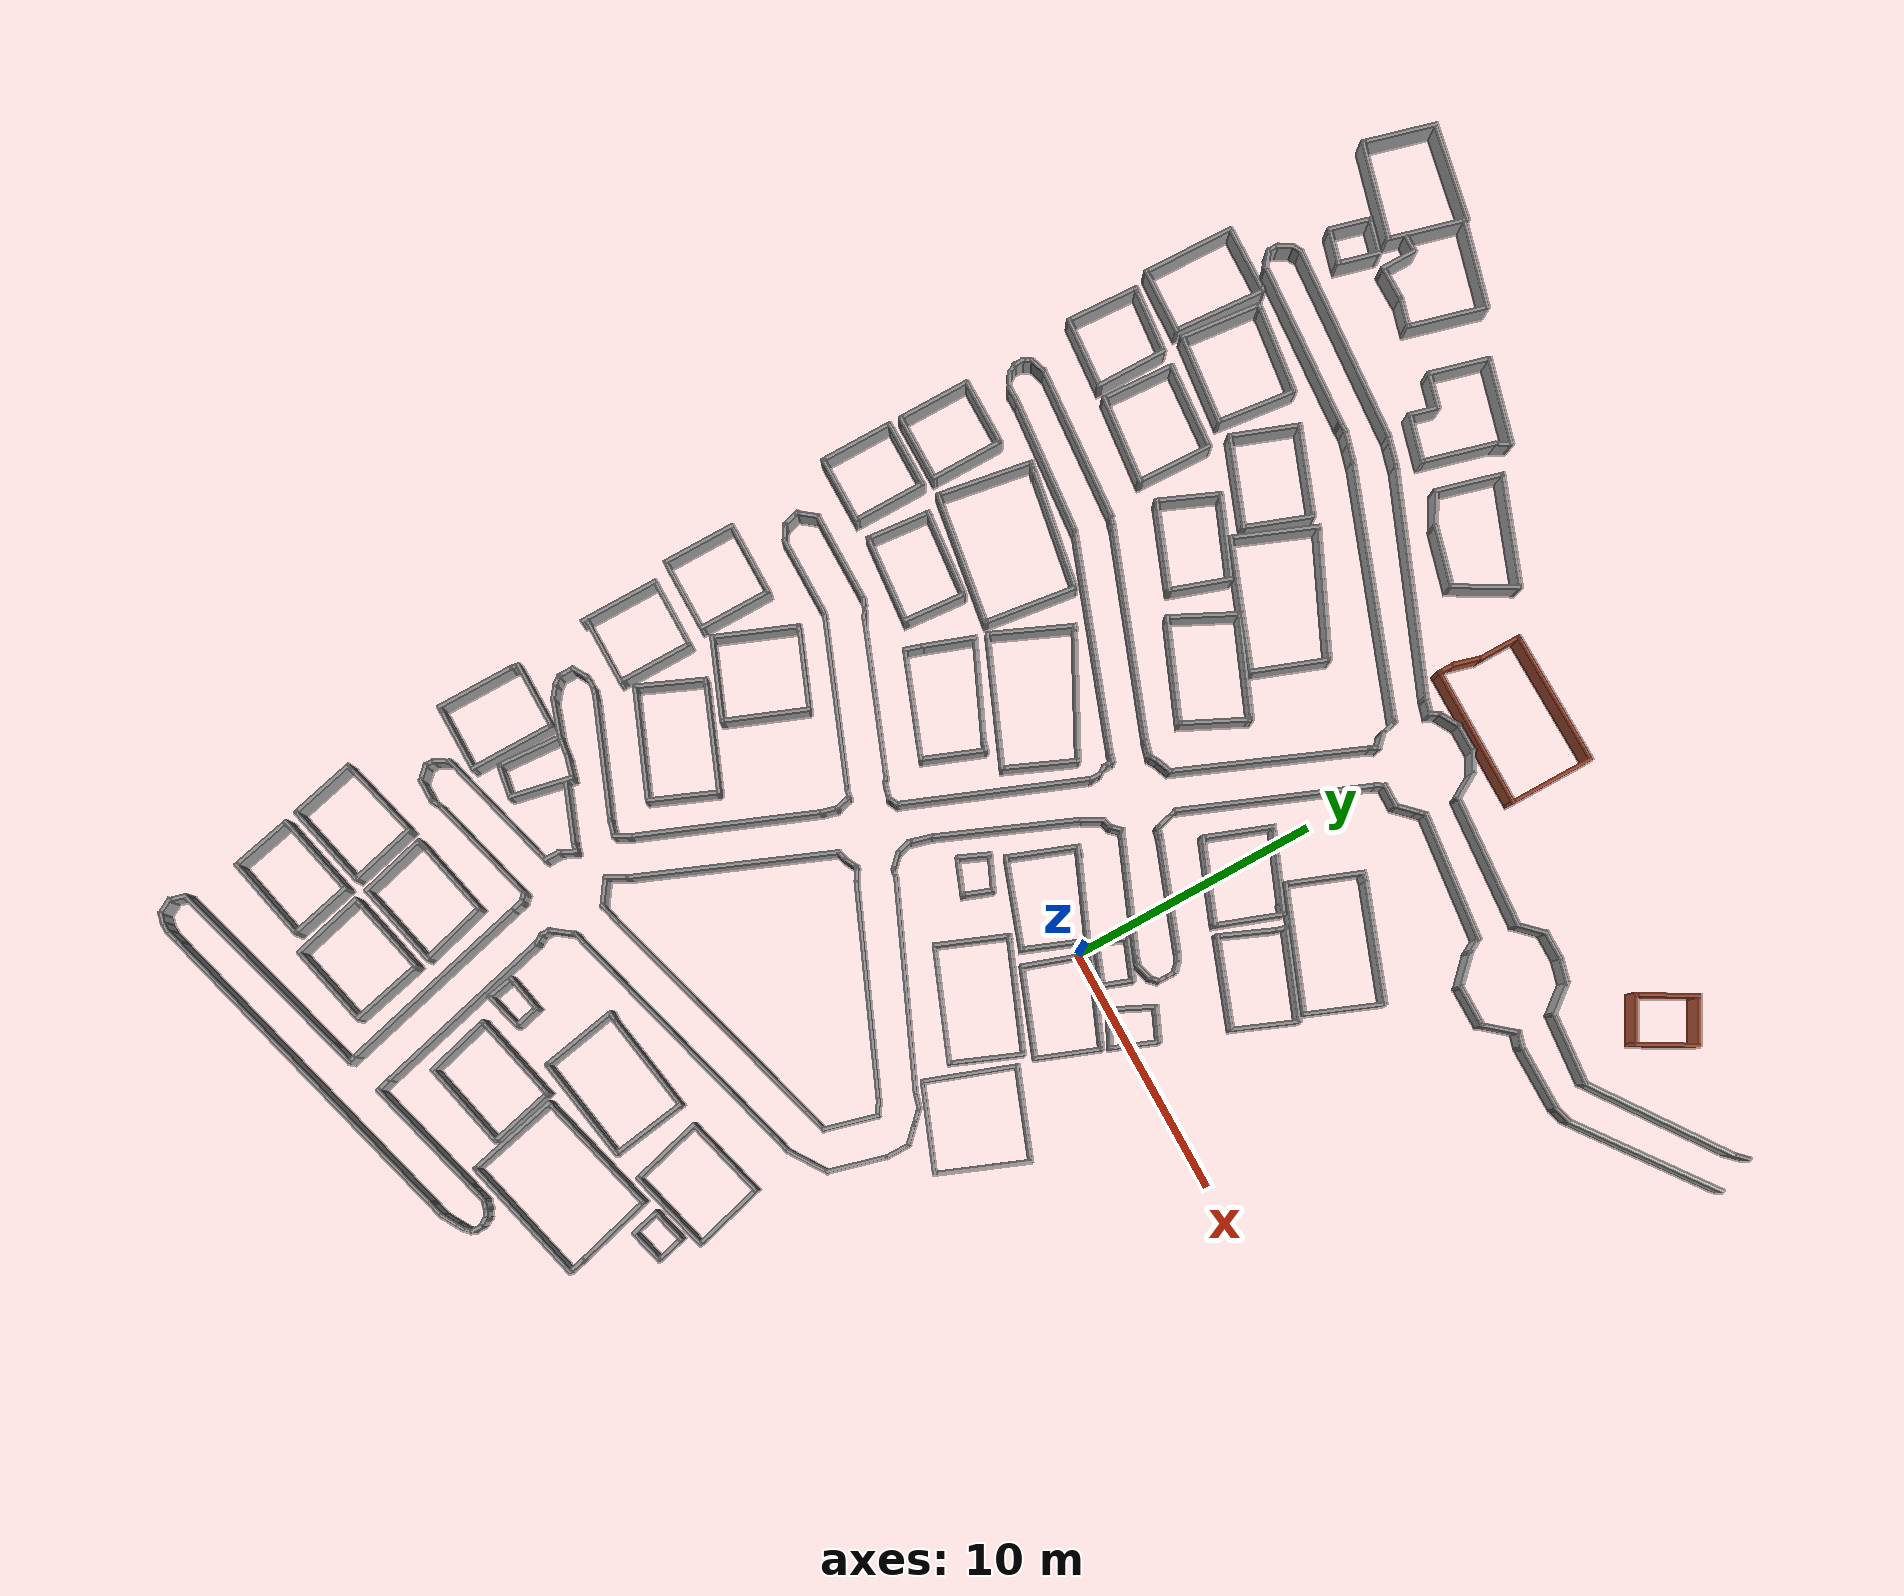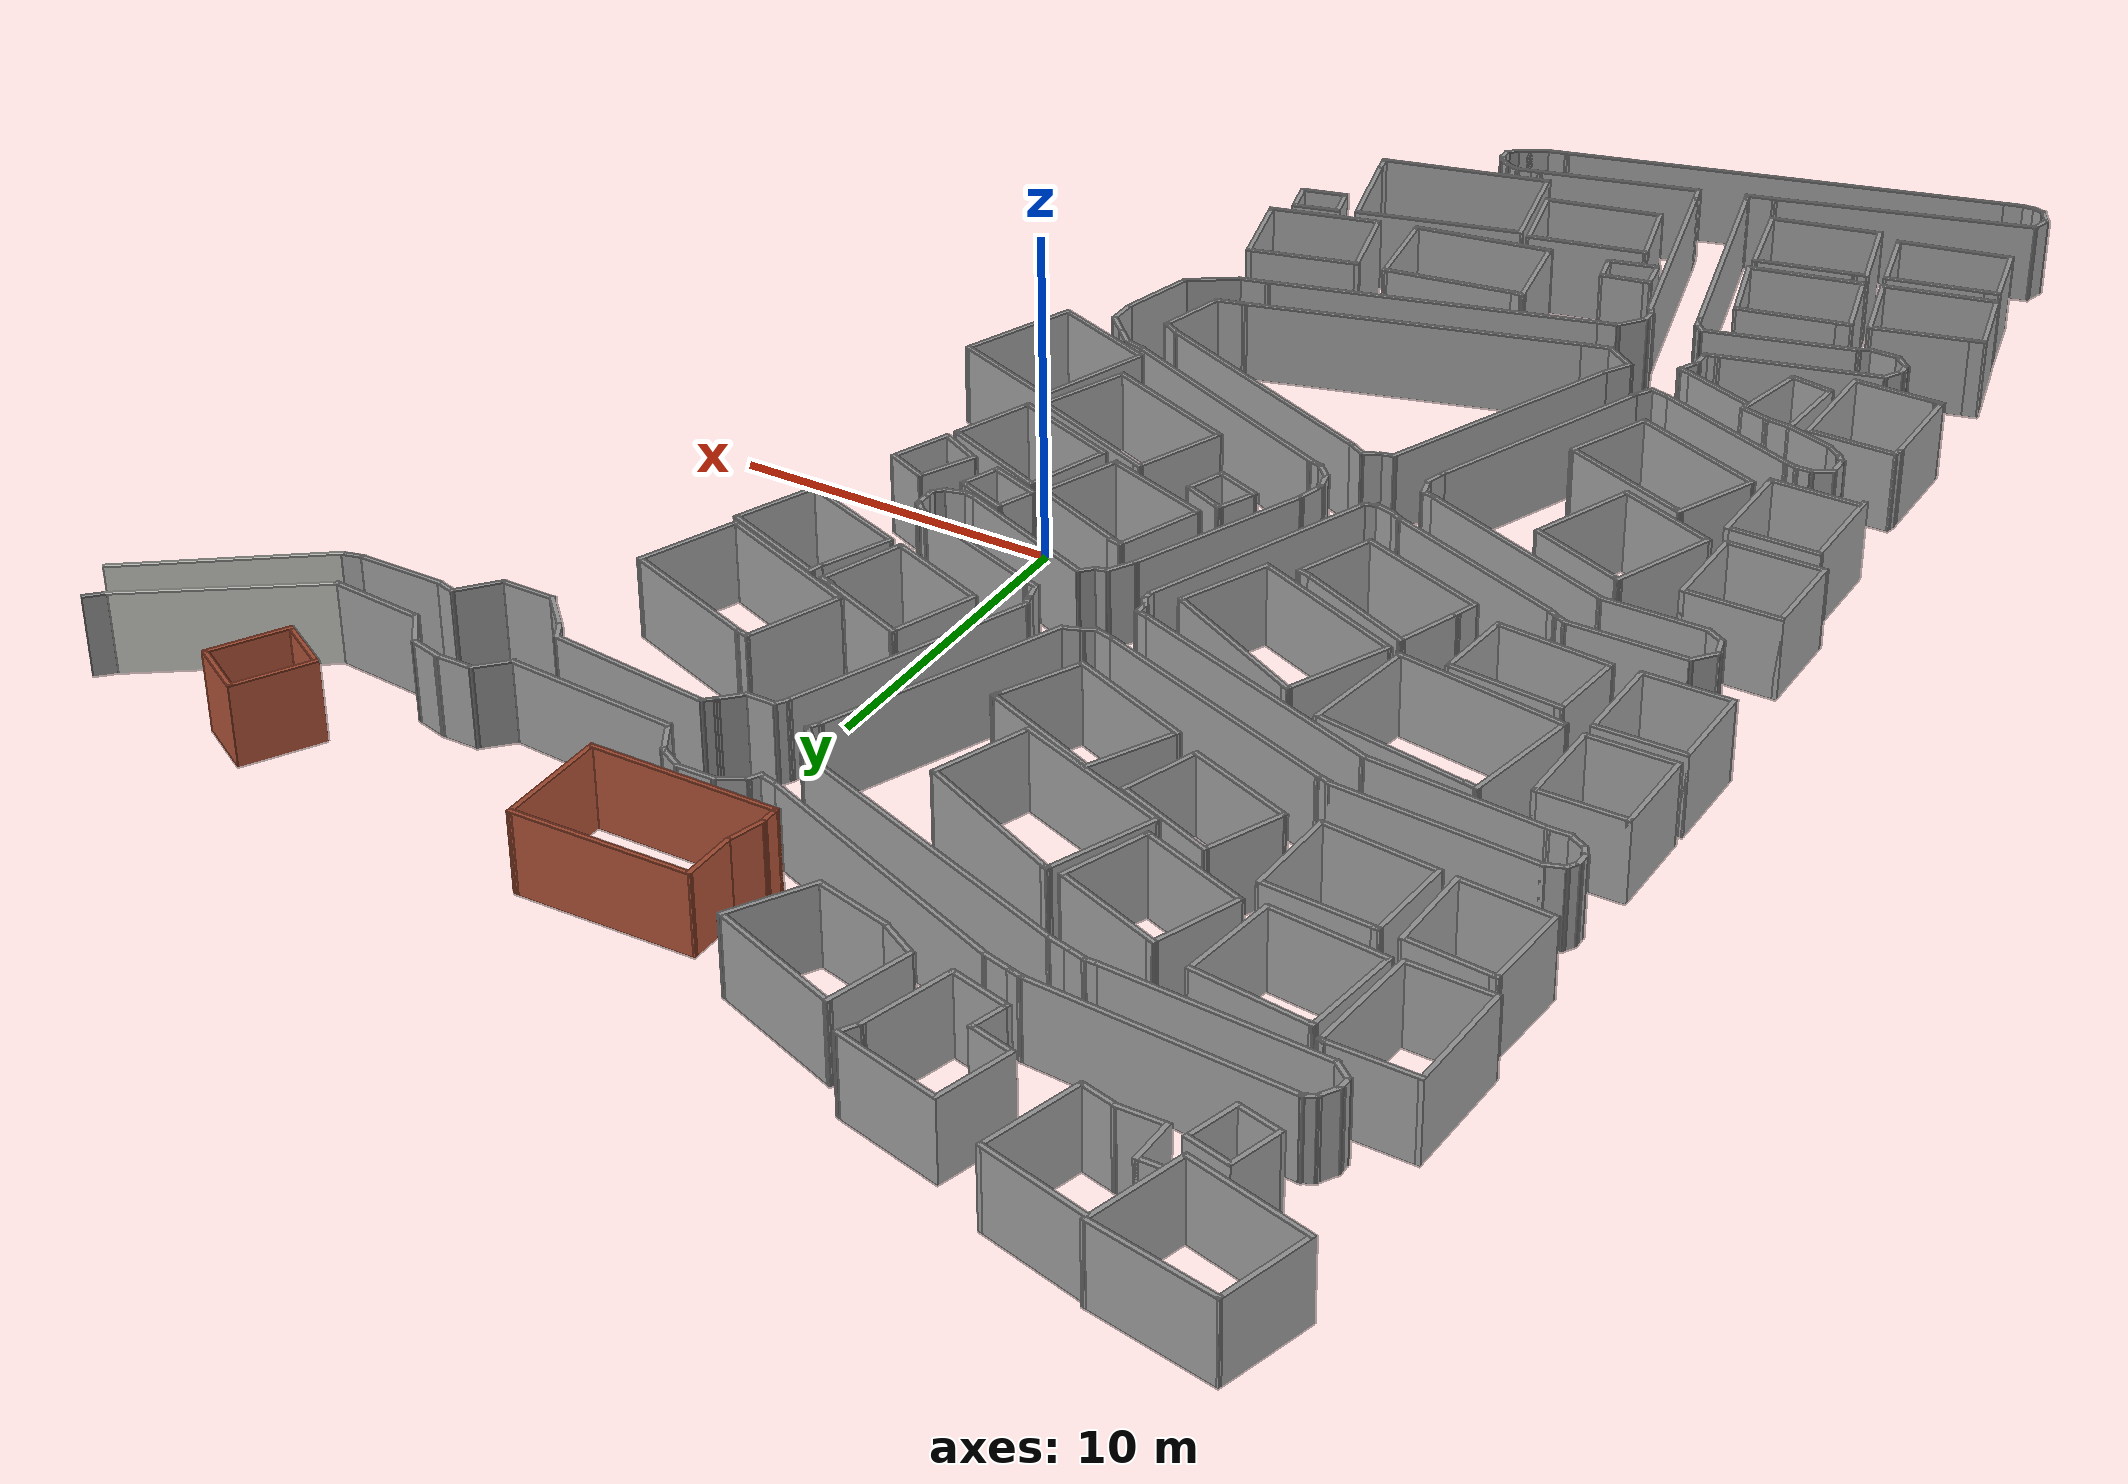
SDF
<?xml version='1.0'?>
<sdf version='1.6'>
  <model name='palazzo'>
    <pose frame=''>-1.20783 -1.18535 0 0 -0 0</pose>
    <link name='Wall_0'>
      <collision name='Wall_0_Collision'>
        <geometry>
          <box>
            <size>2.5 0.15 2.5</size>
          </box>
        </geometry>
        <pose frame=''>0 0 1.25 0 -0 0</pose>
      </collision>
      <visual name='Wall_0_Visual'>
        <pose frame=''>0 0 1.25 0 -0 0</pose>
        <geometry>
          <box>
            <size>2.5 0.15 2.5</size>
          </box>
        </geometry>
        <material>
          <script>
            <uri>file://media/materials/scripts/gazebo.material</uri>
            <name>Gazebo/Bricks</name>
          </script>
          <ambient>1 1 1 1</ambient>
        </material>
        <meta>
          <layer>0</layer>
        </meta>
      </visual>
      <pose frame=''>13.2282 19.6167 0 0 -0 -2.0944</pose>
    </link>
    <link name='Wall_1'>
      <collision name='Wall_1_Collision'>
        <geometry>
          <box>
            <size>2 0.15 2.5</size>
          </box>
        </geometry>
        <pose frame=''>0 0 1.25 0 -0 0</pose>
      </collision>
      <visual name='Wall_1_Visual'>
        <pose frame=''>0 0 1.25 0 -0 0</pose>
        <geometry>
          <box>
            <size>2 0.15 2.5</size>
          </box>
        </geometry>
        <material>
          <script>
            <uri>file://media/materials/scripts/gazebo.material</uri>
            <name>Gazebo/Bricks</name>
          </script>
          <ambient>1 1 1 1</ambient>
        </material>
        <meta>
          <layer>0</layer>
        </meta>
      </visual>
      <pose frame=''>13.4418 18.1366 0 0 -0 -0.523599</pose>
    </link>
    <link name='Wall_100'>
      <collision name='Wall_100_Collision'>
        <geometry>
          <box>
            <size>1.53211 0.15 2.5</size>
          </box>
        </geometry>
        <pose frame=''>0 0 1.25 0 -0 0</pose>
      </collision>
      <visual name='Wall_100_Visual'>
        <pose frame=''>0 0 1.25 0 -0 0</pose>
        <geometry>
          <box>
            <size>1.53211 0.15 2.5</size>
          </box>
        </geometry>
        <material>
          <script>
            <uri>file://media/materials/scripts/gazebo.material</uri>
            <name>Gazebo/Grey</name>
          </script>
          <ambient>1 1 1 1</ambient>
        </material>
        <meta>
          <layer>0</layer>
        </meta>
      </visual>
      <pose frame=''>11.2943 13.5379 0 0 -0 -2.26873</pose>
    </link>
    <link name='Wall_1000'>
      <collision name='Wall_1000_Collision'>
        <geometry>
          <box>
            <size>5.30339 0.15 2.5</size>
          </box>
        </geometry>
        <pose frame=''>0 0 1.25 0 -0 0</pose>
      </collision>
      <visual name='Wall_1000_Visual'>
        <pose frame=''>0 0 1.25 0 -0 0</pose>
        <geometry>
          <box>
            <size>5.30339 0.15 2.5</size>
          </box>
        </geometry>
        <material>
          <script>
            <uri>file://media/materials/scripts/gazebo.material</uri>
            <name>Gazebo/Grey</name>
          </script>
          <ambient>1 1 1 1</ambient>
        </material>
        <meta>
          <layer>0</layer>
        </meta>
      </visual>
      <pose frame=''>-13.9241 4.48746 0 0 -0 2.98879</pose>
    </link>
    <link name='Wall_1002'>
      <collision name='Wall_1002_Collision'>
        <geometry>
          <box>
            <size>5.19311 0.15 2.5</size>
          </box>
        </geometry>
        <pose frame=''>0 0 1.25 0 -0 0</pose>
      </collision>
      <visual name='Wall_1002_Visual'>
        <pose frame=''>0 0 1.25 0 -0 0</pose>
        <geometry>
          <box>
            <size>5.19311 0.15 2.5</size>
          </box>
        </geometry>
        <material>
          <script>
            <uri>file://media/materials/scripts/gazebo.material</uri>
            <name>Gazebo/Grey</name>
          </script>
          <ambient>1 1 1 1</ambient>
        </material>
        <meta>
          <layer>0</layer>
        </meta>
      </visual>
      <pose frame=''>-13.3698 8.12706 0 0 -0 2.9686</pose>
    </link>
    <link name='Wall_1004'>
      <collision name='Wall_1004_Collision'>
        <geometry>
          <box>
            <size>3.78119 0.15 2.5</size>
          </box>
        </geometry>
        <pose frame=''>0 0 1.25 0 -0 0</pose>
      </collision>
      <visual name='Wall_1004_Visual'>
        <pose frame=''>0 0 1.25 0 -0 0</pose>
        <geometry>
          <box>
            <size>3.78119 0.15 2.5</size>
          </box>
        </geometry>
        <material>
          <script>
            <uri>file://media/materials/scripts/gazebo.material</uri>
            <name>Gazebo/Grey</name>
          </script>
          <ambient>1 1 1 1</ambient>
        </material>
        <meta>
          <layer>0</layer>
        </meta>
      </visual>
      <pose frame=''>-11.1316 5.89414 0 0 -0 1.43501</pose>
    </link>
    <link name='Wall_1006'>
      <collision name='Wall_1006_Collision'>
        <geometry>
          <box>
            <size>0.25 0.15 2.5</size>
          </box>
        </geometry>
        <pose frame=''>0 0 1.25 0 -0 0</pose>
      </collision>
      <visual name='Wall_1006_Visual'>
        <pose frame=''>0 0 1.25 0 -0 0</pose>
        <geometry>
          <box>
            <size>0.25 0.15 2.5</size>
          </box>
        </geometry>
        <material>
          <script>
            <uri>file://media/materials/scripts/gazebo.material</uri>
            <name>Gazebo/Grey</name>
          </script>
          <ambient>1 1 1 1</ambient>
        </material>
        <meta>
          <layer>0</layer>
        </meta>
      </visual>
      <pose frame=''>-14.5991 -2.15833 0 0 -0 -0.523599</pose>
    </link>
    <link name='Wall_1008'>
      <collision name='Wall_1008_Collision'>
        <geometry>
          <box>
            <size>3.32198 0.15 2.5</size>
          </box>
        </geometry>
        <pose frame=''>0 0 1.25 0 -0 0</pose>
      </collision>
      <visual name='Wall_1008_Visual'>
        <pose frame=''>0 0 1.25 0 -0 0</pose>
        <geometry>
          <box>
            <size>3.32198 0.15 2.5</size>
          </box>
        </geometry>
        <material>
          <script>
            <uri>file://media/materials/scripts/gazebo.material</uri>
            <name>Gazebo/Grey</name>
          </script>
          <ambient>1 1 1 1</ambient>
        </material>
        <meta>
          <layer>0</layer>
        </meta>
      </visual>
      <pose frame=''>-13.1698 -2.72224 0 0 -0 2.76116</pose>
    </link>
    <link name='Wall_1010'>
      <collision name='Wall_1010_Collision'>
        <geometry>
          <box>
            <size>3.45247 0.15 2.5</size>
          </box>
        </geometry>
        <pose frame=''>0 0 1.25 0 -0 0</pose>
      </collision>
      <visual name='Wall_1010_Visual'>
        <pose frame=''>0 0 1.25 0 -0 0</pose>
        <geometry>
          <box>
            <size>3.45247 0.15 2.5</size>
          </box>
        </geometry>
        <material>
          <script>
            <uri>file://media/materials/scripts/gazebo.material</uri>
            <name>Gazebo/Grey</name>
          </script>
          <ambient>1 1 1 1</ambient>
        </material>
        <meta>
          <layer>0</layer>
        </meta>
      </visual>
      <pose frame=''>-15.2536 -3.66727 0 0 -0 1.19162</pose>
    </link>
    <link name='Wall_1012'>
      <collision name='Wall_1012_Collision'>
        <geometry>
          <box>
            <size>3.45281 0.15 2.5</size>
          </box>
        </geometry>
        <pose frame=''>0 0 1.25 0 -0 0</pose>
      </collision>
      <visual name='Wall_1012_Visual'>
        <pose frame=''>0 0 1.25 0 -0 0</pose>
        <geometry>
          <box>
            <size>3.45281 0.15 2.5</size>
          </box>
        </geometry>
        <material>
          <script>
            <uri>file://media/materials/scripts/gazebo.material</uri>
            <name>Gazebo/Grey</name>
          </script>
          <ambient>1 1 1 1</ambient>
        </material>
        <meta>
          <layer>0</layer>
        </meta>
      </visual>
      <pose frame=''>-12.2982 -4.8493 0 0 -0 1.19829</pose>
    </link>
    <link name='Wall_1014'>
      <collision name='Wall_1014_Collision'>
        <geometry>
          <box>
            <size>3.34403 0.15 2.5</size>
          </box>
        </geometry>
        <pose frame=''>0 0 1.25 0 -0 0</pose>
      </collision>
      <visual name='Wall_1014_Visual'>
        <pose frame=''>0 0 1.25 0 -0 0</pose>
        <geometry>
          <box>
            <size>3.34403 0.15 2.5</size>
          </box>
        </geometry>
        <material>
          <script>
            <uri>file://media/materials/scripts/gazebo.material</uri>
            <name>Gazebo/Grey</name>
          </script>
          <ambient>1 1 1 1</ambient>
        </material>
        <meta>
          <layer>0</layer>
        </meta>
      </visual>
      <pose frame=''>-14.3821 -5.79433 0 0 -0 -0.380506</pose>
    </link>
    <link name='Wall_1016'>
      <collision name='Wall_1016_Collision'>
        <geometry>
          <box>
            <size>0.25 0.15 2.5</size>
          </box>
        </geometry>
        <pose frame=''>0 0 1.25 0 -0 0</pose>
      </collision>
      <visual name='Wall_1016_Visual'>
        <pose frame=''>0 0 1.25 0 -0 0</pose>
        <geometry>
          <box>
            <size>0.25 0.15 2.5</size>
          </box>
        </geometry>
        <material>
          <script>
            <uri>file://media/materials/scripts/gazebo.material</uri>
            <name>Gazebo/Grey</name>
          </script>
          <ambient>1 1 1 1</ambient>
        </material>
        <meta>
          <layer>0</layer>
        </meta>
      </visual>
      <pose frame=''>-14.5246 -6.20683 0 0 -0 -0.523599</pose>
    </link>
    <link name='Wall_1018'>
      <collision name='Wall_1018_Collision'>
        <geometry>
          <box>
            <size>4.43661 0.15 2.5</size>
          </box>
        </geometry>
        <pose frame=''>0 0 1.25 0 -0 0</pose>
      </collision>
      <visual name='Wall_1018_Visual'>
        <pose frame=''>0 0 1.25 0 -0 0</pose>
        <geometry>
          <box>
            <size>4.43661 0.15 2.5</size>
          </box>
        </geometry>
        <material>
          <script>
            <uri>file://media/materials/scripts/gazebo.material</uri>
            <name>Gazebo/Grey</name>
          </script>
          <ambient>1 1 1 1</ambient>
        </material>
        <meta>
          <layer>0</layer>
        </meta>
      </visual>
      <pose frame=''>-12.579 -6.98056 0 0 -0 2.75972</pose>
    </link>
    <link name='Wall_102'>
      <collision name='Wall_102_Collision'>
        <geometry>
          <box>
            <size>1.75 0.15 2.5</size>
          </box>
        </geometry>
        <pose frame=''>0 0 1.25 0 -0 0</pose>
      </collision>
      <visual name='Wall_102_Visual'>
        <pose frame=''>0 0 1.25 0 -0 0</pose>
        <geometry>
          <box>
            <size>1.75 0.15 2.5</size>
          </box>
        </geometry>
        <material>
          <script>
            <uri>file://media/materials/scripts/gazebo.material</uri>
            <name>Gazebo/Grey</name>
          </script>
          <ambient>1 1 1 1</ambient>
        </material>
        <meta>
          <layer>0</layer>
        </meta>
      </visual>
      <pose frame=''>10.0502 13.0084 0 0 -0 3.14159</pose>
    </link>
    <link name='Wall_1020'>
      <collision name='Wall_1020_Collision'>
        <geometry>
          <box>
            <size>2.84489 0.15 2.5</size>
          </box>
        </geometry>
        <pose frame=''>0 0 1.25 0 -0 0</pose>
      </collision>
      <visual name='Wall_1020_Visual'>
        <pose frame=''>0 0 1.25 0 -0 0</pose>
        <geometry>
          <box>
            <size>2.84489 0.15 2.5</size>
          </box>
        </geometry>
        <material>
          <script>
            <uri>file://media/materials/scripts/gazebo.material</uri>
            <name>Gazebo/Grey</name>
          </script>
          <ambient>1 1 1 1</ambient>
        </material>
        <meta>
          <layer>0</layer>
        </meta>
      </visual>
      <pose frame=''>-11.1041 -9.02484 0 0 -0 1.17939</pose>
    </link>
    <link name='Wall_1022'>
      <collision name='Wall_1022_Collision'>
        <geometry>
          <box>
            <size>2.82804 0.15 2.5</size>
          </box>
        </geometry>
        <pose frame=''>0 0 1.25 0 -0 0</pose>
      </collision>
      <visual name='Wall_1022_Visual'>
        <pose frame=''>0 0 1.25 0 -0 0</pose>
        <geometry>
          <box>
            <size>2.82804 0.15 2.5</size>
          </box>
        </geometry>
        <material>
          <script>
            <uri>file://media/materials/scripts/gazebo.material</uri>
            <name>Gazebo/Grey</name>
          </script>
          <ambient>1 1 1 1</ambient>
        </material>
        <meta>
          <layer>0</layer>
        </meta>
      </visual>
      <pose frame=''>-15.0977 -7.41156 0 0 -0 1.16397</pose>
    </link>
    <link name='Wall_1024'>
      <collision name='Wall_1024_Collision'>
        <geometry>
          <box>
            <size>4.47779 0.15 2.5</size>
          </box>
        </geometry>
        <pose frame=''>0 0 1.25 0 -0 0</pose>
      </collision>
      <visual name='Wall_1024_Visual'>
        <pose frame=''>0 0 1.25 0 -0 0</pose>
        <geometry>
          <box>
            <size>4.47779 0.15 2.5</size>
          </box>
        </geometry>
        <material>
          <script>
            <uri>file://media/materials/scripts/gazebo.material</uri>
            <name>Gazebo/Grey</name>
          </script>
          <ambient>1 1 1 1</ambient>
        </material>
        <meta>
          <layer>0</layer>
        </meta>
      </visual>
      <pose frame=''>-13.6229 -9.45584 0 0 -0 -0.385936</pose>
    </link>
    <link name='Wall_1026'>
      <collision name='Wall_1026_Collision'>
        <geometry>
          <box>
            <size>2.75 0.15 2.5</size>
          </box>
        </geometry>
        <pose frame=''>0 0 1.25 0 -0 0</pose>
      </collision>
      <visual name='Wall_1026_Visual'>
        <pose frame=''>0 0 1.25 0 -0 0</pose>
        <geometry>
          <box>
            <size>2.75 0.15 2.5</size>
          </box>
        </geometry>
        <material>
          <script>
            <uri>file://media/materials/scripts/gazebo.material</uri>
            <name>Gazebo/Grey</name>
          </script>
          <ambient>1 1 1 1</ambient>
        </material>
        <meta>
          <layer>0</layer>
        </meta>
      </visual>
      <pose frame=''>-17.4434 -6.07112 0 0 -0 0</pose>
    </link>
    <link name='Wall_1027'>
      <collision name='Wall_1027_Collision'>
        <geometry>
          <box>
            <size>0.25 0.15 2.5</size>
          </box>
        </geometry>
        <pose frame=''>0 0 1.25 0 -0 0</pose>
      </collision>
      <visual name='Wall_1027_Visual'>
        <pose frame=''>0 0 1.25 0 -0 0</pose>
        <geometry>
          <box>
            <size>0.25 0.15 2.5</size>
          </box>
        </geometry>
        <material>
          <script>
            <uri>file://media/materials/scripts/gazebo.material</uri>
            <name>Gazebo/Grey</name>
          </script>
          <ambient>1 1 1 1</ambient>
        </material>
        <meta>
          <layer>0</layer>
        </meta>
      </visual>
      <pose frame=''>-16.0934 -6.07112 0 0 -0 0</pose>
    </link>
    <link name='Wall_1028'>
      <collision name='Wall_1028_Collision'>
        <geometry>
          <box>
            <size>3 0.15 2.5</size>
          </box>
        </geometry>
        <pose frame=''>0 0 1.25 0 -0 0</pose>
      </collision>
      <visual name='Wall_1028_Visual'>
        <pose frame=''>0 0 1.25 0 -0 0</pose>
        <geometry>
          <box>
            <size>3 0.15 2.5</size>
          </box>
        </geometry>
        <material>
          <script>
            <uri>file://media/materials/scripts/gazebo.material</uri>
            <name>Gazebo/Grey</name>
          </script>
          <ambient>1 1 1 1</ambient>
        </material>
        <meta>
          <layer>0</layer>
        </meta>
      </visual>
      <pose frame=''>-16.0434 -7.49612 0 0 -0 -1.5708</pose>
    </link>
    <link name='Wall_1029'>
      <collision name='Wall_1029_Collision'>
        <geometry>
          <box>
            <size>0.25 0.15 2.5</size>
          </box>
        </geometry>
        <pose frame=''>0 0 1.25 0 -0 0</pose>
      </collision>
      <visual name='Wall_1029_Visual'>
        <pose frame=''>0 0 1.25 0 -0 0</pose>
        <geometry>
          <box>
            <size>0.25 0.15 2.5</size>
          </box>
        </geometry>
        <material>
          <script>
            <uri>file://media/materials/scripts/gazebo.material</uri>
            <name>Gazebo/Grey</name>
          </script>
          <ambient>1 1 1 1</ambient>
        </material>
        <meta>
          <layer>0</layer>
        </meta>
      </visual>
      <pose frame=''>-16.0434 -8.97112 0 0 -0 -1.5708</pose>
    </link>
    <link name='Wall_103'>
      <collision name='Wall_103_Collision'>
        <geometry>
          <box>
            <size>1.5 0.15 2.5</size>
          </box>
        </geometry>
        <pose frame=''>0 0 1.25 0 -0 0</pose>
      </collision>
      <visual name='Wall_103_Visual'>
        <pose frame=''>0 0 1.25 0 -0 0</pose>
        <geometry>
          <box>
            <size>1.5 0.15 2.5</size>
          </box>
        </geometry>
        <material>
          <script>
            <uri>file://media/materials/scripts/gazebo.material</uri>
            <name>Gazebo/Grey</name>
          </script>
          <ambient>1 1 1 1</ambient>
        </material>
        <meta>
          <layer>0</layer>
        </meta>
      </visual>
      <pose frame=''>8.77286 13.4857 0 0 -0 2.35619</pose>
    </link>
    <link name='Wall_1030'>
      <collision name='Wall_1030_Collision'>
        <geometry>
          <box>
            <size>2.75 0.15 2.5</size>
          </box>
        </geometry>
        <pose frame=''>0 0 1.25 0 -0 0</pose>
      </collision>
      <visual name='Wall_1030_Visual'>
        <pose frame=''>0 0 1.25 0 -0 0</pose>
        <geometry>
          <box>
            <size>2.75 0.15 2.5</size>
          </box>
        </geometry>
        <material>
          <script>
            <uri>file://media/materials/scripts/gazebo.material</uri>
            <name>Gazebo/Grey</name>
          </script>
          <ambient>1 1 1 1</ambient>
        </material>
        <meta>
          <layer>0</layer>
        </meta>
      </visual>
      <pose frame=''>-17.3434 -9.02112 0 0 -0 3.14159</pose>
    </link>
    <link name='Wall_1032'>
      <collision name='Wall_1032_Collision'>
        <geometry>
          <box>
            <size>3.25 0.15 2.5</size>
          </box>
        </geometry>
        <pose frame=''>0 0 1.25 0 -0 0</pose>
      </collision>
      <visual name='Wall_1032_Visual'>
        <pose frame=''>0 0 1.25 0 -0 0</pose>
        <geometry>
          <box>
            <size>3.25 0.15 2.5</size>
          </box>
        </geometry>
        <material>
          <script>
            <uri>file://media/materials/scripts/gazebo.material</uri>
            <name>Gazebo/Grey</name>
          </script>
          <ambient>1 1 1 1</ambient>
        </material>
        <meta>
          <layer>0</layer>
        </meta>
      </visual>
      <pose frame=''>-18.7434 -7.62112 0 0 -0 -1.5708</pose>
    </link>
    <link name='Wall_1034'>
      <collision name='Wall_1034_Collision'>
        <geometry>
          <box>
            <size>3 0.15 2.5</size>
          </box>
        </geometry>
        <pose frame=''>0 0 1.25 0 -0 0</pose>
      </collision>
      <visual name='Wall_1034_Visual'>
        <pose frame=''>0 0 1.25 0 -0 0</pose>
        <geometry>
          <box>
            <size>3 0.15 2.5</size>
          </box>
        </geometry>
        <material>
          <script>
            <uri>file://media/materials/scripts/gazebo.material</uri>
            <name>Gazebo/Grey</name>
          </script>
          <ambient>1 1 1 1</ambient>
        </material>
        <meta>
          <layer>0</layer>
        </meta>
      </visual>
      <pose frame=''>-17.7777 -2.51436 0 0 -0 0</pose>
    </link>
    <link name='Wall_1035'>
      <collision name='Wall_1035_Collision'>
        <geometry>
          <box>
            <size>3 0.15 2.5</size>
          </box>
        </geometry>
        <pose frame=''>0 0 1.25 0 -0 0</pose>
      </collision>
      <visual name='Wall_1035_Visual'>
        <pose frame=''>0 0 1.25 0 -0 0</pose>
        <geometry>
          <box>
            <size>3 0.15 2.5</size>
          </box>
        </geometry>
        <material>
          <script>
            <uri>file://media/materials/scripts/gazebo.material</uri>
            <name>Gazebo/Grey</name>
          </script>
          <ambient>1 1 1 1</ambient>
        </material>
        <meta>
          <layer>0</layer>
        </meta>
      </visual>
      <pose frame=''>-16.3527 -3.93936 0 0 -0 -1.5708</pose>
    </link>
    <link name='Wall_1036'>
      <collision name='Wall_1036_Collision'>
        <geometry>
          <box>
            <size>3 0.15 2.5</size>
          </box>
        </geometry>
        <pose frame=''>0 0 1.25 0 -0 0</pose>
      </collision>
      <visual name='Wall_1036_Visual'>
        <pose frame=''>0 0 1.25 0 -0 0</pose>
        <geometry>
          <box>
            <size>3 0.15 2.5</size>
          </box>
        </geometry>
        <material>
          <script>
            <uri>file://media/materials/scripts/gazebo.material</uri>
            <name>Gazebo/Grey</name>
          </script>
          <ambient>1 1 1 1</ambient>
        </material>
        <meta>
          <layer>0</layer>
        </meta>
      </visual>
      <pose frame=''>-17.7777 -5.36436 0 0 -0 3.14159</pose>
    </link>
    <link name='Wall_1037'>
      <collision name='Wall_1037_Collision'>
        <geometry>
          <box>
            <size>3 0.15 2.5</size>
          </box>
        </geometry>
        <pose frame=''>0 0 1.25 0 -0 0</pose>
      </collision>
      <visual name='Wall_1037_Visual'>
        <pose frame=''>0 0 1.25 0 -0 0</pose>
        <geometry>
          <box>
            <size>3 0.15 2.5</size>
          </box>
        </geometry>
        <material>
          <script>
            <uri>file://media/materials/scripts/gazebo.material</uri>
            <name>Gazebo/Grey</name>
          </script>
          <ambient>1 1 1 1</ambient>
        </material>
        <meta>
          <layer>0</layer>
        </meta>
      </visual>
      <pose frame=''>-19.2027 -3.93936 0 0 -0 1.5708</pose>
    </link>
    <link name='Wall_1039'>
      <collision name='Wall_1039_Collision'>
        <geometry>
          <box>
            <size>2.75 0.15 2.5</size>
          </box>
        </geometry>
        <pose frame=''>0 0 1.25 0 -0 0</pose>
      </collision>
      <visual name='Wall_1039_Visual'>
        <pose frame=''>0 0 1.25 0 -0 0</pose>
        <geometry>
          <box>
            <size>2.75 0.15 2.5</size>
          </box>
        </geometry>
        <material>
          <script>
            <uri>file://media/materials/scripts/gazebo.material</uri>
            <name>Gazebo/Grey</name>
          </script>
          <ambient>1 1 1 1</ambient>
        </material>
        <meta>
          <layer>0</layer>
        </meta>
      </visual>
      <pose frame=''>-17.1394 -12.097 0 0 -0 0</pose>
    </link>
    <link name='Wall_104'>
      <collision name='Wall_104_Collision'>
        <geometry>
          <box>
            <size>0.75 0.15 2.5</size>
          </box>
        </geometry>
        <pose frame=''>0 0 1.25 0 -0 0</pose>
      </collision>
      <visual name='Wall_104_Visual'>
        <pose frame=''>0 0 1.25 0 -0 0</pose>
        <geometry>
          <box>
            <size>0.75 0.15 2.5</size>
          </box>
        </geometry>
        <material>
          <script>
            <uri>file://media/materials/scripts/gazebo.material</uri>
            <name>Gazebo/Grey</name>
          </script>
          <ambient>1 1 1 1</ambient>
        </material>
        <meta>
          <layer>0</layer>
        </meta>
      </visual>
      <pose frame=''>8.14556 14.2228 0 0 -0 2.0944</pose>
    </link>
    <link name='Wall_1040'>
      <collision name='Wall_1040_Collision'>
        <geometry>
          <box>
            <size>3.5 0.15 2.5</size>
          </box>
        </geometry>
        <pose frame=''>0 0 1.25 0 -0 0</pose>
      </collision>
      <visual name='Wall_1040_Visual'>
        <pose frame=''>0 0 1.25 0 -0 0</pose>
        <geometry>
          <box>
            <size>3.5 0.15 2.5</size>
          </box>
        </geometry>
        <material>
          <script>
            <uri>file://media/materials/scripts/gazebo.material</uri>
            <name>Gazebo/Grey</name>
          </script>
          <ambient>1 1 1 1</ambient>
        </material>
        <meta>
          <layer>0</layer>
        </meta>
      </visual>
      <pose frame=''>-15.8394 -13.772 0 0 -0 -1.5708</pose>
    </link>
    <link name='Wall_1041'>
      <collision name='Wall_1041_Collision'>
        <geometry>
          <box>
            <size>2.5 0.15 2.5</size>
          </box>
        </geometry>
        <pose frame=''>0 0 1.25 0 -0 0</pose>
      </collision>
      <visual name='Wall_1041_Visual'>
        <pose frame=''>0 0 1.25 0 -0 0</pose>
        <geometry>
          <box>
            <size>2.5 0.15 2.5</size>
          </box>
        </geometry>
        <material>
          <script>
            <uri>file://media/materials/scripts/gazebo.material</uri>
            <name>Gazebo/Grey</name>
          </script>
          <ambient>1 1 1 1</ambient>
        </material>
        <meta>
          <layer>0</layer>
        </meta>
      </visual>
      <pose frame=''>-17.0144 -15.447 0 0 -0 3.14159</pose>
    </link>
    <link name='Wall_1042'>
      <collision name='Wall_1042_Collision'>
        <geometry>
          <box>
            <size>0.25 0.15 2.5</size>
          </box>
        </geometry>
        <pose frame=''>0 0 1.25 0 -0 0</pose>
      </collision>
      <visual name='Wall_1042_Visual'>
        <pose frame=''>0 0 1.25 0 -0 0</pose>
        <geometry>
          <box>
            <size>0.25 0.15 2.5</size>
          </box>
        </geometry>
        <material>
          <script>
            <uri>file://media/materials/scripts/gazebo.material</uri>
            <name>Gazebo/Grey</name>
          </script>
          <ambient>1 1 1 1</ambient>
        </material>
        <meta>
          <layer>0</layer>
        </meta>
      </visual>
      <pose frame=''>-18.2394 -15.447 0 0 -0 3.14159</pose>
    </link>
    <link name='Wall_1043'>
      <collision name='Wall_1043_Collision'>
        <geometry>
          <box>
            <size>0.25 0.15 2.5</size>
          </box>
        </geometry>
        <pose frame=''>0 0 1.25 0 -0 0</pose>
      </collision>
      <visual name='Wall_1043_Visual'>
        <pose frame=''>0 0 1.25 0 -0 0</pose>
        <geometry>
          <box>
            <size>0.25 0.15 2.5</size>
          </box>
        </geometry>
        <material>
          <script>
            <uri>file://media/materials/scripts/gazebo.material</uri>
            <name>Gazebo/Grey</name>
          </script>
          <ambient>1 1 1 1</ambient>
        </material>
        <meta>
          <layer>0</layer>
        </meta>
      </visual>
      <pose frame=''>-18.3394 -15.447 0 0 -0 3.14159</pose>
    </link>
    <link name='Wall_1044'>
      <collision name='Wall_1044_Collision'>
        <geometry>
          <box>
            <size>0.25 0.15 2.5</size>
          </box>
        </geometry>
        <pose frame=''>0 0 1.25 0 -0 0</pose>
      </collision>
      <visual name='Wall_1044_Visual'>
        <pose frame=''>0 0 1.25 0 -0 0</pose>
        <geometry>
          <box>
            <size>0.25 0.15 2.5</size>
          </box>
        </geometry>
        <material>
          <script>
            <uri>file://media/materials/scripts/gazebo.material</uri>
            <name>Gazebo/Grey</name>
          </script>
          <ambient>1 1 1 1</ambient>
        </material>
        <meta>
          <layer>0</layer>
        </meta>
      </visual>
      <pose frame=''>-18.4394 -15.447 0 0 -0 3.14159</pose>
    </link>
    <link name='Wall_1045'>
      <collision name='Wall_1045_Collision'>
        <geometry>
          <box>
            <size>3.25 0.15 2.5</size>
          </box>
        </geometry>
        <pose frame=''>0 0 1.25 0 -0 0</pose>
      </collision>
      <visual name='Wall_1045_Visual'>
        <pose frame=''>0 0 1.25 0 -0 0</pose>
        <geometry>
          <box>
            <size>3.25 0.15 2.5</size>
          </box>
        </geometry>
        <material>
          <script>
            <uri>file://media/materials/scripts/gazebo.material</uri>
            <name>Gazebo/Grey</name>
          </script>
          <ambient>1 1 1 1</ambient>
        </material>
        <meta>
          <layer>0</layer>
        </meta>
      </visual>
      <pose frame=''>-18.4894 -13.897 0 0 -0 1.5708</pose>
    </link>
    <link name='Wall_1047'>
      <collision name='Wall_1047_Collision'>
        <geometry>
          <box>
            <size>0.404951 0.15 2.5</size>
          </box>
        </geometry>
        <pose frame=''>0 0 1.25 0 -0 0</pose>
      </collision>
      <visual name='Wall_1047_Visual'>
        <pose frame=''>0 0 1.25 0 -0 0</pose>
        <geometry>
          <box>
            <size>0.404951 0.15 2.5</size>
          </box>
        </geometry>
        <material>
          <script>
            <uri>file://media/materials/scripts/gazebo.material</uri>
            <name>Gazebo/Grey</name>
          </script>
          <ambient>1 1 1 1</ambient>
        </material>
        <meta>
          <layer>0</layer>
        </meta>
      </visual>
      <pose frame=''>-18.4644 -12.222 0 0 -0 -1.76819</pose>
    </link>
    <link name='Wall_1049'>
      <collision name='Wall_1049_Collision'>
        <geometry>
          <box>
            <size>0.5 0.15 2.5</size>
          </box>
        </geometry>
        <pose frame=''>0 0 1.25 0 -0 0</pose>
      </collision>
      <visual name='Wall_1049_Visual'>
        <pose frame=''>0 0 1.25 0 -0 0</pose>
        <geometry>
          <box>
            <size>0.5 0.15 2.5</size>
          </box>
        </geometry>
        <material>
          <script>
            <uri>file://media/materials/scripts/gazebo.material</uri>
            <name>Gazebo/Grey</name>
          </script>
          <ambient>1 1 1 1</ambient>
        </material>
        <meta>
          <layer>0</layer>
        </meta>
      </visual>
      <pose frame=''>-18.0161 -19.4456 0 0 -0 0.261799</pose>
    </link>
    <link name='Wall_1051'>
      <collision name='Wall_1051_Collision'>
        <geometry>
          <box>
            <size>3.48346 0.15 2.5</size>
          </box>
        </geometry>
        <pose frame=''>0 0 1.25 0 -0 0</pose>
      </collision>
      <visual name='Wall_1051_Visual'>
        <pose frame=''>0 0 1.25 0 -0 0</pose>
        <geometry>
          <box>
            <size>3.48346 0.15 2.5</size>
          </box>
        </geometry>
        <material>
          <script>
            <uri>file://media/materials/scripts/gazebo.material</uri>
            <name>Gazebo/Grey</name>
          </script>
          <ambient>1 1 1 1</ambient>
        </material>
        <meta>
          <layer>0</layer>
        </meta>
      </visual>
      <pose frame=''>-16.5745 -19.0621 0 0 -0 -2.88139</pose>
    </link>
    <link name='Wall_1053'>
      <collision name='Wall_1053_Collision'>
        <geometry>
          <box>
            <size>2.76283 0.15 2.5</size>
          </box>
        </geometry>
        <pose frame=''>0 0 1.25 0 -0 0</pose>
      </collision>
      <visual name='Wall_1053_Visual'>
        <pose frame=''>0 0 1.25 0 -0 0</pose>
        <geometry>
          <box>
            <size>2.76283 0.15 2.5</size>
          </box>
        </geometry>
        <material>
          <script>
            <uri>file://media/materials/scripts/gazebo.material</uri>
            <name>Gazebo/Grey</name>
          </script>
          <ambient>1 1 1 1</ambient>
        </material>
        <meta>
          <layer>0</layer>
        </meta>
      </visual>
      <pose frame=''>-17.8818 -20.7616 0 0 -0 1.8051</pose>
    </link>
    <link name='Wall_1055'>
      <collision name='Wall_1055_Collision'>
        <geometry>
          <box>
            <size>2.84897 0.15 2.5</size>
          </box>
        </geometry>
        <pose frame=''>0 0 1.25 0 -0 0</pose>
      </collision>
      <visual name='Wall_1055_Visual'>
        <pose frame=''>0 0 1.25 0 -0 0</pose>
        <geometry>
          <box>
            <size>2.84897 0.15 2.5</size>
          </box>
        </geometry>
        <material>
          <script>
            <uri>file://media/materials/scripts/gazebo.material</uri>
            <name>Gazebo/Grey</name>
          </script>
          <ambient>1 1 1 1</ambient>
        </material>
        <meta>
          <layer>0</layer>
        </meta>
      </visual>
      <pose frame=''>-14.6292 -19.9406 0 0 -0 1.82141</pose>
    </link>
    <link name='Wall_1057'>
      <collision name='Wall_1057_Collision'>
        <geometry>
          <box>
            <size>3.52638 0.15 2.5</size>
          </box>
        </geometry>
        <pose frame=''>0 0 1.25 0 -0 0</pose>
      </collision>
      <visual name='Wall_1057_Visual'>
        <pose frame=''>0 0 1.25 0 -0 0</pose>
        <geometry>
          <box>
            <size>3.52638 0.15 2.5</size>
          </box>
        </geometry>
        <material>
          <script>
            <uri>file://media/materials/scripts/gazebo.material</uri>
            <name>Gazebo/Grey</name>
          </script>
          <ambient>1 1 1 1</ambient>
        </material>
        <meta>
          <layer>0</layer>
        </meta>
      </visual>
      <pose frame=''>-15.9365 -21.6402 0 0 -0 0.234461</pose>
    </link>
    <link name='Wall_1059'>
      <collision name='Wall_1059_Collision'>
        <geometry>
          <box>
            <size>0.5 0.15 2.5</size>
          </box>
        </geometry>
        <pose frame=''>0 0 1.25 0 -0 0</pose>
      </collision>
      <visual name='Wall_1059_Visual'>
        <pose frame=''>0 0 1.25 0 -0 0</pose>
        <geometry>
          <box>
            <size>0.5 0.15 2.5</size>
          </box>
        </geometry>
        <material>
          <script>
            <uri>file://media/materials/scripts/gazebo.material</uri>
            <name>Gazebo/Grey</name>
          </script>
          <ambient>1 1 1 1</ambient>
        </material>
        <meta>
          <layer>0</layer>
        </meta>
      </visual>
      <pose frame=''>-14.2405 -18.4625 0 0 -0 0.261799</pose>
    </link>
    <link name='Wall_1061'>
      <collision name='Wall_1061_Collision'>
        <geometry>
          <box>
            <size>3.54196 0.15 2.5</size>
          </box>
        </geometry>
        <pose frame=''>0 0 1.25 0 -0 0</pose>
      </collision>
      <visual name='Wall_1061_Visual'>
        <pose frame=''>0 0 1.25 0 -0 0</pose>
        <geometry>
          <box>
            <size>3.54196 0.15 2.5</size>
          </box>
        </geometry>
        <material>
          <script>
            <uri>file://media/materials/scripts/gazebo.material</uri>
            <name>Gazebo/Grey</name>
          </script>
          <ambient>1 1 1 1</ambient>
        </material>
        <meta>
          <layer>0</layer>
        </meta>
      </visual>
      <pose frame=''>-12.7571 -18.1261 0 0 -0 -2.91456</pose>
    </link>
    <link name='Wall_1063'>
      <collision name='Wall_1063_Collision'>
        <geometry>
          <box>
            <size>2.83402 0.15 2.5</size>
          </box>
        </geometry>
        <pose frame=''>0 0 1.25 0 -0 0</pose>
      </collision>
      <visual name='Wall_1063_Visual'>
        <pose frame=''>0 0 1.25 0 -0 0</pose>
        <geometry>
          <box>
            <size>2.83402 0.15 2.5</size>
          </box>
        </geometry>
        <material>
          <script>
            <uri>file://media/materials/scripts/gazebo.material</uri>
            <name>Gazebo/Grey</name>
          </script>
          <ambient>1 1 1 1</ambient>
        </material>
        <meta>
          <layer>0</layer>
        </meta>
      </visual>
      <pose frame=''>-14.0644 -19.8047 0 0 -0 1.8309</pose>
    </link>
    <link name='Wall_1065'>
      <collision name='Wall_1065_Collision'>
        <geometry>
          <box>
            <size>2.82495 0.15 2.5</size>
          </box>
        </geometry>
        <pose frame=''>0 0 1.25 0 -0 0</pose>
      </collision>
      <visual name='Wall_1065_Visual'>
        <pose frame=''>0 0 1.25 0 -0 0</pose>
        <geometry>
          <box>
            <size>2.82495 0.15 2.5</size>
          </box>
        </geometry>
        <material>
          <script>
            <uri>file://media/materials/scripts/gazebo.material</uri>
            <name>Gazebo/Grey</name>
          </script>
          <ambient>1 1 1 1</ambient>
        </material>
        <meta>
          <layer>0</layer>
        </meta>
      </visual>
      <pose frame=''>-10.7386 -19.0307 0 0 -0 1.84802</pose>
    </link>
    <link name='Wall_1067'>
      <collision name='Wall_1067_Collision'>
        <geometry>
          <box>
            <size>3.58745 0.15 2.5</size>
          </box>
        </geometry>
        <pose frame=''>0 0 1.25 0 -0 0</pose>
      </collision>
      <visual name='Wall_1067_Visual'>
        <pose frame=''>0 0 1.25 0 -0 0</pose>
        <geometry>
          <box>
            <size>3.58745 0.15 2.5</size>
          </box>
        </geometry>
        <material>
          <script>
            <uri>file://media/materials/scripts/gazebo.material</uri>
            <name>Gazebo/Grey</name>
          </script>
          <ambient>1 1 1 1</ambient>
        </material>
        <meta>
          <layer>0</layer>
        </meta>
      </visual>
      <pose frame=''>-12.0459 -20.7093 0 0 -0 0.23022</pose>
    </link>
    <link name='Wall_1069'>
      <collision name='Wall_1069_Collision'>
        <geometry>
          <box>
            <size>0.5 0.15 2.5</size>
          </box>
        </geometry>
        <pose frame=''>0 0 1.25 0 -0 0</pose>
      </collision>
      <visual name='Wall_1069_Visual'>
        <pose frame=''>0 0 1.25 0 -0 0</pose>
        <geometry>
          <box>
            <size>0.5 0.15 2.5</size>
          </box>
        </geometry>
        <material>
          <script>
            <uri>file://media/materials/scripts/gazebo.material</uri>
            <name>Gazebo/Grey</name>
          </script>
          <ambient>1 1 1 1</ambient>
        </material>
        <meta>
          <layer>0</layer>
        </meta>
      </visual>
      <pose frame=''>-17.2735 -22.4891 0 0 -0 0.261799</pose>
    </link>
    <link name='Wall_1071'>
      <collision name='Wall_1071_Collision'>
        <geometry>
          <box>
            <size>3.50122 0.15 2.5</size>
          </box>
        </geometry>
        <pose frame=''>0 0 1.25 0 -0 0</pose>
      </collision>
      <visual name='Wall_1071_Visual'>
        <pose frame=''>0 0 1.25 0 -0 0</pose>
        <geometry>
          <box>
            <size>3.50122 0.15 2.5</size>
          </box>
        </geometry>
        <material>
          <script>
            <uri>file://media/materials/scripts/gazebo.material</uri>
            <name>Gazebo/Grey</name>
          </script>
          <ambient>1 1 1 1</ambient>
        </material>
        <meta>
          <layer>0</layer>
        </meta>
      </visual>
      <pose frame=''>-15.811 -22.1526 0 0 -0 -2.91175</pose>
    </link>
    <link name='Wall_1073'>
      <collision name='Wall_1073_Collision'>
        <geometry>
          <box>
            <size>2.58102 0.15 2.5</size>
          </box>
        </geometry>
        <pose frame=''>0 0 1.25 0 -0 0</pose>
      </collision>
      <visual name='Wall_1073_Visual'>
        <pose frame=''>0 0 1.25 0 -0 0</pose>
        <geometry>
          <box>
            <size>2.58102 0.15 2.5</size>
          </box>
        </geometry>
        <material>
          <script>
            <uri>file://media/materials/scripts/gazebo.material</uri>
            <name>Gazebo/Grey</name>
          </script>
          <ambient>1 1 1 1</ambient>
        </material>
        <meta>
          <layer>0</layer>
        </meta>
      </visual>
      <pose frame=''>-17.1811 -23.7214 0 0 -0 1.7876</pose>
    </link>
    <link name='Wall_1075'>
      <collision name='Wall_1075_Collision'>
        <geometry>
          <box>
            <size>2.6233 0.15 2.5</size>
          </box>
        </geometry>
        <pose frame=''>0 0 1.25 0 -0 0</pose>
      </collision>
      <visual name='Wall_1075_Visual'>
        <pose frame=''>0 0 1.25 0 -0 0</pose>
        <geometry>
          <box>
            <size>2.6233 0.15 2.5</size>
          </box>
        </geometry>
        <material>
          <script>
            <uri>file://media/materials/scripts/gazebo.material</uri>
            <name>Gazebo/Grey</name>
          </script>
          <ambient>1 1 1 1</ambient>
        </material>
        <meta>
          <layer>0</layer>
        </meta>
      </visual>
      <pose frame=''>-13.8919 -22.9736 0 0 -0 1.80552</pose>
    </link>
    <link name='Wall_1077'>
      <collision name='Wall_1077_Collision'>
        <geometry>
          <box>
            <size>3.54525 0.15 2.5</size>
          </box>
        </geometry>
        <pose frame=''>0 0 1.25 0 -0 0</pose>
      </collision>
      <visual name='Wall_1077_Visual'>
        <pose frame=''>0 0 1.25 0 -0 0</pose>
        <geometry>
          <box>
            <size>3.54525 0.15 2.5</size>
          </box>
        </geometry>
        <material>
          <script>
            <uri>file://media/materials/scripts/gazebo.material</uri>
            <name>Gazebo/Grey</name>
          </script>
          <ambient>1 1 1 1</ambient>
        </material>
        <meta>
          <layer>0</layer>
        </meta>
      </visual>
      <pose frame=''>-15.262 -24.5424 0 0 -0 0.217332</pose>
    </link>
    <link name='Wall_1079'>
      <collision name='Wall_1079_Collision'>
        <geometry>
          <box>
            <size>0.5 0.15 2.5</size>
          </box>
        </geometry>
        <pose frame=''>0 0 1.25 0 -0 0</pose>
      </collision>
      <visual name='Wall_1079_Visual'>
        <pose frame=''>0 0 1.25 0 -0 0</pose>
        <geometry>
          <box>
            <size>0.5 0.15 2.5</size>
          </box>
        </geometry>
        <material>
          <script>
            <uri>file://media/materials/scripts/gazebo.material</uri>
            <name>Gazebo/Grey</name>
          </script>
          <ambient>1 1 1 1</ambient>
        </material>
        <meta>
          <layer>0</layer>
        </meta>
      </visual>
      <pose frame=''>-13.4457 -21.5792 0 0 -0 0.261799</pose>
    </link>
    <link name='Wall_1081'>
      <collision name='Wall_1081_Collision'>
        <geometry>
          <box>
            <size>3.17895 0.15 2.5</size>
          </box>
        </geometry>
        <pose frame=''>0 0 1.25 0 -0 0</pose>
      </collision>
      <visual name='Wall_1081_Visual'>
        <pose frame=''>0 0 1.25 0 -0 0</pose>
        <geometry>
          <box>
            <size>3.17895 0.15 2.5</size>
          </box>
        </geometry>
        <material>
          <script>
            <uri>file://media/materials/scripts/gazebo.material</uri>
            <name>Gazebo/Grey</name>
          </script>
          <ambient>1 1 1 1</ambient>
        </material>
        <meta>
          <layer>0</layer>
        </meta>
      </visual>
      <pose frame=''>-11.8037 -21.1817 0 0 -0 -2.90693</pose>
    </link>
    <link name='Wall_1083'>
      <collision name='Wall_1083_Collision'>
        <geometry>
          <box>
            <size>3.02407 0.15 2.5</size>
          </box>
        </geometry>
        <pose frame=''>0 0 1.25 0 -0 0</pose>
      </collision>
      <visual name='Wall_1083_Visual'>
        <pose frame=''>0 0 1.25 0 -0 0</pose>
        <geometry>
          <box>
            <size>3.02407 0.15 2.5</size>
          </box>
        </geometry>
        <material>
          <script>
            <uri>file://media/materials/scripts/gazebo.material</uri>
            <name>Gazebo/Grey</name>
          </script>
          <ambient>1 1 1 1</ambient>
        </material>
        <meta>
          <layer>0</layer>
        </meta>
      </visual>
      <pose frame=''>-13.2539 -23.0155 0 0 -0 1.8246</pose>
    </link>
    <link name='Wall_1085'>
      <collision name='Wall_1085_Collision'>
        <geometry>
          <box>
            <size>3.0395 0.15 2.5</size>
          </box>
        </geometry>
        <pose frame=''>0 0 1.25 0 -0 0</pose>
      </collision>
      <visual name='Wall_1085_Visual'>
        <pose frame=''>0 0 1.25 0 -0 0</pose>
        <geometry>
          <box>
            <size>3.0395 0.15 2.5</size>
          </box>
        </geometry>
        <material>
          <script>
            <uri>file://media/materials/scripts/gazebo.material</uri>
            <name>Gazebo/Grey</name>
          </script>
          <ambient>1 1 1 1</ambient>
        </material>
        <meta>
          <layer>0</layer>
        </meta>
      </visual>
      <pose frame=''>-10.0013 -22.2363 0 0 -0 1.80085</pose>
    </link>
    <link name='Wall_1087'>
      <collision name='Wall_1087_Collision'>
        <geometry>
          <box>
            <size>3.4605 0.15 2.5</size>
          </box>
        </geometry>
        <pose frame=''>0 0 1.25 0 -0 0</pose>
      </collision>
      <visual name='Wall_1087_Visual'>
        <pose frame=''>0 0 1.25 0 -0 0</pose>
        <geometry>
          <box>
            <size>3.4605 0.15 2.5</size>
          </box>
        </geometry>
        <material>
          <script>
            <uri>file://media/materials/scripts/gazebo.material</uri>
            <name>Gazebo/Grey</name>
          </script>
          <ambient>1 1 1 1</ambient>
        </material>
        <meta>
          <layer>0</layer>
        </meta>
      </visual>
      <pose frame=''>-11.2825 -24.0247 0 0 -0 0.232719</pose>
    </link>
    <link name='Wall_1089'>
      <collision name='Wall_1089_Collision'>
        <geometry>
          <box>
            <size>0.5 0.15 2.5</size>
          </box>
        </geometry>
        <pose frame=''>0 0 1.25 0 -0 0</pose>
      </collision>
      <visual name='Wall_1089_Visual'>
        <pose frame=''>0 0 1.25 0 -0 0</pose>
        <geometry>
          <box>
            <size>0.5 0.15 2.5</size>
          </box>
        </geometry>
        <material>
          <script>
            <uri>file://media/materials/scripts/gazebo.material</uri>
            <name>Gazebo/Grey</name>
          </script>
          <ambient>1 1 1 1</ambient>
        </material>
        <meta>
          <layer>0</layer>
        </meta>
      </visual>
      <pose frame=''>-5.1104 -15.2881 0 0 -0 0</pose>
    </link>
    <link name='Wall_1091'>
      <collision name='Wall_1091_Collision'>
        <geometry>
          <box>
            <size>4.1105 0.15 2.5</size>
          </box>
        </geometry>
        <pose frame=''>0 0 1.25 0 -0 0</pose>
      </collision>
      <visual name='Wall_1091_Visual'>
        <pose frame=''>0 0 1.25 0 -0 0</pose>
        <geometry>
          <box>
            <size>4.1105 0.15 2.5</size>
          </box>
        </geometry>
        <material>
          <script>
            <uri>file://media/materials/scripts/gazebo.material</uri>
            <name>Gazebo/Grey</name>
          </script>
          <ambient>1 1 1 1</ambient>
        </material>
        <meta>
          <layer>0</layer>
        </meta>
      </visual>
      <pose frame=''>-2.98148 -14.9663 0 0 -0 -2.97833</pose>
    </link>
    <link name='Wall_1094'>
      <collision name='Wall_1094_Collision'>
        <geometry>
          <box>
            <size>3.19531 0.15 2.5</size>
          </box>
        </geometry>
        <pose frame=''>0 0 1.25 0 -0 0</pose>
      </collision>
      <visual name='Wall_1094_Visual'>
        <pose frame=''>0 0 1.25 0 -0 0</pose>
        <geometry>
          <box>
            <size>3.19531 0.15 2.5</size>
          </box>
        </geometry>
        <material>
          <script>
            <uri>file://media/materials/scripts/gazebo.material</uri>
            <name>Gazebo/Grey</name>
          </script>
          <ambient>1 1 1 1</ambient>
        </material>
        <meta>
          <layer>0</layer>
        </meta>
      </visual>
      <pose frame=''>-5.0062 -16.785 0 0 -0 1.75521</pose>
    </link>
    <link name='Wall_1096'>
      <collision name='Wall_1096_Collision'>
        <geometry>
          <box>
            <size>3.13127 0.15 2.5</size>
          </box>
        </geometry>
        <pose frame=''>0 0 1.25 0 -0 0</pose>
      </collision>
      <visual name='Wall_1096_Visual'>
        <pose frame=''>0 0 1.25 0 -0 0</pose>
        <geometry>
          <box>
            <size>3.13127 0.15 2.5</size>
          </box>
        </geometry>
        <material>
          <script>
            <uri>file://media/materials/scripts/gazebo.material</uri>
            <name>Gazebo/Grey</name>
          </script>
          <ambient>1 1 1 1</ambient>
        </material>
        <meta>
          <layer>0</layer>
        </meta>
      </visual>
      <pose frame=''>-0.802644 -16.118 0 0 -0 1.72226</pose>
    </link>
    <link name='Wall_1100'>
      <collision name='Wall_1100_Collision'>
        <geometry>
          <box>
            <size>4.35628 0.15 2.5</size>
          </box>
        </geometry>
        <pose frame=''>0 0 1.25 0 -0 0</pose>
      </collision>
      <visual name='Wall_1100_Visual'>
        <pose frame=''>0 0 1.25 0 -0 0</pose>
        <geometry>
          <box>
            <size>4.35628 0.15 2.5</size>
          </box>
        </geometry>
        <material>
          <script>
            <uri>file://media/materials/scripts/gazebo.material</uri>
            <name>Gazebo/Grey</name>
          </script>
          <ambient>1 1 1 1</ambient>
        </material>
        <meta>
          <layer>0</layer>
        </meta>
      </visual>
      <pose frame=''>-2.65236 -17.9367 0 0 -0 0.164846</pose>
    </link>
    <link name='Wall_1102'>
      <collision name='Wall_1102_Collision'>
        <geometry>
          <box>
            <size>0.25 0.15 2.5</size>
          </box>
        </geometry>
        <pose frame=''>0 0 1.25 0 -0 0</pose>
      </collision>
      <visual name='Wall_1102_Visual'>
        <pose frame=''>0 0 1.25 0 -0 0</pose>
        <geometry>
          <box>
            <size>0.25 0.15 2.5</size>
          </box>
        </geometry>
        <material>
          <script>
            <uri>file://media/materials/scripts/gazebo.material</uri>
            <name>Gazebo/Grey</name>
          </script>
          <ambient>1 1 1 1</ambient>
        </material>
        <meta>
          <layer>0</layer>
        </meta>
      </visual>
      <pose frame=''>-8.15322 -17.9121 0 0 -0 0.261799</pose>
    </link>
    <link name='Wall_1104'>
      <collision name='Wall_1104_Collision'>
        <geometry>
          <box>
            <size>1.5904 0.15 2.5</size>
          </box>
        </geometry>
        <pose frame=''>0 0 1.25 0 -0 0</pose>
      </collision>
      <visual name='Wall_1104_Visual'>
        <pose frame=''>0 0 1.25 0 -0 0</pose>
        <geometry>
          <box>
            <size>1.5904 0.15 2.5</size>
          </box>
        </geometry>
        <material>
          <script>
            <uri>file://media/materials/scripts/gazebo.material</uri>
            <name>Gazebo/Grey</name>
          </script>
          <ambient>1 1 1 1</ambient>
        </material>
        <meta>
          <layer>0</layer>
        </meta>
      </visual>
      <pose frame=''>-7.49575 -17.7816 0 0 -0 -2.94103</pose>
    </link>
    <link name='Wall_1106'>
      <collision name='Wall_1106_Collision'>
        <geometry>
          <box>
            <size>1.20102 0.15 2.5</size>
          </box>
        </geometry>
        <pose frame=''>0 0 1.25 0 -0 0</pose>
      </collision>
      <visual name='Wall_1106_Visual'>
        <pose frame=''>0 0 1.25 0 -0 0</pose>
        <geometry>
          <box>
            <size>1.20102 0.15 2.5</size>
          </box>
        </geometry>
        <material>
          <script>
            <uri>file://media/materials/scripts/gazebo.material</uri>
            <name>Gazebo/Grey</name>
          </script>
          <ambient>1 1 1 1</ambient>
        </material>
        <meta>
          <layer>0</layer>
        </meta>
      </visual>
      <pose frame=''>-8.10069 -18.4408 0 0 -0 1.76385</pose>
    </link>
    <link name='Wall_1108'>
      <collision name='Wall_1108_Collision'>
        <geometry>
          <box>
            <size>1.10932 0.15 2.5</size>
          </box>
        </geometry>
        <pose frame=''>0 0 1.25 0 -0 0</pose>
      </collision>
      <visual name='Wall_1108_Visual'>
        <pose frame=''>0 0 1.25 0 -0 0</pose>
        <geometry>
          <box>
            <size>1.10932 0.15 2.5</size>
          </box>
        </geometry>
        <material>
          <script>
            <uri>file://media/materials/scripts/gazebo.material</uri>
            <name>Gazebo/Grey</name>
          </script>
          <ambient>1 1 1 1</ambient>
        </material>
        <meta>
          <layer>0</layer>
        </meta>
      </visual>
      <pose frame=''>-6.67366 -18.1034 0 0 -0 1.81577</pose>
    </link>
    <link name='Wall_1110'>
      <collision name='Wall_1110_Collision'>
        <geometry>
          <box>
            <size>1.64376 0.15 2.5</size>
          </box>
        </geometry>
        <pose frame=''>0 0 1.25 0 -0 0</pose>
      </collision>
      <visual name='Wall_1110_Visual'>
        <pose frame=''>0 0 1.25 0 -0 0</pose>
        <geometry>
          <box>
            <size>1.64376 0.15 2.5</size>
          </box>
        </geometry>
        <material>
          <script>
            <uri>file://media/materials/scripts/gazebo.material</uri>
            <name>Gazebo/Grey</name>
          </script>
          <ambient>1 1 1 1</ambient>
        </material>
        <meta>
          <layer>0</layer>
        </meta>
      </visual>
      <pose frame=''>-7.2786 -18.7626 0 0 -0 0.262609</pose>
    </link>
    <link name='Wall_1112'>
      <collision name='Wall_1112_Collision'>
        <geometry>
          <box>
            <size>3.5 0.15 2.5</size>
          </box>
        </geometry>
        <pose frame=''>0 0 1.25 0 -0 0</pose>
      </collision>
      <visual name='Wall_1112_Visual'>
        <pose frame=''>0 0 1.25 0 -0 0</pose>
        <geometry>
          <box>
            <size>3.5 0.15 2.5</size>
          </box>
        </geometry>
        <material>
          <script>
            <uri>file://media/materials/scripts/gazebo.material</uri>
            <name>Gazebo/Grey</name>
          </script>
          <ambient>1 1 1 1</ambient>
        </material>
        <meta>
          <layer>0</layer>
        </meta>
      </visual>
      <pose frame=''>1.50593 -14.1293 0 0 -0 0.261799</pose>
    </link>
    <link name='Wall_1113'>
      <collision name='Wall_1113_Collision'>
        <geometry>
          <box>
            <size>3 0.15 2.5</size>
          </box>
        </geometry>
        <pose frame=''>0 0 1.25 0 -0 0</pose>
      </collision>
      <visual name='Wall_1113_Visual'>
        <pose frame=''>0 0 1.25 0 -0 0</pose>
        <geometry>
          <box>
            <size>3 0.15 2.5</size>
          </box>
        </geometry>
        <material>
          <script>
            <uri>file://media/materials/scripts/gazebo.material</uri>
            <name>Gazebo/Grey</name>
          </script>
          <ambient>1 1 1 1</ambient>
        </material>
        <meta>
          <layer>0</layer>
        </meta>
      </visual>
      <pose frame=''>3.49268 -15.0722 0 0 -0 -1.309</pose>
    </link>
    <link name='Wall_1114'>
      <collision name='Wall_1114_Collision'>
        <geometry>
          <box>
            <size>3.5 0.15 2.5</size>
          </box>
        </geometry>
        <pose frame=''>0 0 1.25 0 -0 0</pose>
      </collision>
      <visual name='Wall_1114_Visual'>
        <pose frame=''>0 0 1.25 0 -0 0</pose>
        <geometry>
          <box>
            <size>3.5 0.15 2.5</size>
          </box>
        </geometry>
        <material>
          <script>
            <uri>file://media/materials/scripts/gazebo.material</uri>
            <name>Gazebo/Grey</name>
          </script>
          <ambient>1 1 1 1</ambient>
        </material>
        <meta>
          <layer>0</layer>
        </meta>
      </visual>
      <pose frame=''>2.24357 -16.8821 0 0 -0 -2.87979</pose>
    </link>
    <link name='Wall_1115'>
      <collision name='Wall_1115_Collision'>
        <geometry>
          <box>
            <size>3 0.15 2.5</size>
          </box>
        </geometry>
        <pose frame=''>0 0 1.25 0 -0 0</pose>
      </collision>
      <visual name='Wall_1115_Visual'>
        <pose frame=''>0 0 1.25 0 -0 0</pose>
        <geometry>
          <box>
            <size>3 0.15 2.5</size>
          </box>
        </geometry>
        <material>
          <script>
            <uri>file://media/materials/scripts/gazebo.material</uri>
            <name>Gazebo/Grey</name>
          </script>
          <ambient>1 1 1 1</ambient>
        </material>
        <meta>
          <layer>0</layer>
        </meta>
      </visual>
      <pose frame=''>0.256826 -15.9392 0 0 -0 1.8326</pose>
    </link>
    <link name='Wall_1117'>
      <collision name='Wall_1117_Collision'>
        <geometry>
          <box>
            <size>1.5 0.15 2.5</size>
          </box>
        </geometry>
        <pose frame=''>0 0 1.25 0 -0 0</pose>
      </collision>
      <visual name='Wall_1117_Visual'>
        <pose frame=''>0 0 1.25 0 -0 0</pose>
        <geometry>
          <box>
            <size>1.5 0.15 2.5</size>
          </box>
        </geometry>
        <material>
          <script>
            <uri>file://media/materials/scripts/gazebo.material</uri>
            <name>Gazebo/Grey</name>
          </script>
          <ambient>1 1 1 1</ambient>
        </material>
        <meta>
          <layer>0</layer>
        </meta>
      </visual>
      <pose frame=''>2.70937 -17.1791 0 0 -0 0.261799</pose>
    </link>
    <link name='Wall_1118'>
      <collision name='Wall_1118_Collision'>
        <geometry>
          <box>
            <size>1.25 0.15 2.5</size>
          </box>
        </geometry>
        <pose frame=''>0 0 1.25 0 -0 0</pose>
      </collision>
      <visual name='Wall_1118_Visual'>
        <pose frame=''>0 0 1.25 0 -0 0</pose>
        <geometry>
          <box>
            <size>1.25 0.15 2.5</size>
          </box>
        </geometry>
        <material>
          <script>
            <uri>file://media/materials/scripts/gazebo.material</uri>
            <name>Gazebo/Grey</name>
          </script>
          <ambient>1 1 1 1</ambient>
        </material>
        <meta>
          <layer>0</layer>
        </meta>
      </visual>
      <pose frame=''>3.50372 -17.5357 0 0 -0 -1.309</pose>
    </link>
    <link name='Wall_1119'>
      <collision name='Wall_1119_Collision'>
        <geometry>
          <box>
            <size>1.5 0.15 2.5</size>
          </box>
        </geometry>
        <pose frame=''>0 0 1.25 0 -0 0</pose>
      </collision>
      <visual name='Wall_1119_Visual'>
        <pose frame=''>0 0 1.25 0 -0 0</pose>
        <geometry>
          <box>
            <size>1.5 0.15 2.5</size>
          </box>
        </geometry>
        <material>
          <script>
            <uri>file://media/materials/scripts/gazebo.material</uri>
            <name>Gazebo/Grey</name>
          </script>
          <ambient>1 1 1 1</ambient>
        </material>
        <meta>
          <layer>0</layer>
        </meta>
      </visual>
      <pose frame=''>2.99407 -18.2417 0 0 -0 -2.87979</pose>
    </link>
    <link name='Wall_112'>
      <collision name='Wall_112_Collision'>
        <geometry>
          <box>
            <size>0.96649 0.15 2.5</size>
          </box>
        </geometry>
        <pose frame=''>0 0 1.25 0 -0 0</pose>
      </collision>
      <visual name='Wall_112_Visual'>
        <pose frame=''>0 0 1.25 0 -0 0</pose>
        <geometry>
          <box>
            <size>0.96649 0.15 2.5</size>
          </box>
        </geometry>
        <material>
          <script>
            <uri>file://media/materials/scripts/gazebo.material</uri>
            <name>Gazebo/Grey</name>
          </script>
          <ambient>1 1 1 1</ambient>
        </material>
        <meta>
          <layer>0</layer>
        </meta>
      </visual>
      <pose frame=''>2.42681 14.522 0 0 -0 -2.34798</pose>
    </link>
    <link name='Wall_1120'>
      <collision name='Wall_1120_Collision'>
        <geometry>
          <box>
            <size>1.25 0.15 2.5</size>
          </box>
        </geometry>
        <pose frame=''>0 0 1.25 0 -0 0</pose>
      </collision>
      <visual name='Wall_1120_Visual'>
        <pose frame=''>0 0 1.25 0 -0 0</pose>
        <geometry>
          <box>
            <size>1.25 0.15 2.5</size>
          </box>
        </geometry>
        <material>
          <script>
            <uri>file://media/materials/scripts/gazebo.material</uri>
            <name>Gazebo/Grey</name>
          </script>
          <ambient>1 1 1 1</ambient>
        </material>
        <meta>
          <layer>0</layer>
        </meta>
      </visual>
      <pose frame=''>2.19972 -17.8851 0 0 -0 1.8326</pose>
    </link>
    <link name='Wall_1122'>
      <collision name='Wall_1122_Collision'>
        <geometry>
          <box>
            <size>5.25 0.15 2.5</size>
          </box>
        </geometry>
        <pose frame=''>0 0 1.25 0 -0 0</pose>
      </collision>
      <visual name='Wall_1122_Visual'>
        <pose frame=''>0 0 1.25 0 -0 0</pose>
        <geometry>
          <box>
            <size>5.25 0.15 2.5</size>
          </box>
        </geometry>
        <material>
          <script>
            <uri>file://media/materials/scripts/gazebo.material</uri>
            <name>Gazebo/Grey</name>
          </script>
          <ambient>1 1 1 1</ambient>
        </material>
        <meta>
          <layer>0</layer>
        </meta>
      </visual>
      <pose frame=''>-0.978825 -18.2387 0 0 -0 0.261799</pose>
    </link>
    <link name='Wall_1123'>
      <collision name='Wall_1123_Collision'>
        <geometry>
          <box>
            <size>3.25 0.15 2.5</size>
          </box>
        </geometry>
        <pose frame=''>0 0 1.25 0 -0 0</pose>
      </collision>
      <visual name='Wall_1123_Visual'>
        <pose frame=''>0 0 1.25 0 -0 0</pose>
        <geometry>
          <box>
            <size>3.25 0.15 2.5</size>
          </box>
        </geometry>
        <material>
          <script>
            <uri>file://media/materials/scripts/gazebo.material</uri>
            <name>Gazebo/Grey</name>
          </script>
          <ambient>1 1 1 1</ambient>
        </material>
        <meta>
          <layer>0</layer>
        </meta>
      </visual>
      <pose frame=''>1.88546 -19.0759 0 0 -0 -1.309</pose>
    </link>
    <link name='Wall_1125'>
      <collision name='Wall_1125_Collision'>
        <geometry>
          <box>
            <size>3.79575 0.15 2.5</size>
          </box>
        </geometry>
        <pose frame=''>0 0 1.25 0 -0 0</pose>
      </collision>
      <visual name='Wall_1125_Visual'>
        <pose frame=''>0 0 1.25 0 -0 0</pose>
        <geometry>
          <box>
            <size>3.79575 0.15 2.5</size>
          </box>
        </geometry>
        <material>
          <script>
            <uri>file://media/materials/scripts/gazebo.material</uri>
            <name>Gazebo/Grey</name>
          </script>
          <ambient>1 1 1 1</ambient>
        </material>
        <meta>
          <layer>0</layer>
        </meta>
      </visual>
      <pose frame=''>-3.03121 -20.6747 0 0 -0 1.79806</pose>
    </link>
    <link name='Wall_1127'>
      <collision name='Wall_1127_Collision'>
        <geometry>
          <box>
            <size>5.36504 0.15 2.5</size>
          </box>
        </geometry>
        <pose frame=''>0 0 1.25 0 -0 0</pose>
      </collision>
      <visual name='Wall_1127_Visual'>
        <pose frame=''>0 0 1.25 0 -0 0</pose>
        <geometry>
          <box>
            <size>5.36504 0.15 2.5</size>
          </box>
        </geometry>
        <material>
          <script>
            <uri>file://media/materials/scripts/gazebo.material</uri>
            <name>Gazebo/Grey</name>
          </script>
          <ambient>1 1 1 1</ambient>
        </material>
        <meta>
          <layer>0</layer>
        </meta>
      </visual>
      <pose frame=''>-0.091497 -21.8156 0 0 -0 -2.89555</pose>
    </link>
    <link name='Wall_1129'>
      <collision name='Wall_1129_Collision'>
        <geometry>
          <box>
            <size>0.77586 0.15 2.5</size>
          </box>
        </geometry>
        <pose frame=''>0 0 1.25 0 -0 0</pose>
      </collision>
      <visual name='Wall_1129_Visual'>
        <pose frame=''>0 0 1.25 0 -0 0</pose>
        <geometry>
          <box>
            <size>0.77586 0.15 2.5</size>
          </box>
        </geometry>
        <material>
          <script>
            <uri>file://media/materials/scripts/gazebo.material</uri>
            <name>Gazebo/Grey</name>
          </script>
          <ambient>1 1 1 1</ambient>
        </material>
        <meta>
          <layer>0</layer>
        </meta>
      </visual>
      <pose frame=''>2.36206 -20.8768 0 0 -0 1.81425</pose>
    </link>
    <link name='Wall_113'>
      <collision name='Wall_113_Collision'>
        <geometry>
          <box>
            <size>1.01472 0.15 2.5</size>
          </box>
        </geometry>
        <pose frame=''>0 0 1.25 0 -0 0</pose>
      </collision>
      <visual name='Wall_113_Visual'>
        <pose frame=''>0 0 1.25 0 -0 0</pose>
        <geometry>
          <box>
            <size>1.01472 0.15 2.5</size>
          </box>
        </geometry>
        <material>
          <script>
            <uri>file://media/materials/scripts/gazebo.material</uri>
            <name>Gazebo/Grey</name>
          </script>
          <ambient>1 1 1 1</ambient>
        </material>
        <meta>
          <layer>0</layer>
        </meta>
      </visual>
      <pose frame=''>1.7082 14.2365 0 0 -0 3.12887</pose>
    </link>
    <link name='Wall_1131'>
      <collision name='Wall_1131_Collision'>
        <geometry>
          <box>
            <size>0.5 0.15 2.5</size>
          </box>
        </geometry>
        <pose frame=''>0 0 1.25 0 -0 0</pose>
      </collision>
      <visual name='Wall_1131_Visual'>
        <pose frame=''>0 0 1.25 0 -0 0</pose>
        <geometry>
          <box>
            <size>0.5 0.15 2.5</size>
          </box>
        </geometry>
        <material>
          <script>
            <uri>file://media/materials/scripts/gazebo.material</uri>
            <name>Gazebo/Grey</name>
          </script>
          <ambient>1 1 1 1</ambient>
        </material>
        <meta>
          <layer>0</layer>
        </meta>
      </visual>
      <pose frame=''>-3.95324 -18.8223 0 0 -0 -2.87979</pose>
    </link>
    <link name='Wall_1133'>
      <collision name='Wall_1133_Collision'>
        <geometry>
          <box>
            <size>3.75657 0.15 2.5</size>
          </box>
        </geometry>
        <pose frame=''>0 0 1.25 0 -0 0</pose>
      </collision>
      <visual name='Wall_1133_Visual'>
        <pose frame=''>0 0 1.25 0 -0 0</pose>
        <geometry>
          <box>
            <size>3.75657 0.15 2.5</size>
          </box>
        </geometry>
        <material>
          <script>
            <uri>file://media/materials/scripts/gazebo.material</uri>
            <name>Gazebo/Grey</name>
          </script>
          <ambient>1 1 1 1</ambient>
        </material>
        <meta>
          <layer>0</layer>
        </meta>
      </visual>
      <pose frame=''>-5.53739 -19.1991 0 0 -0 0.236283</pose>
    </link>
    <link name='Wall_1135'>
      <collision name='Wall_1135_Collision'>
        <geometry>
          <box>
            <size>2.7183 0.15 2.5</size>
          </box>
        </geometry>
        <pose frame=''>0 0 1.25 0 -0 0</pose>
      </collision>
      <visual name='Wall_1135_Visual'>
        <pose frame=''>0 0 1.25 0 -0 0</pose>
        <geometry>
          <box>
            <size>2.7183 0.15 2.5</size>
          </box>
        </geometry>
        <material>
          <script>
            <uri>file://media/materials/scripts/gazebo.material</uri>
            <name>Gazebo/Grey</name>
          </script>
          <ambient>1 1 1 1</ambient>
        </material>
        <meta>
          <layer>0</layer>
        </meta>
      </visual>
      <pose frame=''>-6.9559 -20.861 0 0 -0 1.83445</pose>
    </link>
    <link name='Wall_1137'>
      <collision name='Wall_1137_Collision'>
        <geometry>
          <box>
            <size>2.74926 0.15 2.5</size>
          </box>
        </geometry>
        <pose frame=''>0 0 1.25 0 -0 0</pose>
      </collision>
      <visual name='Wall_1137_Visual'>
        <pose frame=''>0 0 1.25 0 -0 0</pose>
        <geometry>
          <box>
            <size>2.74926 0.15 2.5</size>
          </box>
        </geometry>
        <material>
          <script>
            <uri>file://media/materials/scripts/gazebo.material</uri>
            <name>Gazebo/Grey</name>
          </script>
          <ambient>1 1 1 1</ambient>
        </material>
        <meta>
          <layer>0</layer>
        </meta>
      </visual>
      <pose frame=''>-3.47616 -20.0396 0 0 -0 1.8101</pose>
    </link>
    <link name='Wall_1139'>
      <collision name='Wall_1139_Collision'>
        <geometry>
          <box>
            <size>3.69427 0.15 2.5</size>
          </box>
        </geometry>
        <pose frame=''>0 0 1.25 0 -0 0</pose>
      </collision>
      <visual name='Wall_1139_Visual'>
        <pose frame=''>0 0 1.25 0 -0 0</pose>
        <geometry>
          <box>
            <size>3.69427 0.15 2.5</size>
          </box>
        </geometry>
        <material>
          <script>
            <uri>file://media/materials/scripts/gazebo.material</uri>
            <name>Gazebo/Grey</name>
          </script>
          <ambient>1 1 1 1</ambient>
        </material>
        <meta>
          <layer>0</layer>
        </meta>
      </visual>
      <pose frame=''>-4.89468 -21.7015 0 0 -0 0.227281</pose>
    </link>
    <link name='Wall_13'>
      <collision name='Wall_13_Collision'>
        <geometry>
          <box>
            <size>1.10389 0.15 2.5</size>
          </box>
        </geometry>
        <pose frame=''>0 0 1.25 0 -0 0</pose>
      </collision>
      <visual name='Wall_13_Visual'>
        <pose frame=''>0 0 1.25 0 -0 0</pose>
        <geometry>
          <box>
            <size>1.10389 0.15 2.5</size>
          </box>
        </geometry>
        <material>
          <script>
            <uri>file://media/materials/scripts/gazebo.material</uri>
            <name>Gazebo/Grey</name>
          </script>
          <ambient>1 1 1 1</ambient>
        </material>
        <meta>
          <layer>0</layer>
        </meta>
      </visual>
      <pose frame=''>10.5614 16.6824 0 0 -0 2.88449</pose>
    </link>
    <link name='Wall_14'>
      <collision name='Wall_14_Collision'>
        <geometry>
          <box>
            <size>1.25 0.15 2.5</size>
          </box>
        </geometry>
        <pose frame=''>0 0 1.25 0 -0 0</pose>
      </collision>
      <visual name='Wall_14_Visual'>
        <pose frame=''>0 0 1.25 0 -0 0</pose>
        <geometry>
          <box>
            <size>1.25 0.15 2.5</size>
          </box>
        </geometry>
        <material>
          <script>
            <uri>file://media/materials/scripts/gazebo.material</uri>
            <name>Gazebo/Grey</name>
          </script>
          <ambient>1 1 1 1</ambient>
        </material>
        <meta>
          <layer>0</layer>
        </meta>
      </visual>
      <pose frame=''>9.55013 16.8036 0 0 -0 3.14159</pose>
    </link>
    <link name='Wall_15'>
      <collision name='Wall_15_Collision'>
        <geometry>
          <box>
            <size>1.23667 0.15 2.5</size>
          </box>
        </geometry>
        <pose frame=''>0 0 1.25 0 -0 0</pose>
      </collision>
      <visual name='Wall_15_Visual'>
        <pose frame=''>0 0 1.25 0 -0 0</pose>
        <geometry>
          <box>
            <size>1.23667 0.15 2.5</size>
          </box>
        </geometry>
        <material>
          <script>
            <uri>file://media/materials/scripts/gazebo.material</uri>
            <name>Gazebo/Grey</name>
          </script>
          <ambient>1 1 1 1</ambient>
        </material>
        <meta>
          <layer>0</layer>
        </meta>
      </visual>
      <pose frame=''>8.6207 16.4147 0 0 -0 -2.34385</pose>
    </link>
    <link name='Wall_160'>
      <collision name='Wall_160_Collision'>
        <geometry>
          <box>
            <size>1 0.15 2.5</size>
          </box>
        </geometry>
        <pose frame=''>0 0 1.25 0 -0 0</pose>
      </collision>
      <visual name='Wall_160_Visual'>
        <pose frame=''>0 0 1.25 0 -0 0</pose>
        <geometry>
          <box>
            <size>1 0.15 2.5</size>
          </box>
        </geometry>
        <material>
          <script>
            <uri>file://media/materials/scripts/gazebo.material</uri>
            <name>Gazebo/Grey</name>
          </script>
          <ambient>1 1 1 1</ambient>
        </material>
        <meta>
          <layer>0</layer>
        </meta>
      </visual>
      <pose frame=''>-2.90729 3.99566 0 0 -0 -2.0944</pose>
    </link>
    <link name='Wall_2'>
      <collision name='Wall_2_Collision'>
        <geometry>
          <box>
            <size>2.5 0.15 2.5</size>
          </box>
        </geometry>
        <pose frame=''>0 0 1.25 0 -0 0</pose>
      </collision>
      <visual name='Wall_2_Visual'>
        <pose frame=''>0 0 1.25 0 -0 0</pose>
        <geometry>
          <box>
            <size>2.5 0.15 2.5</size>
          </box>
        </geometry>
        <material>
          <script>
            <uri>file://media/materials/scripts/gazebo.material</uri>
            <name>Gazebo/Bricks</name>
          </script>
          <ambient>1 1 1 1</ambient>
        </material>
        <meta>
          <layer>0</layer>
        </meta>
      </visual>
      <pose frame=''>14.8303 18.6917 0 0 -0 1.0472</pose>
    </link>
    <link name='Wall_216'>
      <collision name='Wall_216_Collision'>
        <geometry>
          <box>
            <size>1 0.15 2.5</size>
          </box>
        </geometry>
        <pose frame=''>0 0 1.25 0 -0 0</pose>
      </collision>
      <visual name='Wall_216_Visual'>
        <pose frame=''>0 0 1.25 0 -0 0</pose>
        <geometry>
          <box>
            <size>1 0.15 2.5</size>
          </box>
        </geometry>
        <material>
          <script>
            <uri>file://media/materials/scripts/gazebo.material</uri>
            <name>Gazebo/Grey</name>
          </script>
          <ambient>1 1 1 1</ambient>
        </material>
        <meta>
          <layer>0</layer>
        </meta>
      </visual>
      <pose frame=''>-5.38705 -1.99917 0 0 -0 1.309</pose>
    </link>
    <link name='Wall_218'>
      <collision name='Wall_218_Collision'>
        <geometry>
          <box>
            <size>5.79474 0.15 2.5</size>
          </box>
        </geometry>
        <pose frame=''>0 0 1.25 0 -0 0</pose>
      </collision>
      <visual name='Wall_218_Visual'>
        <pose frame=''>0 0 1.25 0 -0 0</pose>
        <geometry>
          <box>
            <size>5.79474 0.15 2.5</size>
          </box>
        </geometry>
        <material>
          <script>
            <uri>file://media/materials/scripts/gazebo.material</uri>
            <name>Gazebo/Grey</name>
          </script>
          <ambient>1 1 1 1</ambient>
        </material>
        <meta>
          <layer>0</layer>
        </meta>
      </visual>
      <pose frame=''>-4.19843 1.01948 0 0 -0 1.17865</pose>
    </link>
    <link name='Wall_220'>
      <collision name='Wall_220_Collision'>
        <geometry>
          <box>
            <size>0.75 0.15 2.5</size>
          </box>
        </geometry>
        <pose frame=''>0 0 1.25 0 -0 0</pose>
      </collision>
      <visual name='Wall_220_Visual'>
        <pose frame=''>0 0 1.25 0 -0 0</pose>
        <geometry>
          <box>
            <size>0.75 0.15 2.5</size>
          </box>
        </geometry>
        <material>
          <script>
            <uri>file://media/materials/scripts/gazebo.material</uri>
            <name>Gazebo/Grey</name>
          </script>
          <ambient>1 1 1 1</ambient>
        </material>
        <meta>
          <layer>0</layer>
        </meta>
      </visual>
      <pose frame=''>-5.41941 -2.69946 0 0 -0 -1.309</pose>
    </link>
    <link name='Wall_221'>
      <collision name='Wall_221_Collision'>
        <geometry>
          <box>
            <size>0.75 0.15 2.5</size>
          </box>
        </geometry>
        <pose frame=''>0 0 1.25 0 -0 0</pose>
      </collision>
      <visual name='Wall_221_Visual'>
        <pose frame=''>0 0 1.25 0 -0 0</pose>
        <geometry>
          <box>
            <size>0.75 0.15 2.5</size>
          </box>
        </geometry>
        <material>
          <script>
            <uri>file://media/materials/scripts/gazebo.material</uri>
            <name>Gazebo/Grey</name>
          </script>
          <ambient>1 1 1 1</ambient>
        </material>
        <meta>
          <layer>0</layer>
        </meta>
      </visual>
      <pose frame=''>-5.12963 -3.20137 0 0 -0 -0.785398</pose>
    </link>
    <link name='Wall_222'>
      <collision name='Wall_222_Collision'>
        <geometry>
          <box>
            <size>0.5 0.15 2.5</size>
          </box>
        </geometry>
        <pose frame=''>0 0 1.25 0 -0 0</pose>
      </collision>
      <visual name='Wall_222_Visual'>
        <pose frame=''>0 0 1.25 0 -0 0</pose>
        <geometry>
          <box>
            <size>0.5 0.15 2.5</size>
          </box>
        </geometry>
        <material>
          <script>
            <uri>file://media/materials/scripts/gazebo.material</uri>
            <name>Gazebo/Grey</name>
          </script>
          <ambient>1 1 1 1</ambient>
        </material>
        <meta>
          <layer>0</layer>
        </meta>
      </visual>
      <pose frame=''>-4.74846 -3.4588 0 0 -0 -0.261799</pose>
    </link>
    <link name='Wall_224'>
      <collision name='Wall_224_Collision'>
        <geometry>
          <box>
            <size>0.75 0.15 2.5</size>
          </box>
        </geometry>
        <pose frame=''>0 0 1.25 0 -0 0</pose>
      </collision>
      <visual name='Wall_224_Visual'>
        <pose frame=''>0 0 1.25 0 -0 0</pose>
        <geometry>
          <box>
            <size>0.75 0.15 2.5</size>
          </box>
        </geometry>
        <material>
          <script>
            <uri>file://media/materials/scripts/gazebo.material</uri>
            <name>Gazebo/Grey</name>
          </script>
          <ambient>1 1 1 1</ambient>
        </material>
        <meta>
          <layer>0</layer>
        </meta>
      </visual>
      <pose frame=''>3.08985 -6.81653 0 0 -0 -0.261799</pose>
    </link>
    <link name='Wall_226'>
      <collision name='Wall_226_Collision'>
        <geometry>
          <box>
            <size>8.20734 0.15 2.5</size>
          </box>
        </geometry>
        <pose frame=''>0 0 1.25 0 -0 0</pose>
      </collision>
      <visual name='Wall_226_Visual'>
        <pose frame=''>0 0 1.25 0 -0 0</pose>
        <geometry>
          <box>
            <size>8.20734 0.15 2.5</size>
          </box>
        </geometry>
        <material>
          <script>
            <uri>file://media/materials/scripts/gazebo.material</uri>
            <name>Gazebo/Grey</name>
          </script>
          <ambient>1 1 1 1</ambient>
        </material>
        <meta>
          <layer>0</layer>
        </meta>
      </visual>
      <pose frame=''>-0.889677 -5.12149 0 0 -0 -0.413122</pose>
    </link>
    <link name='Wall_228'>
      <collision name='Wall_228_Collision'>
        <geometry>
          <box>
            <size>0.75 0.15 2.5</size>
          </box>
        </geometry>
        <pose frame=''>0 0 1.25 0 -0 0</pose>
      </collision>
      <visual name='Wall_228_Visual'>
        <pose frame=''>0 0 1.25 0 -0 0</pose>
        <geometry>
          <box>
            <size>0.75 0.15 2.5</size>
          </box>
        </geometry>
        <material>
          <script>
            <uri>file://media/materials/scripts/gazebo.material</uri>
            <name>Gazebo/Grey</name>
          </script>
          <ambient>1 1 1 1</ambient>
        </material>
        <meta>
          <layer>0</layer>
        </meta>
      </visual>
      <pose frame=''>3.59176 -7.1063 0 0 -0 -0.785398</pose>
    </link>
    <link name='Wall_229'>
      <collision name='Wall_229_Collision'>
        <geometry>
          <box>
            <size>1 0.15 2.5</size>
          </box>
        </geometry>
        <pose frame=''>0 0 1.25 0 -0 0</pose>
      </collision>
      <visual name='Wall_229_Visual'>
        <pose frame=''>0 0 1.25 0 -0 0</pose>
        <geometry>
          <box>
            <size>1 0.15 2.5</size>
          </box>
        </geometry>
        <material>
          <script>
            <uri>file://media/materials/scripts/gazebo.material</uri>
            <name>Gazebo/Grey</name>
          </script>
          <ambient>1 1 1 1</ambient>
        </material>
        <meta>
          <layer>0</layer>
        </meta>
      </visual>
      <pose frame=''>4.10441 -7.61896 0 0 -0 -0.785398</pose>
    </link>
    <link name='Wall_23'>
      <collision name='Wall_23_Collision'>
        <geometry>
          <box>
            <size>1.75 0.15 2.5</size>
          </box>
        </geometry>
        <pose frame=''>0 0 1.25 0 -0 0</pose>
      </collision>
      <visual name='Wall_23_Visual'>
        <pose frame=''>0 0 1.25 0 -0 0</pose>
        <geometry>
          <box>
            <size>1.75 0.15 2.5</size>
          </box>
        </geometry>
        <material>
          <script>
            <uri>file://media/materials/scripts/gazebo.material</uri>
            <name>Gazebo/Bricks</name>
          </script>
          <ambient>1 1 1 1</ambient>
        </material>
        <meta>
          <layer>0</layer>
        </meta>
      </visual>
      <pose frame=''>-1.16027 20.6107 0 0 -0 -1.5708</pose>
    </link>
    <link name='Wall_230'>
      <collision name='Wall_230_Collision'>
        <geometry>
          <box>
            <size>1 0.15 2.5</size>
          </box>
        </geometry>
        <pose frame=''>0 0 1.25 0 -0 0</pose>
      </collision>
      <visual name='Wall_230_Visual'>
        <pose frame=''>0 0 1.25 0 -0 0</pose>
        <geometry>
          <box>
            <size>1 0.15 2.5</size>
          </box>
        </geometry>
        <material>
          <script>
            <uri>file://media/materials/scripts/gazebo.material</uri>
            <name>Gazebo/Grey</name>
          </script>
          <ambient>1 1 1 1</ambient>
        </material>
        <meta>
          <layer>0</layer>
        </meta>
      </visual>
      <pose frame=''>4.40493 -8.34448 0 0 -0 -1.5708</pose>
    </link>
    <link name='Wall_231'>
      <collision name='Wall_231_Collision'>
        <geometry>
          <box>
            <size>2.5 0.15 2.5</size>
          </box>
        </geometry>
        <pose frame=''>0 0 1.25 0 -0 0</pose>
      </collision>
      <visual name='Wall_231_Visual'>
        <pose frame=''>0 0 1.25 0 -0 0</pose>
        <geometry>
          <box>
            <size>2.5 0.15 2.5</size>
          </box>
        </geometry>
        <material>
          <script>
            <uri>file://media/materials/scripts/gazebo.material</uri>
            <name>Gazebo/Grey</name>
          </script>
          <ambient>1 1 1 1</ambient>
        </material>
        <meta>
          <layer>0</layer>
        </meta>
      </visual>
      <pose frame=''>4.10082 -9.90444 0 0 -0 -1.8326</pose>
    </link>
    <link name='Wall_233'>
      <collision name='Wall_233_Collision'>
        <geometry>
          <box>
            <size>0.75 0.15 2.5</size>
          </box>
        </geometry>
        <pose frame=''>0 0 1.25 0 -0 0</pose>
      </collision>
      <visual name='Wall_233_Visual'>
        <pose frame=''>0 0 1.25 0 -0 0</pose>
        <geometry>
          <box>
            <size>0.75 0.15 2.5</size>
          </box>
        </geometry>
        <material>
          <script>
            <uri>file://media/materials/scripts/gazebo.material</uri>
            <name>Gazebo/Grey</name>
          </script>
          <ambient>1 1 1 1</ambient>
        </material>
        <meta>
          <layer>0</layer>
        </meta>
      </visual>
      <pose frame=''>-8.24523 -14.9604 0 0 -0 0.261799</pose>
    </link>
    <link name='Wall_235'>
      <collision name='Wall_235_Collision'>
        <geometry>
          <box>
            <size>1 0.15 2.5</size>
          </box>
        </geometry>
        <pose frame=''>0 0 1.25 0 -0 0</pose>
      </collision>
      <visual name='Wall_235_Visual'>
        <pose frame=''>0 0 1.25 0 -0 0</pose>
        <geometry>
          <box>
            <size>1 0.15 2.5</size>
          </box>
        </geometry>
        <material>
          <script>
            <uri>file://media/materials/scripts/gazebo.material</uri>
            <name>Gazebo/Grey</name>
          </script>
          <ambient>1 1 1 1</ambient>
        </material>
        <meta>
          <layer>0</layer>
        </meta>
      </visual>
      <pose frame=''>2.01407 -12.0562 0 0 -0 0.261799</pose>
    </link>
    <link name='Wall_237'>
      <collision name='Wall_237_Collision'>
        <geometry>
          <box>
            <size>1.79471 0.15 2.5</size>
          </box>
        </geometry>
        <pose frame=''>0 0 1.25 0 -0 0</pose>
      </collision>
      <visual name='Wall_237_Visual'>
        <pose frame=''>0 0 1.25 0 -0 0</pose>
        <geometry>
          <box>
            <size>1.79471 0.15 2.5</size>
          </box>
        </geometry>
        <material>
          <script>
            <uri>file://media/materials/scripts/gazebo.material</uri>
            <name>Gazebo/Grey</name>
          </script>
          <ambient>1 1 1 1</ambient>
        </material>
        <meta>
          <layer>0</layer>
        </meta>
      </visual>
      <pose frame=''>3.11065 -11.4928 0 0 -0 0.584005</pose>
    </link>
    <link name='Wall_239'>
      <collision name='Wall_239_Collision'>
        <geometry>
          <box>
            <size>10.0875 0.15 2.5</size>
          </box>
        </geometry>
        <pose frame=''>0 0 1.25 0 -0 0</pose>
      </collision>
      <visual name='Wall_239_Visual'>
        <pose frame=''>0 0 1.25 0 -0 0</pose>
        <geometry>
          <box>
            <size>10.0875 0.15 2.5</size>
          </box>
        </geometry>
        <material>
          <script>
            <uri>file://media/materials/scripts/gazebo.material</uri>
            <name>Gazebo/Grey</name>
          </script>
          <ambient>1 1 1 1</ambient>
        </material>
        <meta>
          <layer>0</layer>
        </meta>
      </visual>
      <pose frame=''>-3.17595 -13.5245 0 0 -0 0.276881</pose>
    </link>
    <link name='Wall_24'>
      <collision name='Wall_24_Collision'>
        <geometry>
          <box>
            <size>1.25 0.15 2.5</size>
          </box>
        </geometry>
        <pose frame=''>0 0 1.25 0 -0 0</pose>
      </collision>
      <visual name='Wall_24_Visual'>
        <pose frame=''>0 0 1.25 0 -0 0</pose>
        <geometry>
          <box>
            <size>1.25 0.15 2.5</size>
          </box>
        </geometry>
        <material>
          <script>
            <uri>file://media/materials/scripts/gazebo.material</uri>
            <name>Gazebo/Bricks</name>
          </script>
          <ambient>1 1 1 1</ambient>
        </material>
        <meta>
          <layer>0</layer>
        </meta>
      </visual>
      <pose frame=''>-1.30262 19.2794 0 0 -0 -1.8326</pose>
    </link>
    <link name='Wall_241'>
      <collision name='Wall_241_Collision'>
        <geometry>
          <box>
            <size>0.75 0.15 2.5</size>
          </box>
        </geometry>
        <pose frame=''>0 0 1.25 0 -0 0</pose>
      </collision>
      <visual name='Wall_241_Visual'>
        <pose frame=''>0 0 1.25 0 -0 0</pose>
        <geometry>
          <box>
            <size>0.75 0.15 2.5</size>
          </box>
        </geometry>
        <material>
          <script>
            <uri>file://media/materials/scripts/gazebo.material</uri>
            <name>Gazebo/Grey</name>
          </script>
          <ambient>1 1 1 1</ambient>
        </material>
        <meta>
          <layer>0</layer>
        </meta>
      </visual>
      <pose frame=''>-5.36974 -4.75157 0 0 -0 -0.523599</pose>
    </link>
    <link name='Wall_243'>
      <collision name='Wall_243_Collision'>
        <geometry>
          <box>
            <size>0.75 0.15 2.5</size>
          </box>
        </geometry>
        <pose frame=''>0 0 1.25 0 -0 0</pose>
      </collision>
      <visual name='Wall_243_Visual'>
        <pose frame=''>0 0 1.25 0 -0 0</pose>
        <geometry>
          <box>
            <size>0.75 0.15 2.5</size>
          </box>
        </geometry>
        <material>
          <script>
            <uri>file://media/materials/scripts/gazebo.material</uri>
            <name>Gazebo/Grey</name>
          </script>
          <ambient>1 1 1 1</ambient>
        </material>
        <meta>
          <layer>0</layer>
        </meta>
      </visual>
      <pose frame=''>2.6346 -8.22689 0 0 -0 2.61799</pose>
    </link>
    <link name='Wall_245'>
      <collision name='Wall_245_Collision'>
        <geometry>
          <box>
            <size>8.28043 0.15 2.5</size>
          </box>
        </geometry>
        <pose frame=''>0 0 1.25 0 -0 0</pose>
      </collision>
      <visual name='Wall_245_Visual'>
        <pose frame=''>0 0 1.25 0 -0 0</pose>
        <geometry>
          <box>
            <size>8.28043 0.15 2.5</size>
          </box>
        </geometry>
        <material>
          <script>
            <uri>file://media/materials/scripts/gazebo.material</uri>
            <name>Gazebo/Grey</name>
          </script>
          <ambient>1 1 1 1</ambient>
        </material>
        <meta>
          <layer>0</layer>
        </meta>
      </visual>
      <pose frame=''>-1.36757 -6.48923 0 0 -0 -0.401226</pose>
    </link>
    <link name='Wall_247'>
      <collision name='Wall_247_Collision'>
        <geometry>
          <box>
            <size>2.25 0.15 2.5</size>
          </box>
        </geometry>
        <pose frame=''>0 0 1.25 0 -0 0</pose>
      </collision>
      <visual name='Wall_247_Visual'>
        <pose frame=''>0 0 1.25 0 -0 0</pose>
        <geometry>
          <box>
            <size>2.25 0.15 2.5</size>
          </box>
        </geometry>
        <material>
          <script>
            <uri>file://media/materials/scripts/gazebo.material</uri>
            <name>Gazebo/Grey</name>
          </script>
          <ambient>1 1 1 1</ambient>
        </material>
        <meta>
          <layer>0</layer>
        </meta>
      </visual>
      <pose frame=''>2.62265 -9.39111 0 0 -0 -1.8326</pose>
    </link>
    <link name='Wall_249'>
      <collision name='Wall_249_Collision'>
        <geometry>
          <box>
            <size>1 0.15 2.5</size>
          </box>
        </geometry>
        <pose frame=''>0 0 1.25 0 -0 0</pose>
      </collision>
      <visual name='Wall_249_Visual'>
        <pose frame=''>0 0 1.25 0 -0 0</pose>
        <geometry>
          <box>
            <size>1 0.15 2.5</size>
          </box>
        </geometry>
        <material>
          <script>
            <uri>file://media/materials/scripts/gazebo.material</uri>
            <name>Gazebo/Grey</name>
          </script>
          <ambient>1 1 1 1</ambient>
        </material>
        <meta>
          <layer>0</layer>
        </meta>
      </visual>
      <pose frame=''>-8.54033 -13.5365 0 0 -0 0.261799</pose>
    </link>
    <link name='Wall_25'>
      <collision name='Wall_25_Collision'>
        <geometry>
          <box>
            <size>0.75 0.15 2.5</size>
          </box>
        </geometry>
        <pose frame=''>0 0 1.25 0 -0 0</pose>
      </collision>
      <visual name='Wall_25_Visual'>
        <pose frame=''>0 0 1.25 0 -0 0</pose>
        <geometry>
          <box>
            <size>0.75 0.15 2.5</size>
          </box>
        </geometry>
        <material>
          <script>
            <uri>file://media/materials/scripts/gazebo.material</uri>
            <name>Gazebo/Bricks</name>
          </script>
          <ambient>1 1 1 1</ambient>
        </material>
        <meta>
          <layer>0</layer>
        </meta>
      </visual>
      <pose frame=''>-1.44497 18.4482 0 0 -0 -1.5708</pose>
    </link>
    <link name='Wall_251'>
      <collision name='Wall_251_Collision'>
        <geometry>
          <box>
            <size>1 0.15 2.5</size>
          </box>
        </geometry>
        <pose frame=''>0 0 1.25 0 -0 0</pose>
      </collision>
      <visual name='Wall_251_Visual'>
        <pose frame=''>0 0 1.25 0 -0 0</pose>
        <geometry>
          <box>
            <size>1 0.15 2.5</size>
          </box>
        </geometry>
        <material>
          <script>
            <uri>file://media/materials/scripts/gazebo.material</uri>
            <name>Gazebo/Grey</name>
          </script>
          <ambient>1 1 1 1</ambient>
        </material>
        <meta>
          <layer>0</layer>
        </meta>
      </visual>
      <pose frame=''>1.94037 -10.5153 0 0 -0 -2.87979</pose>
    </link>
    <link name='Wall_253'>
      <collision name='Wall_253_Collision'>
        <geometry>
          <box>
            <size>10.2076 0.15 2.5</size>
          </box>
        </geometry>
        <pose frame=''>0 0 1.25 0 -0 0</pose>
      </collision>
      <visual name='Wall_253_Visual'>
        <pose frame=''>0 0 1.25 0 -0 0</pose>
        <geometry>
          <box>
            <size>10.2076 0.15 2.5</size>
          </box>
        </geometry>
        <material>
          <script>
            <uri>file://media/materials/scripts/gazebo.material</uri>
            <name>Gazebo/Grey</name>
          </script>
          <ambient>1 1 1 1</ambient>
        </material>
        <meta>
          <layer>0</layer>
        </meta>
      </visual>
      <pose frame=''>-3.29998 -12.0259 0 0 -0 0.282242</pose>
    </link>
    <link name='Wall_255'>
      <collision name='Wall_255_Collision'>
        <geometry>
          <box>
            <size>0.510576 0.15 2.5</size>
          </box>
        </geometry>
        <pose frame=''>0 0 1.25 0 -0 0</pose>
      </collision>
      <visual name='Wall_255_Visual'>
        <pose frame=''>0 0 1.25 0 -0 0</pose>
        <geometry>
          <box>
            <size>0.510576 0.15 2.5</size>
          </box>
        </geometry>
        <material>
          <script>
            <uri>file://media/materials/scripts/gazebo.material</uri>
            <name>Gazebo/Grey</name>
          </script>
          <ambient>1 1 1 1</ambient>
        </material>
        <meta>
          <layer>0</layer>
        </meta>
      </visual>
      <pose frame=''>-7.14053 -2.22192 0 0 -0 -2.71135</pose>
    </link>
    <link name='Wall_256'>
      <collision name='Wall_256_Collision'>
        <geometry>
          <box>
            <size>0.75 0.15 2.5</size>
          </box>
        </geometry>
        <pose frame=''>0 0 1.25 0 -0 0</pose>
      </collision>
      <visual name='Wall_256_Visual'>
        <pose frame=''>0 0 1.25 0 -0 0</pose>
        <geometry>
          <box>
            <size>0.75 0.15 2.5</size>
          </box>
        </geometry>
        <material>
          <script>
            <uri>file://media/materials/scripts/gazebo.material</uri>
            <name>Gazebo/Grey</name>
          </script>
          <ambient>1 1 1 1</ambient>
        </material>
        <meta>
          <layer>0</layer>
        </meta>
      </visual>
      <pose frame=''>-7.59417 -2.21947 0 0 -0 2.87979</pose>
    </link>
    <link name='Wall_257'>
      <collision name='Wall_257_Collision'>
        <geometry>
          <box>
            <size>0.5 0.15 2.5</size>
          </box>
        </geometry>
        <pose frame=''>0 0 1.25 0 -0 0</pose>
      </collision>
      <visual name='Wall_257_Visual'>
        <pose frame=''>0 0 1.25 0 -0 0</pose>
        <geometry>
          <box>
            <size>0.5 0.15 2.5</size>
          </box>
        </geometry>
        <material>
          <script>
            <uri>file://media/materials/scripts/gazebo.material</uri>
            <name>Gazebo/Grey</name>
          </script>
          <ambient>1 1 1 1</ambient>
        </material>
        <meta>
          <layer>0</layer>
        </meta>
      </visual>
      <pose frame=''>-8.0355 -2.05432 0 0 -0 2.61799</pose>
    </link>
    <link name='Wall_259'>
      <collision name='Wall_259_Collision'>
        <geometry>
          <box>
            <size>0.5 0.15 2.5</size>
          </box>
        </geometry>
        <pose frame=''>0 0 1.25 0 -0 0</pose>
      </collision>
      <visual name='Wall_259_Visual'>
        <pose frame=''>0 0 1.25 0 -0 0</pose>
        <geometry>
          <box>
            <size>0.5 0.15 2.5</size>
          </box>
        </geometry>
        <material>
          <script>
            <uri>file://media/materials/scripts/gazebo.material</uri>
            <name>Gazebo/Grey</name>
          </script>
          <ambient>1 1 1 1</ambient>
        </material>
        <meta>
          <layer>0</layer>
        </meta>
      </visual>
      <pose frame=''>-13.8826 0.258272 0 0 -0 -0.523599</pose>
    </link>
    <link name='Wall_26'>
      <collision name='Wall_26_Collision'>
        <geometry>
          <box>
            <size>5.75 0.15 2.5</size>
          </box>
        </geometry>
        <pose frame=''>0 0 1.25 0 -0 0</pose>
      </collision>
      <visual name='Wall_26_Visual'>
        <pose frame=''>0 0 1.25 0 -0 0</pose>
        <geometry>
          <box>
            <size>5.75 0.15 2.5</size>
          </box>
        </geometry>
        <material>
          <script>
            <uri>file://media/materials/scripts/gazebo.material</uri>
            <name>Gazebo/Bricks</name>
          </script>
          <ambient>1 1 1 1</ambient>
        </material>
        <meta>
          <layer>0</layer>
        </meta>
      </visual>
      <pose frame=''>1.35503 18.1482 0 0 -0 0</pose>
    </link>
    <link name='Wall_260'>
      <collision name='Wall_260_Collision'>
        <geometry>
          <box>
            <size>6.09185 0.15 2.5</size>
          </box>
        </geometry>
        <pose frame=''>0 0 1.25 0 -0 0</pose>
      </collision>
      <visual name='Wall_260_Visual'>
        <pose frame=''>0 0 1.25 0 -0 0</pose>
        <geometry>
          <box>
            <size>6.09185 0.15 2.5</size>
          </box>
        </geometry>
        <material>
          <script>
            <uri>file://media/materials/scripts/gazebo.material</uri>
            <name>Gazebo/Grey</name>
          </script>
          <ambient>1 1 1 1</ambient>
        </material>
        <meta>
          <layer>0</layer>
        </meta>
      </visual>
      <pose frame=''>-10.9591 -0.898025 0 0 -0 -0.368002</pose>
    </link>
    <link name='Wall_264'>
      <collision name='Wall_264_Collision'>
        <geometry>
          <box>
            <size>0.934212 0.15 2.5</size>
          </box>
        </geometry>
        <pose frame=''>0 0 1.25 0 -0 0</pose>
      </collision>
      <visual name='Wall_264_Visual'>
        <pose frame=''>0 0 1.25 0 -0 0</pose>
        <geometry>
          <box>
            <size>0.934212 0.15 2.5</size>
          </box>
        </geometry>
        <material>
          <script>
            <uri>file://media/materials/scripts/gazebo.material</uri>
            <name>Gazebo/Grey</name>
          </script>
          <ambient>1 1 1 1</ambient>
        </material>
        <meta>
          <layer>0</layer>
        </meta>
      </visual>
      <pose frame=''>-18.2057 0.190465 0 0 -0 -2.23075</pose>
    </link>
    <link name='Wall_265'>
      <collision name='Wall_265_Collision'>
        <geometry>
          <box>
            <size>0.808408 0.15 2.5</size>
          </box>
        </geometry>
        <pose frame=''>0 0 1.25 0 -0 0</pose>
      </collision>
      <visual name='Wall_265_Visual'>
        <pose frame=''>0 0 1.25 0 -0 0</pose>
        <geometry>
          <box>
            <size>0.808408 0.15 2.5</size>
          </box>
        </geometry>
        <material>
          <script>
            <uri>file://media/materials/scripts/gazebo.material</uri>
            <name>Gazebo/Grey</name>
          </script>
          <ambient>1 1 1 1</ambient>
        </material>
        <meta>
          <layer>0</layer>
        </meta>
      </visual>
      <pose frame=''>-18.3592 -0.427584 0 0 -0 -1.30367</pose>
    </link>
    <link name='Wall_266'>
      <collision name='Wall_266_Collision'>
        <geometry>
          <box>
            <size>0.75 0.15 2.5</size>
          </box>
        </geometry>
        <pose frame=''>0 0 1.25 0 -0 0</pose>
      </collision>
      <visual name='Wall_266_Visual'>
        <pose frame=''>0 0 1.25 0 -0 0</pose>
        <geometry>
          <box>
            <size>0.75 0.15 2.5</size>
          </box>
        </geometry>
        <material>
          <script>
            <uri>file://media/materials/scripts/gazebo.material</uri>
            <name>Gazebo/Grey</name>
          </script>
          <ambient>1 1 1 1</ambient>
        </material>
        <meta>
          <layer>0</layer>
        </meta>
      </visual>
      <pose frame=''>-18.0125 -0.895113 0 0 -0 -0.523599</pose>
    </link>
    <link name='Wall_267'>
      <collision name='Wall_267_Collision'>
        <geometry>
          <box>
            <size>3.25 0.15 2.5</size>
          </box>
        </geometry>
        <pose frame=''>0 0 1.25 0 -0 0</pose>
      </collision>
      <visual name='Wall_267_Visual'>
        <pose frame=''>0 0 1.25 0 -0 0</pose>
        <geometry>
          <box>
            <size>3.25 0.15 2.5</size>
          </box>
        </geometry>
        <material>
          <script>
            <uri>file://media/materials/scripts/gazebo.material</uri>
            <name>Gazebo/Grey</name>
          </script>
          <ambient>1 1 1 1</ambient>
        </material>
        <meta>
          <layer>0</layer>
        </meta>
      </visual>
      <pose frame=''>-16.2027 -1.04511 0 0 -0 0</pose>
    </link>
    <link name='Wall_269'>
      <collision name='Wall_269_Collision'>
        <geometry>
          <box>
            <size>0.5 0.15 2.5</size>
          </box>
        </geometry>
        <pose frame=''>0 0 1.25 0 -0 0</pose>
      </collision>
      <visual name='Wall_269_Visual'>
        <pose frame=''>0 0 1.25 0 -0 0</pose>
        <geometry>
          <box>
            <size>0.5 0.15 2.5</size>
          </box>
        </geometry>
        <material>
          <script>
            <uri>file://media/materials/scripts/gazebo.material</uri>
            <name>Gazebo/Grey</name>
          </script>
          <ambient>1 1 1 1</ambient>
        </material>
        <meta>
          <layer>0</layer>
        </meta>
      </visual>
      <pose frame=''>-8.24146 -3.53996 0 0 -0 2.87979</pose>
    </link>
    <link name='Wall_27'>
      <collision name='Wall_27_Collision'>
        <geometry>
          <box>
            <size>3.5 0.15 2.5</size>
          </box>
        </geometry>
        <pose frame=''>0 0 1.25 0 -0 0</pose>
      </collision>
      <visual name='Wall_27_Visual'>
        <pose frame=''>0 0 1.25 0 -0 0</pose>
        <geometry>
          <box>
            <size>3.5 0.15 2.5</size>
          </box>
        </geometry>
        <material>
          <script>
            <uri>file://media/materials/scripts/gazebo.material</uri>
            <name>Gazebo/Bricks</name>
          </script>
          <ambient>1 1 1 1</ambient>
        </material>
        <meta>
          <layer>0</layer>
        </meta>
      </visual>
      <pose frame=''>4.15503 19.8232 0 0 -0 1.5708</pose>
    </link>
    <link name='Wall_271'>
      <collision name='Wall_271_Collision'>
        <geometry>
          <box>
            <size>6.85564 0.15 2.5</size>
          </box>
        </geometry>
        <pose frame=''>0 0 1.25 0 -0 0</pose>
      </collision>
      <visual name='Wall_271_Visual'>
        <pose frame=''>0 0 1.25 0 -0 0</pose>
        <geometry>
          <box>
            <size>6.85564 0.15 2.5</size>
          </box>
        </geometry>
        <material>
          <script>
            <uri>file://media/materials/scripts/gazebo.material</uri>
            <name>Gazebo/Grey</name>
          </script>
          <ambient>1 1 1 1</ambient>
        </material>
        <meta>
          <layer>0</layer>
        </meta>
      </visual>
      <pose frame=''>-11.5316 -2.26989 0 0 -0 -0.373952</pose>
    </link>
    <link name='Wall_273'>
      <collision name='Wall_273_Collision'>
        <geometry>
          <box>
            <size>0.75 0.15 2.5</size>
          </box>
        </geometry>
        <pose frame=''>0 0 1.25 0 -0 0</pose>
      </collision>
      <visual name='Wall_273_Visual'>
        <pose frame=''>0 0 1.25 0 -0 0</pose>
        <geometry>
          <box>
            <size>0.75 0.15 2.5</size>
          </box>
        </geometry>
        <material>
          <script>
            <uri>file://media/materials/scripts/gazebo.material</uri>
            <name>Gazebo/Grey</name>
          </script>
          <ambient>1 1 1 1</ambient>
        </material>
        <meta>
          <layer>0</layer>
        </meta>
      </visual>
      <pose frame=''>-7.99477 -3.87503 0 0 -0 -1.309</pose>
    </link>
    <link name='Wall_274'>
      <collision name='Wall_274_Collision'>
        <geometry>
          <box>
            <size>0.75 0.15 2.5</size>
          </box>
        </geometry>
        <pose frame=''>0 0 1.25 0 -0 0</pose>
      </collision>
      <visual name='Wall_274_Visual'>
        <pose frame=''>0 0 1.25 0 -0 0</pose>
        <geometry>
          <box>
            <size>0.75 0.15 2.5</size>
          </box>
        </geometry>
        <material>
          <script>
            <uri>file://media/materials/scripts/gazebo.material</uri>
            <name>Gazebo/Grey</name>
          </script>
          <ambient>1 1 1 1</ambient>
        </material>
        <meta>
          <layer>0</layer>
        </meta>
      </visual>
      <pose frame=''>-7.99477 -4.45458 0 0 -0 -1.8326</pose>
    </link>
    <link name='Wall_276'>
      <collision name='Wall_276_Collision'>
        <geometry>
          <box>
            <size>0.75 0.15 2.5</size>
          </box>
        </geometry>
        <pose frame=''>0 0 1.25 0 -0 0</pose>
      </collision>
      <visual name='Wall_276_Visual'>
        <pose frame=''>0 0 1.25 0 -0 0</pose>
        <geometry>
          <box>
            <size>0.75 0.15 2.5</size>
          </box>
        </geometry>
        <material>
          <script>
            <uri>file://media/materials/scripts/gazebo.material</uri>
            <name>Gazebo/Grey</name>
          </script>
          <ambient>1 1 1 1</ambient>
        </material>
        <meta>
          <layer>0</layer>
        </meta>
      </visual>
      <pose frame=''>-10.9076 -11.7549 0 0 -0 1.0472</pose>
    </link>
    <link name='Wall_278'>
      <collision name='Wall_278_Collision'>
        <geometry>
          <box>
            <size>7.41513 0.15 2.5</size>
          </box>
        </geometry>
        <pose frame=''>0 0 1.25 0 -0 0</pose>
      </collision>
      <visual name='Wall_278_Visual'>
        <pose frame=''>0 0 1.25 0 -0 0</pose>
        <geometry>
          <box>
            <size>7.41513 0.15 2.5</size>
          </box>
        </geometry>
        <material>
          <script>
            <uri>file://media/materials/scripts/gazebo.material</uri>
            <name>Gazebo/Grey</name>
          </script>
          <ambient>1 1 1 1</ambient>
        </material>
        <meta>
          <layer>0</layer>
        </meta>
      </visual>
      <pose frame=''>-9.41501 -8.11971 0 0 -0 -1.94937</pose>
    </link>
    <link name='Wall_28'>
      <collision name='Wall_28_Collision'>
        <geometry>
          <box>
            <size>5.46602 0.15 2.5</size>
          </box>
        </geometry>
        <pose frame=''>0 0 1.25 0 -0 0</pose>
      </collision>
      <visual name='Wall_28_Visual'>
        <pose frame=''>0 0 1.25 0 -0 0</pose>
        <geometry>
          <box>
            <size>5.46602 0.15 2.5</size>
          </box>
        </geometry>
        <material>
          <script>
            <uri>file://media/materials/scripts/gazebo.material</uri>
            <name>Gazebo/Bricks</name>
          </script>
          <ambient>1 1 1 1</ambient>
        </material>
        <meta>
          <layer>0</layer>
        </meta>
      </visual>
      <pose frame=''>1.49738 21.4544 0 0 -0 -3.12514</pose>
    </link>
    <link name='Wall_280'>
      <collision name='Wall_280_Collision'>
        <geometry>
          <box>
            <size>0.5 0.15 2.5</size>
          </box>
        </geometry>
        <pose frame=''>0 0 1.25 0 -0 0</pose>
      </collision>
      <visual name='Wall_280_Visual'>
        <pose frame=''>0 0 1.25 0 -0 0</pose>
        <geometry>
          <box>
            <size>0.5 0.15 2.5</size>
          </box>
        </geometry>
        <material>
          <script>
            <uri>file://media/materials/scripts/gazebo.material</uri>
            <name>Gazebo/Grey</name>
          </script>
          <ambient>1 1 1 1</ambient>
        </material>
        <meta>
          <layer>0</layer>
        </meta>
      </visual>
      <pose frame=''>-6.27888 -4.88672 0 0 -0 0.261799</pose>
    </link>
    <link name='Wall_281'>
      <collision name='Wall_281_Collision'>
        <geometry>
          <box>
            <size>0.686854 0.15 2.5</size>
          </box>
        </geometry>
        <pose frame=''>0 0 1.25 0 -0 0</pose>
      </collision>
      <visual name='Wall_281_Visual'>
        <pose frame=''>0 0 1.25 0 -0 0</pose>
        <geometry>
          <box>
            <size>0.686854 0.15 2.5</size>
          </box>
        </geometry>
        <material>
          <script>
            <uri>file://media/materials/scripts/gazebo.material</uri>
            <name>Gazebo/Grey</name>
          </script>
          <ambient>1 1 1 1</ambient>
        </material>
        <meta>
          <layer>0</layer>
        </meta>
      </visual>
      <pose frame=''>-5.8697 -4.7215 0 0 -0 0.463156</pose>
    </link>
    <link name='Wall_283'>
      <collision name='Wall_283_Collision'>
        <geometry>
          <box>
            <size>1 0.15 2.5</size>
          </box>
        </geometry>
        <pose frame=''>0 0 1.25 0 -0 0</pose>
      </collision>
      <visual name='Wall_283_Visual'>
        <pose frame=''>0 0 1.25 0 -0 0</pose>
        <geometry>
          <box>
            <size>1 0.15 2.5</size>
          </box>
        </geometry>
        <material>
          <script>
            <uri>file://media/materials/scripts/gazebo.material</uri>
            <name>Gazebo/Grey</name>
          </script>
          <ambient>1 1 1 1</ambient>
        </material>
        <meta>
          <layer>0</layer>
        </meta>
      </visual>
      <pose frame=''>-9.65027 -12.6503 0 0 -0 1.0472</pose>
    </link>
    <link name='Wall_285'>
      <collision name='Wall_285_Collision'>
        <geometry>
          <box>
            <size>8.08501 0.15 2.5</size>
          </box>
        </geometry>
        <pose frame=''>0 0 1.25 0 -0 0</pose>
      </collision>
      <visual name='Wall_285_Visual'>
        <pose frame=''>0 0 1.25 0 -0 0</pose>
        <geometry>
          <box>
            <size>8.08501 0.15 2.5</size>
          </box>
        </geometry>
        <material>
          <script>
            <uri>file://media/materials/scripts/gazebo.material</uri>
            <name>Gazebo/Grey</name>
          </script>
          <ambient>1 1 1 1</ambient>
        </material>
        <meta>
          <layer>0</layer>
        </meta>
      </visual>
      <pose frame=''>-7.94284 -8.6071 0 0 -0 -1.95713</pose>
    </link>
    <link name='Wall_287'>
      <collision name='Wall_287_Collision'>
        <geometry>
          <box>
            <size>1.25733 0.15 2.5</size>
          </box>
        </geometry>
        <pose frame=''>0 0 1.25 0 -0 0</pose>
      </collision>
      <visual name='Wall_287_Visual'>
        <pose frame=''>0 0 1.25 0 -0 0</pose>
        <geometry>
          <box>
            <size>1.25733 0.15 2.5</size>
          </box>
        </geometry>
        <material>
          <script>
            <uri>file://media/materials/scripts/gazebo.material</uri>
            <name>Gazebo/Grey</name>
          </script>
          <ambient>1 1 1 1</ambient>
        </material>
        <meta>
          <layer>0</layer>
        </meta>
      </visual>
      <pose frame=''>-9.40681 -13.3324 0 0 -0 -0.603188</pose>
    </link>
    <link name='Wall_289'>
      <collision name='Wall_289_Collision'>
        <geometry>
          <box>
            <size>0.75 0.15 2.5</size>
          </box>
        </geometry>
        <pose frame=''>0 0 1.25 0 -0 0</pose>
      </collision>
      <visual name='Wall_289_Visual'>
        <pose frame=''>0 0 1.25 0 -0 0</pose>
        <geometry>
          <box>
            <size>0.75 0.15 2.5</size>
          </box>
        </geometry>
        <material>
          <script>
            <uri>file://media/materials/scripts/gazebo.material</uri>
            <name>Gazebo/Grey</name>
          </script>
          <ambient>1 1 1 1</ambient>
        </material>
        <meta>
          <layer>0</layer>
        </meta>
      </visual>
      <pose frame=''>-11.3474 -11.937 0 0 -0 2.87979</pose>
    </link>
    <link name='Wall_291'>
      <collision name='Wall_291_Collision'>
        <geometry>
          <box>
            <size>0.5 0.15 2.5</size>
          </box>
        </geometry>
        <pose frame=''>0 0 1.25 0 -0 0</pose>
      </collision>
      <visual name='Wall_291_Visual'>
        <pose frame=''>0 0 1.25 0 -0 0</pose>
        <geometry>
          <box>
            <size>0.5 0.15 2.5</size>
          </box>
        </geometry>
        <material>
          <script>
            <uri>file://media/materials/scripts/gazebo.material</uri>
            <name>Gazebo/Grey</name>
          </script>
          <ambient>1 1 1 1</ambient>
        </material>
        <meta>
          <layer>0</layer>
        </meta>
      </visual>
      <pose frame=''>-16.2143 -10.0721 0 0 -0 -0.261799</pose>
    </link>
    <link name='Wall_292'>
      <collision name='Wall_292_Collision'>
        <geometry>
          <box>
            <size>4.88982 0.15 2.5</size>
          </box>
        </geometry>
        <pose frame=''>0 0 1.25 0 -0 0</pose>
      </collision>
      <visual name='Wall_292_Visual'>
        <pose frame=''>0 0 1.25 0 -0 0</pose>
        <geometry>
          <box>
            <size>4.88982 0.15 2.5</size>
          </box>
        </geometry>
        <material>
          <script>
            <uri>file://media/materials/scripts/gazebo.material</uri>
            <name>Gazebo/Grey</name>
          </script>
          <ambient>1 1 1 1</ambient>
        </material>
        <meta>
          <layer>0</layer>
        </meta>
      </visual>
      <pose frame=''>-13.8412 -10.9884 0 0 -0 -0.376352</pose>
    </link>
    <link name='Wall_294'>
      <collision name='Wall_294_Collision'>
        <geometry>
          <box>
            <size>0.46954 0.15 2.5</size>
          </box>
        </geometry>
        <pose frame=''>0 0 1.25 0 -0 0</pose>
      </collision>
      <visual name='Wall_294_Visual'>
        <pose frame=''>0 0 1.25 0 -0 0</pose>
        <geometry>
          <box>
            <size>0.46954 0.15 2.5</size>
          </box>
        </geometry>
        <material>
          <script>
            <uri>file://media/materials/scripts/gazebo.material</uri>
            <name>Gazebo/Grey</name>
          </script>
          <ambient>1 1 1 1</ambient>
        </material>
        <meta>
          <layer>0</layer>
        </meta>
      </visual>
      <pose frame=''>-17.2414 -11.0734 0 0 -0 2.23558</pose>
    </link>
    <link name='Wall_295'>
      <collision name='Wall_295_Collision'>
        <geometry>
          <box>
            <size>0.75 0.15 2.5</size>
          </box>
        </geometry>
        <pose frame=''>0 0 1.25 0 -0 0</pose>
      </collision>
      <visual name='Wall_295_Visual'>
        <pose frame=''>0 0 1.25 0 -0 0</pose>
        <geometry>
          <box>
            <size>0.75 0.15 2.5</size>
          </box>
        </geometry>
        <material>
          <script>
            <uri>file://media/materials/scripts/gazebo.material</uri>
            <name>Gazebo/Grey</name>
          </script>
          <ambient>1 1 1 1</ambient>
        </material>
        <meta>
          <layer>0</layer>
        </meta>
      </visual>
      <pose frame=''>-17.3399 -10.6477 0 0 -0 1.5708</pose>
    </link>
    <link name='Wall_296'>
      <collision name='Wall_296_Collision'>
        <geometry>
          <box>
            <size>0.75 0.15 2.5</size>
          </box>
        </geometry>
        <pose frame=''>0 0 1.25 0 -0 0</pose>
      </collision>
      <visual name='Wall_296_Visual'>
        <pose frame=''>0 0 1.25 0 -0 0</pose>
        <geometry>
          <box>
            <size>0.75 0.15 2.5</size>
          </box>
        </geometry>
        <material>
          <script>
            <uri>file://media/materials/scripts/gazebo.material</uri>
            <name>Gazebo/Grey</name>
          </script>
          <ambient>1 1 1 1</ambient>
        </material>
        <meta>
          <layer>0</layer>
        </meta>
      </visual>
      <pose frame=''>-17.0801 -10.1977 0 0 -0 0.523599</pose>
    </link>
    <link name='Wall_297'>
      <collision name='Wall_297_Collision'>
        <geometry>
          <box>
            <size>0.587494 0.15 2.5</size>
          </box>
        </geometry>
        <pose frame=''>0 0 1.25 0 -0 0</pose>
      </collision>
      <visual name='Wall_297_Visual'>
        <pose frame=''>0 0 1.25 0 -0 0</pose>
        <geometry>
          <box>
            <size>0.587494 0.15 2.5</size>
          </box>
        </geometry>
        <material>
          <script>
            <uri>file://media/materials/scripts/gazebo.material</uri>
            <name>Gazebo/Grey</name>
          </script>
          <ambient>1 1 1 1</ambient>
        </material>
        <meta>
          <layer>0</layer>
        </meta>
      </visual>
      <pose frame=''>-16.6018 -10.0372 0 0 -0 0.047836</pose>
    </link>
    <link name='Wall_299'>
      <collision name='Wall_299_Collision'>
        <geometry>
          <box>
            <size>0.723647 0.15 2.5</size>
          </box>
        </geometry>
        <pose frame=''>0 0 1.25 0 -0 0</pose>
      </collision>
      <visual name='Wall_299_Visual'>
        <pose frame=''>0 0 1.25 0 -0 0</pose>
        <geometry>
          <box>
            <size>0.723647 0.15 2.5</size>
          </box>
        </geometry>
        <material>
          <script>
            <uri>file://media/materials/scripts/gazebo.material</uri>
            <name>Gazebo/Grey</name>
          </script>
          <ambient>1 1 1 1</ambient>
        </material>
        <meta>
          <layer>0</layer>
        </meta>
      </visual>
      <pose frame=''>-16.9162 -11.3824 0 0 -0 -0.659786</pose>
    </link>
    <link name='Wall_3'>
      <collision name='Wall_3_Collision'>
        <geometry>
          <box>
            <size>2 0.15 2.5</size>
          </box>
        </geometry>
        <pose frame=''>0 0 1.25 0 -0 0</pose>
      </collision>
      <visual name='Wall_3_Visual'>
        <pose frame=''>0 0 1.25 0 -0 0</pose>
        <geometry>
          <box>
            <size>2 0.15 2.5</size>
          </box>
        </geometry>
        <material>
          <script>
            <uri>file://media/materials/scripts/gazebo.material</uri>
            <name>Gazebo/Bricks</name>
          </script>
          <ambient>1 1 1 1</ambient>
        </material>
        <meta>
          <layer>0</layer>
        </meta>
      </visual>
      <pose frame=''>14.6168 20.1718 0 0 -0 2.61799</pose>
    </link>
    <link name='Wall_30'>
      <collision name='Wall_30_Collision'>
        <geometry>
          <box>
            <size>2.75 0.15 2.5</size>
          </box>
        </geometry>
        <pose frame=''>0 0 1.25 0 -0 0</pose>
      </collision>
      <visual name='Wall_30_Visual'>
        <pose frame=''>0 0 1.25 0 -0 0</pose>
        <geometry>
          <box>
            <size>2.75 0.15 2.5</size>
          </box>
        </geometry>
        <material>
          <script>
            <uri>file://media/materials/scripts/gazebo.material</uri>
            <name>Gazebo/Grey</name>
          </script>
          <ambient>1 1 1 1</ambient>
        </material>
        <meta>
          <layer>0</layer>
        </meta>
      </visual>
      <pose frame=''>-7.18393 22.6784 0 0 -0 -1.8326</pose>
    </link>
    <link name='Wall_301'>
      <collision name='Wall_301_Collision'>
        <geometry>
          <box>
            <size>0.5 0.15 2.5</size>
          </box>
        </geometry>
        <pose frame=''>0 0 1.25 0 -0 0</pose>
      </collision>
      <visual name='Wall_301_Visual'>
        <pose frame=''>0 0 1.25 0 -0 0</pose>
        <geometry>
          <box>
            <size>0.5 0.15 2.5</size>
          </box>
        </geometry>
        <material>
          <script>
            <uri>file://media/materials/scripts/gazebo.material</uri>
            <name>Gazebo/Grey</name>
          </script>
          <ambient>1 1 1 1</ambient>
        </material>
        <meta>
          <layer>0</layer>
        </meta>
      </visual>
      <pose frame=''>-11.4055 -13.4987 0 0 -0 2.87979</pose>
    </link>
    <link name='Wall_303'>
      <collision name='Wall_303_Collision'>
        <geometry>
          <box>
            <size>2.43305 0.15 2.5</size>
          </box>
        </geometry>
        <pose frame=''>0 0 1.25 0 -0 0</pose>
      </collision>
      <visual name='Wall_303_Visual'>
        <pose frame=''>0 0 1.25 0 -0 0</pose>
        <geometry>
          <box>
            <size>2.43305 0.15 2.5</size>
          </box>
        </geometry>
        <material>
          <script>
            <uri>file://media/materials/scripts/gazebo.material</uri>
            <name>Gazebo/Grey</name>
          </script>
          <ambient>1 1 1 1</ambient>
        </material>
        <meta>
          <layer>0</layer>
        </meta>
      </visual>
      <pose frame=''>-12.6406 -13.0452 0 0 -0 -0.365675</pose>
    </link>
    <link name='Wall_31'>
      <collision name='Wall_31_Collision'>
        <geometry>
          <box>
            <size>1.5 0.15 2.5</size>
          </box>
        </geometry>
        <pose frame=''>0 0 1.25 0 -0 0</pose>
      </collision>
      <visual name='Wall_31_Visual'>
        <pose frame=''>0 0 1.25 0 -0 0</pose>
        <geometry>
          <box>
            <size>1.5 0.15 2.5</size>
          </box>
        </geometry>
        <material>
          <script>
            <uri>file://media/materials/scripts/gazebo.material</uri>
            <name>Gazebo/Grey</name>
          </script>
          <ambient>1 1 1 1</ambient>
        </material>
        <meta>
          <layer>0</layer>
        </meta>
      </visual>
      <pose frame=''>-6.93583 21.0852 0 0 -0 -0.523599</pose>
    </link>
    <link name='Wall_311'>
      <collision name='Wall_311_Collision'>
        <geometry>
          <box>
            <size>1.40586 0.15 2.5</size>
          </box>
        </geometry>
        <pose frame=''>0 0 1.25 0 -0 0</pose>
      </collision>
      <visual name='Wall_311_Visual'>
        <pose frame=''>0 0 1.25 0 -0 0</pose>
        <geometry>
          <box>
            <size>1.40586 0.15 2.5</size>
          </box>
        </geometry>
        <material>
          <script>
            <uri>file://media/materials/scripts/gazebo.material</uri>
            <name>Gazebo/Grey</name>
          </script>
          <ambient>1 1 1 1</ambient>
        </material>
        <meta>
          <layer>0</layer>
        </meta>
      </visual>
      <pose frame=''>-14.8496 -14.6279 0 0 -0 2.97644</pose>
    </link>
    <link name='Wall_313'>
      <collision name='Wall_313_Collision'>
        <geometry>
          <box>
            <size>2.58961 0.15 2.5</size>
          </box>
        </geometry>
        <pose frame=''>0 0 1.25 0 -0 0</pose>
      </collision>
      <visual name='Wall_313_Visual'>
        <pose frame=''>0 0 1.25 0 -0 0</pose>
        <geometry>
          <box>
            <size>2.58961 0.15 2.5</size>
          </box>
        </geometry>
        <material>
          <script>
            <uri>file://media/materials/scripts/gazebo.material</uri>
            <name>Gazebo/Grey</name>
          </script>
          <ambient>1 1 1 1</ambient>
        </material>
        <meta>
          <layer>0</layer>
        </meta>
      </visual>
      <pose frame=''>-13.9832 -13.5366 0 0 -0 -1.77471</pose>
    </link>
    <link name='Wall_317'>
      <collision name='Wall_317_Collision'>
        <geometry>
          <box>
            <size>1.60948 0.15 2.5</size>
          </box>
        </geometry>
        <pose frame=''>0 0 1.25 0 -0 0</pose>
      </collision>
      <visual name='Wall_317_Visual'>
        <pose frame=''>0 0 1.25 0 -0 0</pose>
        <geometry>
          <box>
            <size>1.60948 0.15 2.5</size>
          </box>
        </geometry>
        <material>
          <script>
            <uri>file://media/materials/scripts/gazebo.material</uri>
            <name>Gazebo/Grey</name>
          </script>
          <ambient>1 1 1 1</ambient>
        </material>
        <meta>
          <layer>0</layer>
        </meta>
      </visual>
      <pose frame=''>-15.9982 -11.7916 0 0 -0 2.81599</pose>
    </link>
    <link name='Wall_319'>
      <collision name='Wall_319_Collision'>
        <geometry>
          <box>
            <size>1 0.15 2.5</size>
          </box>
        </geometry>
        <pose frame=''>0 0 1.25 0 -0 0</pose>
      </collision>
      <visual name='Wall_319_Visual'>
        <pose frame=''>0 0 1.25 0 -0 0</pose>
        <geometry>
          <box>
            <size>1 0.15 2.5</size>
          </box>
        </geometry>
        <material>
          <script>
            <uri>file://media/materials/scripts/gazebo.material</uri>
            <name>Gazebo/Grey</name>
          </script>
          <ambient>1 1 1 1</ambient>
        </material>
        <meta>
          <layer>0</layer>
        </meta>
      </visual>
      <pose frame=''>-14.1467 -12.2321 0 0 -0 2.87979</pose>
    </link>
    <link name='Wall_32'>
      <collision name='Wall_32_Collision'>
        <geometry>
          <box>
            <size>2.5 0.15 2.5</size>
          </box>
        </geometry>
        <pose frame=''>0 0 1.25 0 -0 0</pose>
      </collision>
      <visual name='Wall_32_Visual'>
        <pose frame=''>0 0 1.25 0 -0 0</pose>
        <geometry>
          <box>
            <size>2.5 0.15 2.5</size>
          </box>
        </geometry>
        <material>
          <script>
            <uri>file://media/materials/scripts/gazebo.material</uri>
            <name>Gazebo/Grey</name>
          </script>
          <ambient>1 1 1 1</ambient>
        </material>
        <meta>
          <layer>0</layer>
        </meta>
      </visual>
      <pose frame=''>-5.2163 20.4436 0 0 -0 -0.261799</pose>
    </link>
    <link name='Wall_320'>
      <collision name='Wall_320_Collision'>
        <geometry>
          <box>
            <size>0.905814 0.15 2.5</size>
          </box>
        </geometry>
        <pose frame=''>0 0 1.25 0 -0 0</pose>
      </collision>
      <visual name='Wall_320_Visual'>
        <pose frame=''>0 0 1.25 0 -0 0</pose>
        <geometry>
          <box>
            <size>0.905814 0.15 2.5</size>
          </box>
        </geometry>
        <material>
          <script>
            <uri>file://media/materials/scripts/gazebo.material</uri>
            <name>Gazebo/Grey</name>
          </script>
          <ambient>1 1 1 1</ambient>
        </material>
        <meta>
          <layer>0</layer>
        </meta>
      </visual>
      <pose frame=''>-14.932 -12.0736 0 0 -0 3.0128</pose>
    </link>
    <link name='Wall_323'>
      <collision name='Wall_323_Collision'>
        <geometry>
          <box>
            <size>2.65493 0.15 2.5</size>
          </box>
        </geometry>
        <pose frame=''>0 0 1.25 0 -0 0</pose>
      </collision>
      <visual name='Wall_323_Visual'>
        <pose frame=''>0 0 1.25 0 -0 0</pose>
        <geometry>
          <box>
            <size>2.65493 0.15 2.5</size>
          </box>
        </geometry>
        <material>
          <script>
            <uri>file://media/materials/scripts/gazebo.material</uri>
            <name>Gazebo/Grey</name>
          </script>
          <ambient>1 1 1 1</ambient>
        </material>
        <meta>
          <layer>0</layer>
        </meta>
      </visual>
      <pose frame=''>-15.3879 -13.2749 0 0 -0 -1.6356</pose>
    </link>
    <link name='Wall_325'>
      <collision name='Wall_325_Collision'>
        <geometry>
          <box>
            <size>0.75 0.15 2.5</size>
          </box>
        </geometry>
        <pose frame=''>0 0 1.25 0 -0 0</pose>
      </collision>
      <visual name='Wall_325_Visual'>
        <pose frame=''>0 0 1.25 0 -0 0</pose>
        <geometry>
          <box>
            <size>0.75 0.15 2.5</size>
          </box>
        </geometry>
        <material>
          <script>
            <uri>file://media/materials/scripts/gazebo.material</uri>
            <name>Gazebo/Grey</name>
          </script>
          <ambient>1 1 1 1</ambient>
        </material>
        <meta>
          <layer>0</layer>
        </meta>
      </visual>
      <pose frame=''>-11.5059 -14.3994 0 0 -0 1.5708</pose>
    </link>
    <link name='Wall_326'>
      <collision name='Wall_326_Collision'>
        <geometry>
          <box>
            <size>0.767288 0.15 2.5</size>
          </box>
        </geometry>
        <pose frame=''>0 0 1.25 0 -0 0</pose>
      </collision>
      <visual name='Wall_326_Visual'>
        <pose frame=''>0 0 1.25 0 -0 0</pose>
        <geometry>
          <box>
            <size>0.767288 0.15 2.5</size>
          </box>
        </geometry>
        <material>
          <script>
            <uri>file://media/materials/scripts/gazebo.material</uri>
            <name>Gazebo/Grey</name>
          </script>
          <ambient>1 1 1 1</ambient>
        </material>
        <meta>
          <layer>0</layer>
        </meta>
      </visual>
      <pose frame=''>-11.3712 -13.8217 0 0 -0 1.11908</pose>
    </link>
    <link name='Wall_328'>
      <collision name='Wall_328_Collision'>
        <geometry>
          <box>
            <size>0.5 0.15 2.5</size>
          </box>
        </geometry>
        <pose frame=''>0 0 1.25 0 -0 0</pose>
      </collision>
      <visual name='Wall_328_Visual'>
        <pose frame=''>0 0 1.25 0 -0 0</pose>
        <geometry>
          <box>
            <size>0.5 0.15 2.5</size>
          </box>
        </geometry>
        <material>
          <script>
            <uri>file://media/materials/scripts/gazebo.material</uri>
            <name>Gazebo/Grey</name>
          </script>
          <ambient>1 1 1 1</ambient>
        </material>
        <meta>
          <layer>0</layer>
        </meta>
      </visual>
      <pose frame=''>-11.675 -14.7447 0 0 -0 -2.87979</pose>
    </link>
    <link name='Wall_33'>
      <collision name='Wall_33_Collision'>
        <geometry>
          <box>
            <size>2.75 0.15 2.5</size>
          </box>
        </geometry>
        <pose frame=''>0 0 1.25 0 -0 0</pose>
      </collision>
      <visual name='Wall_33_Visual'>
        <pose frame=''>0 0 1.25 0 -0 0</pose>
        <geometry>
          <box>
            <size>2.75 0.15 2.5</size>
          </box>
        </geometry>
        <material>
          <script>
            <uri>file://media/materials/scripts/gazebo.material</uri>
            <name>Gazebo/Grey</name>
          </script>
          <ambient>1 1 1 1</ambient>
        </material>
        <meta>
          <layer>0</layer>
        </meta>
      </visual>
      <pose frame=''>-3.43134 21.2654 0 0 -0 1.0472</pose>
    </link>
    <link name='Wall_330'>
      <collision name='Wall_330_Collision'>
        <geometry>
          <box>
            <size>4.97776 0.15 2.5</size>
          </box>
        </geometry>
        <pose frame=''>0 0 1.25 0 -0 0</pose>
      </collision>
      <visual name='Wall_330_Visual'>
        <pose frame=''>0 0 1.25 0 -0 0</pose>
        <geometry>
          <box>
            <size>4.97776 0.15 2.5</size>
          </box>
        </geometry>
        <material>
          <script>
            <uri>file://media/materials/scripts/gazebo.material</uri>
            <name>Gazebo/Grey</name>
          </script>
          <ambient>1 1 1 1</ambient>
        </material>
        <meta>
          <layer>0</layer>
        </meta>
      </visual>
      <pose frame=''>-14.1703 -15.4343 0 0 -0 0.270212</pose>
    </link>
    <link name='Wall_332'>
      <collision name='Wall_332_Collision'>
        <geometry>
          <box>
            <size>0.75 0.15 2.5</size>
          </box>
        </geometry>
        <pose frame=''>0 0 1.25 0 -0 0</pose>
      </collision>
      <visual name='Wall_332_Visual'>
        <pose frame=''>0 0 1.25 0 -0 0</pose>
        <geometry>
          <box>
            <size>0.75 0.15 2.5</size>
          </box>
        </geometry>
        <material>
          <script>
            <uri>file://media/materials/scripts/gazebo.material</uri>
            <name>Gazebo/Grey</name>
          </script>
          <ambient>1 1 1 1</ambient>
        </material>
        <meta>
          <layer>0</layer>
        </meta>
      </visual>
      <pose frame=''>-16.6466 -16.3385 0 0 -0 -2.0944</pose>
    </link>
    <link name='Wall_333'>
      <collision name='Wall_333_Collision'>
        <geometry>
          <box>
            <size>0.5 0.15 2.5</size>
          </box>
        </geometry>
        <pose frame=''>0 0 1.25 0 -0 0</pose>
      </collision>
      <visual name='Wall_333_Visual'>
        <pose frame=''>0 0 1.25 0 -0 0</pose>
        <geometry>
          <box>
            <size>0.5 0.15 2.5</size>
          </box>
        </geometry>
        <material>
          <script>
            <uri>file://media/materials/scripts/gazebo.material</uri>
            <name>Gazebo/Grey</name>
          </script>
          <ambient>1 1 1 1</ambient>
        </material>
        <meta>
          <layer>0</layer>
        </meta>
      </visual>
      <pose frame=''>-16.7966 -16.7733 0 0 -0 -1.5708</pose>
    </link>
    <link name='Wall_334'>
      <collision name='Wall_334_Collision'>
        <geometry>
          <box>
            <size>0.75 0.15 2.5</size>
          </box>
        </geometry>
        <pose frame=''>0 0 1.25 0 -0 0</pose>
      </collision>
      <visual name='Wall_334_Visual'>
        <pose frame=''>0 0 1.25 0 -0 0</pose>
        <geometry>
          <box>
            <size>0.75 0.15 2.5</size>
          </box>
        </geometry>
        <material>
          <script>
            <uri>file://media/materials/scripts/gazebo.material</uri>
            <name>Gazebo/Grey</name>
          </script>
          <ambient>1 1 1 1</ambient>
        </material>
        <meta>
          <layer>0</layer>
        </meta>
      </visual>
      <pose frame=''>-16.5845 -17.1604 0 0 -0 -0.785398</pose>
    </link>
    <link name='Wall_335'>
      <collision name='Wall_335_Collision'>
        <geometry>
          <box>
            <size>1 0.15 2.5</size>
          </box>
        </geometry>
        <pose frame=''>0 0 1.25 0 -0 0</pose>
      </collision>
      <visual name='Wall_335_Visual'>
        <pose frame=''>0 0 1.25 0 -0 0</pose>
        <geometry>
          <box>
            <size>1 0.15 2.5</size>
          </box>
        </geometry>
        <material>
          <script>
            <uri>file://media/materials/scripts/gazebo.material</uri>
            <name>Gazebo/Grey</name>
          </script>
          <ambient>1 1 1 1</ambient>
        </material>
        <meta>
          <layer>0</layer>
        </meta>
      </visual>
      <pose frame=''>-15.9473 -17.3726 0 0 -0 0</pose>
    </link>
    <link name='Wall_336'>
      <collision name='Wall_336_Collision'>
        <geometry>
          <box>
            <size>0.5 0.15 2.5</size>
          </box>
        </geometry>
        <pose frame=''>0 0 1.25 0 -0 0</pose>
      </collision>
      <visual name='Wall_336_Visual'>
        <pose frame=''>0 0 1.25 0 -0 0</pose>
        <geometry>
          <box>
            <size>0.5 0.15 2.5</size>
          </box>
        </geometry>
        <material>
          <script>
            <uri>file://media/materials/scripts/gazebo.material</uri>
            <name>Gazebo/Grey</name>
          </script>
          <ambient>1 1 1 1</ambient>
        </material>
        <meta>
          <layer>0</layer>
        </meta>
      </visual>
      <pose frame=''>-15.3708 -17.2851 0 0 -0 0.523599</pose>
    </link>
    <link name='Wall_338'>
      <collision name='Wall_338_Collision'>
        <geometry>
          <box>
            <size>4.73902 0.15 2.5</size>
          </box>
        </geometry>
        <pose frame=''>0 0 1.25 0 -0 0</pose>
      </collision>
      <visual name='Wall_338_Visual'>
        <pose frame=''>0 0 1.25 0 -0 0</pose>
        <geometry>
          <box>
            <size>4.73902 0.15 2.5</size>
          </box>
        </geometry>
        <material>
          <script>
            <uri>file://media/materials/scripts/gazebo.material</uri>
            <name>Gazebo/Grey</name>
          </script>
          <ambient>1 1 1 1</ambient>
        </material>
        <meta>
          <layer>0</layer>
        </meta>
      </visual>
      <pose frame=''>-13.0066 -16.5899 0 0 -0 -2.87357</pose>
    </link>
    <link name='Wall_34'>
      <collision name='Wall_34_Collision'>
        <geometry>
          <box>
            <size>4.49904 0.15 2.5</size>
          </box>
        </geometry>
        <pose frame=''>0 0 1.25 0 -0 0</pose>
      </collision>
      <visual name='Wall_34_Visual'>
        <pose frame=''>0 0 1.25 0 -0 0</pose>
        <geometry>
          <box>
            <size>4.49904 0.15 2.5</size>
          </box>
        </geometry>
        <material>
          <script>
            <uri>file://media/materials/scripts/gazebo.material</uri>
            <name>Gazebo/Grey</name>
          </script>
          <ambient>1 1 1 1</ambient>
        </material>
        <meta>
          <layer>0</layer>
        </meta>
      </visual>
      <pose frame=''>-4.8144 23.1627 0 0 -0 2.77891</pose>
    </link>
    <link name='Wall_340'>
      <collision name='Wall_340_Collision'>
        <geometry>
          <box>
            <size>1.0971 0.15 2.5</size>
          </box>
        </geometry>
        <pose frame=''>0 0 1.25 0 -0 0</pose>
      </collision>
      <visual name='Wall_340_Visual'>
        <pose frame=''>0 0 1.25 0 -0 0</pose>
        <geometry>
          <box>
            <size>1.0971 0.15 2.5</size>
          </box>
        </geometry>
        <material>
          <script>
            <uri>file://media/materials/scripts/gazebo.material</uri>
            <name>Gazebo/Grey</name>
          </script>
          <ambient>1 1 1 1</ambient>
        </material>
        <meta>
          <layer>0</layer>
        </meta>
      </visual>
      <pose frame=''>-8.81763 -15.418 0 0 -0 0.931278</pose>
    </link>
    <link name='Wall_342'>
      <collision name='Wall_342_Collision'>
        <geometry>
          <box>
            <size>0.5 0.15 2.5</size>
          </box>
        </geometry>
        <pose frame=''>0 0 1.25 0 -0 0</pose>
      </collision>
      <visual name='Wall_342_Visual'>
        <pose frame=''>0 0 1.25 0 -0 0</pose>
        <geometry>
          <box>
            <size>0.5 0.15 2.5</size>
          </box>
        </geometry>
        <material>
          <script>
            <uri>file://media/materials/scripts/gazebo.material</uri>
            <name>Gazebo/Grey</name>
          </script>
          <ambient>1 1 1 1</ambient>
        </material>
        <meta>
          <layer>0</layer>
        </meta>
      </visual>
      <pose frame=''>-10.6703 -16.106 0 0 -0 -0.785398</pose>
    </link>
    <link name='Wall_343'>
      <collision name='Wall_343_Collision'>
        <geometry>
          <box>
            <size>0.5 0.15 2.5</size>
          </box>
        </geometry>
        <pose frame=''>0 0 1.25 0 -0 0</pose>
      </collision>
      <visual name='Wall_343_Visual'>
        <pose frame=''>0 0 1.25 0 -0 0</pose>
        <geometry>
          <box>
            <size>0.5 0.15 2.5</size>
          </box>
        </geometry>
        <material>
          <script>
            <uri>file://media/materials/scripts/gazebo.material</uri>
            <name>Gazebo/Grey</name>
          </script>
          <ambient>1 1 1 1</ambient>
        </material>
        <meta>
          <layer>0</layer>
        </meta>
      </visual>
      <pose frame=''>-10.5013 -16.3988 0 0 -0 -1.309</pose>
    </link>
    <link name='Wall_345'>
      <collision name='Wall_345_Collision'>
        <geometry>
          <box>
            <size>0.5 0.15 2.5</size>
          </box>
        </geometry>
        <pose frame=''>0 0 1.25 0 -0 0</pose>
      </collision>
      <visual name='Wall_345_Visual'>
        <pose frame=''>0 0 1.25 0 -0 0</pose>
        <geometry>
          <box>
            <size>0.5 0.15 2.5</size>
          </box>
        </geometry>
        <material>
          <script>
            <uri>file://media/materials/scripts/gazebo.material</uri>
            <name>Gazebo/Grey</name>
          </script>
          <ambient>1 1 1 1</ambient>
        </material>
        <meta>
          <layer>0</layer>
        </meta>
      </visual>
      <pose frame=''>-8.43013 -24.5197 0 0 -0 1.8326</pose>
    </link>
    <link name='Wall_347'>
      <collision name='Wall_347_Collision'>
        <geometry>
          <box>
            <size>8.53087 0.15 2.5</size>
          </box>
        </geometry>
        <pose frame=''>0 0 1.25 0 -0 0</pose>
      </collision>
      <visual name='Wall_347_Visual'>
        <pose frame=''>0 0 1.25 0 -0 0</pose>
        <geometry>
          <box>
            <size>8.53087 0.15 2.5</size>
          </box>
        </geometry>
        <material>
          <script>
            <uri>file://media/materials/scripts/gazebo.material</uri>
            <name>Gazebo/Grey</name>
          </script>
          <ambient>1 1 1 1</ambient>
        </material>
        <meta>
          <layer>0</layer>
        </meta>
      </visual>
      <pose frame=''>-9.51099 -20.2902 0 0 -0 -1.32108</pose>
    </link>
    <link name='Wall_349'>
      <collision name='Wall_349_Collision'>
        <geometry>
          <box>
            <size>0.5 0.15 2.5</size>
          </box>
        </geometry>
        <pose frame=''>0 0 1.25 0 -0 0</pose>
      </collision>
      <visual name='Wall_349_Visual'>
        <pose frame=''>0 0 1.25 0 -0 0</pose>
        <geometry>
          <box>
            <size>0.5 0.15 2.5</size>
          </box>
        </geometry>
        <material>
          <script>
            <uri>file://media/materials/scripts/gazebo.material</uri>
            <name>Gazebo/Grey</name>
          </script>
          <ambient>1 1 1 1</ambient>
        </material>
        <meta>
          <layer>0</layer>
        </meta>
      </visual>
      <pose frame=''>-9.10025 -15.973 0 0 -0 -1.5708</pose>
    </link>
    <link name='Wall_350'>
      <collision name='Wall_350_Collision'>
        <geometry>
          <box>
            <size>0.5 0.15 2.5</size>
          </box>
        </geometry>
        <pose frame=''>0 0 1.25 0 -0 0</pose>
      </collision>
      <visual name='Wall_350_Visual'>
        <pose frame=''>0 0 1.25 0 -0 0</pose>
        <geometry>
          <box>
            <size>0.5 0.15 2.5</size>
          </box>
        </geometry>
        <material>
          <script>
            <uri>file://media/materials/scripts/gazebo.material</uri>
            <name>Gazebo/Grey</name>
          </script>
          <ambient>1 1 1 1</ambient>
        </material>
        <meta>
          <layer>0</layer>
        </meta>
      </visual>
      <pose frame=''>-9.01275 -16.2995 0 0 -0 -1.0472</pose>
    </link>
    <link name='Wall_352'>
      <collision name='Wall_352_Collision'>
        <geometry>
          <box>
            <size>0.75 0.15 2.5</size>
          </box>
        </geometry>
        <pose frame=''>0 0 1.25 0 -0 0</pose>
      </collision>
      <visual name='Wall_352_Visual'>
        <pose frame=''>0 0 1.25 0 -0 0</pose>
        <geometry>
          <box>
            <size>0.75 0.15 2.5</size>
          </box>
        </geometry>
        <material>
          <script>
            <uri>file://media/materials/scripts/gazebo.material</uri>
            <name>Gazebo/Grey</name>
          </script>
          <ambient>1 1 1 1</ambient>
        </material>
        <meta>
          <layer>0</layer>
        </meta>
      </visual>
      <pose frame=''>-7.00927 -23.9533 0 0 -0 1.8326</pose>
    </link>
    <link name='Wall_354'>
      <collision name='Wall_354_Collision'>
        <geometry>
          <box>
            <size>7.59301 0.15 2.5</size>
          </box>
        </geometry>
        <pose frame=''>0 0 1.25 0 -0 0</pose>
      </collision>
      <visual name='Wall_354_Visual'>
        <pose frame=''>0 0 1.25 0 -0 0</pose>
        <geometry>
          <box>
            <size>7.59301 0.15 2.5</size>
          </box>
        </geometry>
        <material>
          <script>
            <uri>file://media/materials/scripts/gazebo.material</uri>
            <name>Gazebo/Grey</name>
          </script>
          <ambient>1 1 1 1</ambient>
        </material>
        <meta>
          <layer>0</layer>
        </meta>
      </visual>
      <pose frame=''>-8.00608 -20.0573 0 0 -0 -1.32123</pose>
    </link>
    <link name='Wall_356'>
      <collision name='Wall_356_Collision'>
        <geometry>
          <box>
            <size>1 0.15 2.5</size>
          </box>
        </geometry>
        <pose frame=''>0 0 1.25 0 -0 0</pose>
      </collision>
      <visual name='Wall_356_Visual'>
        <pose frame=''>0 0 1.25 0 -0 0</pose>
        <geometry>
          <box>
            <size>1 0.15 2.5</size>
          </box>
        </geometry>
        <material>
          <script>
            <uri>file://media/materials/scripts/gazebo.material</uri>
            <name>Gazebo/Grey</name>
          </script>
          <ambient>1 1 1 1</ambient>
        </material>
        <meta>
          <layer>0</layer>
        </meta>
      </visual>
      <pose frame=''>-8.79535 -24.7988 0 0 -0 -2.87979</pose>
    </link>
    <link name='Wall_358'>
      <collision name='Wall_358_Collision'>
        <geometry>
          <box>
            <size>8.09682 0.15 2.5</size>
          </box>
        </geometry>
        <pose frame=''>0 0 1.25 0 -0 0</pose>
      </collision>
      <visual name='Wall_358_Visual'>
        <pose frame=''>0 0 1.25 0 -0 0</pose>
        <geometry>
          <box>
            <size>8.09682 0.15 2.5</size>
          </box>
        </geometry>
        <material>
          <script>
            <uri>file://media/materials/scripts/gazebo.material</uri>
            <name>Gazebo/Grey</name>
          </script>
          <ambient>1 1 1 1</ambient>
        </material>
        <meta>
          <layer>0</layer>
        </meta>
      </visual>
      <pose frame=''>-13.0168 -26.0333 0 0 -0 0.286938</pose>
    </link>
    <link name='Wall_36'>
      <collision name='Wall_36_Collision'>
        <geometry>
          <box>
            <size>2.5 0.15 2.5</size>
          </box>
        </geometry>
        <pose frame=''>0 0 1.25 0 -0 0</pose>
      </collision>
      <visual name='Wall_36_Visual'>
        <pose frame=''>0 0 1.25 0 -0 0</pose>
        <geometry>
          <box>
            <size>2.5 0.15 2.5</size>
          </box>
        </geometry>
        <material>
          <script>
            <uri>file://media/materials/scripts/gazebo.material</uri>
            <name>Gazebo/Grey</name>
          </script>
          <ambient>1 1 1 1</ambient>
        </material>
        <meta>
          <layer>0</layer>
        </meta>
      </visual>
      <pose frame=''>-11.2469 24.5452 0 0 -0 -1.8326</pose>
    </link>
    <link name='Wall_360'>
      <collision name='Wall_360_Collision'>
        <geometry>
          <box>
            <size>0.75 0.15 2.5</size>
          </box>
        </geometry>
        <pose frame=''>0 0 1.25 0 -0 0</pose>
      </collision>
      <visual name='Wall_360_Visual'>
        <pose frame=''>0 0 1.25 0 -0 0</pose>
        <geometry>
          <box>
            <size>0.75 0.15 2.5</size>
          </box>
        </geometry>
        <material>
          <script>
            <uri>file://media/materials/scripts/gazebo.material</uri>
            <name>Gazebo/Grey</name>
          </script>
          <ambient>1 1 1 1</ambient>
        </material>
        <meta>
          <layer>0</layer>
        </meta>
      </visual>
      <pose frame=''>-16.9054 -27.4476 0 0 -0 -1.8326</pose>
    </link>
    <link name='Wall_361'>
      <collision name='Wall_361_Collision'>
        <geometry>
          <box>
            <size>0.75 0.15 2.5</size>
          </box>
        </geometry>
        <pose frame=''>0 0 1.25 0 -0 0</pose>
      </collision>
      <visual name='Wall_361_Visual'>
        <pose frame=''>0 0 1.25 0 -0 0</pose>
        <geometry>
          <box>
            <size>0.75 0.15 2.5</size>
          </box>
        </geometry>
        <material>
          <script>
            <uri>file://media/materials/scripts/gazebo.material</uri>
            <name>Gazebo/Grey</name>
          </script>
          <ambient>1 1 1 1</ambient>
        </material>
        <meta>
          <layer>0</layer>
        </meta>
      </visual>
      <pose frame=''>-16.8331 -27.9972 0 0 -0 -1.0472</pose>
    </link>
    <link name='Wall_362'>
      <collision name='Wall_362_Collision'>
        <geometry>
          <box>
            <size>0.5 0.15 2.5</size>
          </box>
        </geometry>
        <pose frame=''>0 0 1.25 0 -0 0</pose>
      </collision>
      <visual name='Wall_362_Visual'>
        <pose frame=''>0 0 1.25 0 -0 0</pose>
        <geometry>
          <box>
            <size>0.5 0.15 2.5</size>
          </box>
        </geometry>
        <material>
          <script>
            <uri>file://media/materials/scripts/gazebo.material</uri>
            <name>Gazebo/Grey</name>
          </script>
          <ambient>1 1 1 1</ambient>
        </material>
        <meta>
          <layer>0</layer>
        </meta>
      </visual>
      <pose frame=''>-16.514 -28.3023 0 0 -0 -0.261799</pose>
    </link>
    <link name='Wall_363'>
      <collision name='Wall_363_Collision'>
        <geometry>
          <box>
            <size>0.5 0.15 2.5</size>
          </box>
        </geometry>
        <pose frame=''>0 0 1.25 0 -0 0</pose>
      </collision>
      <visual name='Wall_363_Visual'>
        <pose frame=''>0 0 1.25 0 -0 0</pose>
        <geometry>
          <box>
            <size>0.5 0.15 2.5</size>
          </box>
        </geometry>
        <material>
          <script>
            <uri>file://media/materials/scripts/gazebo.material</uri>
            <name>Gazebo/Grey</name>
          </script>
          <ambient>1 1 1 1</ambient>
        </material>
        <meta>
          <layer>0</layer>
        </meta>
      </visual>
      <pose frame=''>-16.17 -28.3476 0 0 -0 0</pose>
    </link>
    <link name='Wall_364'>
      <collision name='Wall_364_Collision'>
        <geometry>
          <box>
            <size>0.75 0.15 2.5</size>
          </box>
        </geometry>
        <pose frame=''>0 0 1.25 0 -0 0</pose>
      </collision>
      <visual name='Wall_364_Visual'>
        <pose frame=''>0 0 1.25 0 -0 0</pose>
        <geometry>
          <box>
            <size>0.75 0.15 2.5</size>
          </box>
        </geometry>
        <material>
          <script>
            <uri>file://media/materials/scripts/gazebo.material</uri>
            <name>Gazebo/Grey</name>
          </script>
          <ambient>1 1 1 1</ambient>
        </material>
        <meta>
          <layer>0</layer>
        </meta>
      </visual>
      <pose frame=''>-15.7052 -28.27 0 0 -0 0.261799</pose>
    </link>
    <link name='Wall_366'>
      <collision name='Wall_366_Collision'>
        <geometry>
          <box>
            <size>0.5 0.15 2.5</size>
          </box>
        </geometry>
        <pose frame=''>0 0 1.25 0 -0 0</pose>
      </collision>
      <visual name='Wall_366_Visual'>
        <pose frame=''>0 0 1.25 0 -0 0</pose>
        <geometry>
          <box>
            <size>0.5 0.15 2.5</size>
          </box>
        </geometry>
        <material>
          <script>
            <uri>file://media/materials/scripts/gazebo.material</uri>
            <name>Gazebo/Grey</name>
          </script>
          <ambient>1 1 1 1</ambient>
        </material>
        <meta>
          <layer>0</layer>
        </meta>
      </visual>
      <pose frame=''>-1.96261 -22.8684 0 0 -0 -2.87979</pose>
    </link>
    <link name='Wall_368'>
      <collision name='Wall_368_Collision'>
        <geometry>
          <box>
            <size>5.13065 0.15 2.5</size>
          </box>
        </geometry>
        <pose frame=''>0 0 1.25 0 -0 0</pose>
      </collision>
      <visual name='Wall_368_Visual'>
        <pose frame=''>0 0 1.25 0 -0 0</pose>
        <geometry>
          <box>
            <size>5.13065 0.15 2.5</size>
          </box>
        </geometry>
        <material>
          <script>
            <uri>file://media/materials/scripts/gazebo.material</uri>
            <name>Gazebo/Grey</name>
          </script>
          <ambient>1 1 1 1</ambient>
        </material>
        <meta>
          <layer>0</layer>
        </meta>
      </visual>
      <pose frame=''>-4.53163 -23.5784 0 0 -0 0.270172</pose>
    </link>
    <link name='Wall_37'>
      <collision name='Wall_37_Collision'>
        <geometry>
          <box>
            <size>1.5 0.15 2.5</size>
          </box>
        </geometry>
        <pose frame=''>0 0 1.25 0 -0 0</pose>
      </collision>
      <visual name='Wall_37_Visual'>
        <pose frame=''>0 0 1.25 0 -0 0</pose>
        <geometry>
          <box>
            <size>1.5 0.15 2.5</size>
          </box>
        </geometry>
        <material>
          <script>
            <uri>file://media/materials/scripts/gazebo.material</uri>
            <name>Gazebo/Grey</name>
          </script>
          <ambient>1 1 1 1</ambient>
        </material>
        <meta>
          <layer>0</layer>
        </meta>
      </visual>
      <pose frame=''>-10.899 23.2356 0 0 -0 -0.261799</pose>
    </link>
    <link name='Wall_370'>
      <collision name='Wall_370_Collision'>
        <geometry>
          <box>
            <size>0.5 0.15 2.5</size>
          </box>
        </geometry>
        <pose frame=''>0 0 1.25 0 -0 0</pose>
      </collision>
      <visual name='Wall_370_Visual'>
        <pose frame=''>0 0 1.25 0 -0 0</pose>
        <geometry>
          <box>
            <size>0.5 0.15 2.5</size>
          </box>
        </geometry>
        <material>
          <script>
            <uri>file://media/materials/scripts/gazebo.material</uri>
            <name>Gazebo/Grey</name>
          </script>
          <ambient>1 1 1 1</ambient>
        </material>
        <meta>
          <layer>0</layer>
        </meta>
      </visual>
      <pose frame=''>-1.62454 -22.7778 0 0 -0 0.261799</pose>
    </link>
    <link name='Wall_371'>
      <collision name='Wall_371_Collision'>
        <geometry>
          <box>
            <size>0.5 0.15 2.5</size>
          </box>
        </geometry>
        <pose frame=''>0 0 1.25 0 -0 0</pose>
      </collision>
      <visual name='Wall_371_Visual'>
        <pose frame=''>0 0 1.25 0 -0 0</pose>
        <geometry>
          <box>
            <size>0.5 0.15 2.5</size>
          </box>
        </geometry>
        <material>
          <script>
            <uri>file://media/materials/scripts/gazebo.material</uri>
            <name>Gazebo/Grey</name>
          </script>
          <ambient>1 1 1 1</ambient>
        </material>
        <meta>
          <layer>0</layer>
        </meta>
      </visual>
      <pose frame=''>-1.28646 -22.7778 0 0 -0 -0.261799</pose>
    </link>
    <link name='Wall_372'>
      <collision name='Wall_372_Collision'>
        <geometry>
          <box>
            <size>0.5 0.15 2.5</size>
          </box>
        </geometry>
        <pose frame=''>0 0 1.25 0 -0 0</pose>
      </collision>
      <visual name='Wall_372_Visual'>
        <pose frame=''>0 0 1.25 0 -0 0</pose>
        <geometry>
          <box>
            <size>0.5 0.15 2.5</size>
          </box>
        </geometry>
        <material>
          <script>
            <uri>file://media/materials/scripts/gazebo.material</uri>
            <name>Gazebo/Grey</name>
          </script>
          <ambient>1 1 1 1</ambient>
        </material>
        <meta>
          <layer>0</layer>
        </meta>
      </visual>
      <pose frame=''>-0.965872 -22.9106 0 0 -0 -0.523599</pose>
    </link>
    <link name='Wall_373'>
      <collision name='Wall_373_Collision'>
        <geometry>
          <box>
            <size>0.5 0.15 2.5</size>
          </box>
        </geometry>
        <pose frame=''>0 0 1.25 0 -0 0</pose>
      </collision>
      <visual name='Wall_373_Visual'>
        <pose frame=''>0 0 1.25 0 -0 0</pose>
        <geometry>
          <box>
            <size>0.5 0.15 2.5</size>
          </box>
        </geometry>
        <material>
          <script>
            <uri>file://media/materials/scripts/gazebo.material</uri>
            <name>Gazebo/Grey</name>
          </script>
          <ambient>1 1 1 1</ambient>
        </material>
        <meta>
          <layer>0</layer>
        </meta>
      </visual>
      <pose frame=''>-0.726817 -23.1497 0 0 -0 -1.0472</pose>
    </link>
    <link name='Wall_374'>
      <collision name='Wall_374_Collision'>
        <geometry>
          <box>
            <size>0.5 0.15 2.5</size>
          </box>
        </geometry>
        <pose frame=''>0 0 1.25 0 -0 0</pose>
      </collision>
      <visual name='Wall_374_Visual'>
        <pose frame=''>0 0 1.25 0 -0 0</pose>
        <geometry>
          <box>
            <size>0.5 0.15 2.5</size>
          </box>
        </geometry>
        <material>
          <script>
            <uri>file://media/materials/scripts/gazebo.material</uri>
            <name>Gazebo/Grey</name>
          </script>
          <ambient>1 1 1 1</ambient>
        </material>
        <meta>
          <layer>0</layer>
        </meta>
      </visual>
      <pose frame=''>-0.639317 -23.4762 0 0 -0 -1.5708</pose>
    </link>
    <link name='Wall_375'>
      <collision name='Wall_375_Collision'>
        <geometry>
          <box>
            <size>0.5 0.15 2.5</size>
          </box>
        </geometry>
        <pose frame=''>0 0 1.25 0 -0 0</pose>
      </collision>
      <visual name='Wall_375_Visual'>
        <pose frame=''>0 0 1.25 0 -0 0</pose>
        <geometry>
          <box>
            <size>0.5 0.15 2.5</size>
          </box>
        </geometry>
        <material>
          <script>
            <uri>file://media/materials/scripts/gazebo.material</uri>
            <name>Gazebo/Grey</name>
          </script>
          <ambient>1 1 1 1</ambient>
        </material>
        <meta>
          <layer>0</layer>
        </meta>
      </visual>
      <pose frame=''>-0.763061 -23.775 0 0 -0 -2.35619</pose>
    </link>
    <link name='Wall_376'>
      <collision name='Wall_376_Collision'>
        <geometry>
          <box>
            <size>0.5 0.15 2.5</size>
          </box>
        </geometry>
        <pose frame=''>0 0 1.25 0 -0 0</pose>
      </collision>
      <visual name='Wall_376_Visual'>
        <pose frame=''>0 0 1.25 0 -0 0</pose>
        <geometry>
          <box>
            <size>0.5 0.15 2.5</size>
          </box>
        </geometry>
        <material>
          <script>
            <uri>file://media/materials/scripts/gazebo.material</uri>
            <name>Gazebo/Grey</name>
          </script>
          <ambient>1 1 1 1</ambient>
        </material>
        <meta>
          <layer>0</layer>
        </meta>
      </visual>
      <pose frame=''>-1.03836 -23.9862 0 0 -0 -2.61799</pose>
    </link>
    <link name='Wall_377'>
      <collision name='Wall_377_Collision'>
        <geometry>
          <box>
            <size>0.75 0.15 2.5</size>
          </box>
        </geometry>
        <pose frame=''>0 0 1.25 0 -0 0</pose>
      </collision>
      <visual name='Wall_377_Visual'>
        <pose frame=''>0 0 1.25 0 -0 0</pose>
        <geometry>
          <box>
            <size>0.75 0.15 2.5</size>
          </box>
        </geometry>
        <material>
          <script>
            <uri>file://media/materials/scripts/gazebo.material</uri>
            <name>Gazebo/Grey</name>
          </script>
          <ambient>1 1 1 1</ambient>
        </material>
        <meta>
          <layer>0</layer>
        </meta>
      </visual>
      <pose frame=''>-1.44972 -24.2237 0 0 -0 -2.61799</pose>
    </link>
    <link name='Wall_378'>
      <collision name='Wall_378_Collision'>
        <geometry>
          <box>
            <size>0.75 0.15 2.5</size>
          </box>
        </geometry>
        <pose frame=''>0 0 1.25 0 -0 0</pose>
      </collision>
      <visual name='Wall_378_Visual'>
        <pose frame=''>0 0 1.25 0 -0 0</pose>
        <geometry>
          <box>
            <size>0.75 0.15 2.5</size>
          </box>
        </geometry>
        <material>
          <script>
            <uri>file://media/materials/scripts/gazebo.material</uri>
            <name>Gazebo/Grey</name>
          </script>
          <ambient>1 1 1 1</ambient>
        </material>
        <meta>
          <layer>0</layer>
        </meta>
      </visual>
      <pose frame=''>-1.99931 -24.4514 0 0 -0 -2.87979</pose>
    </link>
    <link name='Wall_38'>
      <collision name='Wall_38_Collision'>
        <geometry>
          <box>
            <size>1.25 0.15 2.5</size>
          </box>
        </geometry>
        <pose frame=''>0 0 1.25 0 -0 0</pose>
      </collision>
      <visual name='Wall_38_Visual'>
        <pose frame=''>0 0 1.25 0 -0 0</pose>
        <geometry>
          <box>
            <size>1.25 0.15 2.5</size>
          </box>
        </geometry>
        <material>
          <script>
            <uri>file://media/materials/scripts/gazebo.material</uri>
            <name>Gazebo/Grey</name>
          </script>
          <ambient>1 1 1 1</ambient>
        </material>
        <meta>
          <layer>0</layer>
        </meta>
      </visual>
      <pose frame=''>-10.3893 22.5296 0 0 -0 -1.8326</pose>
    </link>
    <link name='Wall_380'>
      <collision name='Wall_380_Collision'>
        <geometry>
          <box>
            <size>13.778 0.15 2.5</size>
          </box>
        </geometry>
        <pose frame=''>0 0 1.25 0 -0 0</pose>
      </collision>
      <visual name='Wall_380_Visual'>
        <pose frame=''>0 0 1.25 0 -0 0</pose>
        <geometry>
          <box>
            <size>13.778 0.15 2.5</size>
          </box>
        </geometry>
        <material>
          <script>
            <uri>file://media/materials/scripts/gazebo.material</uri>
            <name>Gazebo/Grey</name>
          </script>
          <ambient>1 1 1 1</ambient>
        </material>
        <meta>
          <layer>0</layer>
        </meta>
      </visual>
      <pose frame=''>-8.85227 -26.3607 0 0 -0 0.272155</pose>
    </link>
    <link name='Wall_382'>
      <collision name='Wall_382_Collision'>
        <geometry>
          <box>
            <size>0.75 0.15 2.5</size>
          </box>
        </geometry>
        <pose frame=''>0 0 1.25 0 -0 0</pose>
      </collision>
      <visual name='Wall_382_Visual'>
        <pose frame=''>0 0 1.25 0 -0 0</pose>
        <geometry>
          <box>
            <size>0.75 0.15 2.5</size>
          </box>
        </geometry>
        <material>
          <script>
            <uri>file://media/materials/scripts/gazebo.material</uri>
            <name>Gazebo/Grey</name>
          </script>
          <ambient>1 1 1 1</ambient>
        </material>
        <meta>
          <layer>0</layer>
        </meta>
      </visual>
      <pose frame=''>19.7614 19.0299 0 0 -0 -2.35619</pose>
    </link>
    <link name='Wall_384'>
      <collision name='Wall_384_Collision'>
        <geometry>
          <box>
            <size>6.20788 0.15 2.5</size>
          </box>
        </geometry>
        <pose frame=''>0 0 1.25 0 -0 0</pose>
      </collision>
      <visual name='Wall_384_Visual'>
        <pose frame=''>0 0 1.25 0 -0 0</pose>
        <geometry>
          <box>
            <size>6.20788 0.15 2.5</size>
          </box>
        </geometry>
        <material>
          <script>
            <uri>file://media/materials/scripts/gazebo.material</uri>
            <name>Gazebo/CeilingTiled</name>
          </script>
          <ambient>1 1 1 1</ambient>
        </material>
        <meta>
          <layer>0</layer>
        </meta>
      </visual>
      <pose frame=''>17.0772 17.0675 0 0 -0 0.616086</pose>
    </link>
    <link name='Wall_386'>
      <collision name='Wall_386_Collision'>
        <geometry>
          <box>
            <size>2.95796 0.15 2.5</size>
          </box>
        </geometry>
        <pose frame=''>0 0 1.25 0 -0 0</pose>
      </collision>
      <visual name='Wall_386_Visual'>
        <pose frame=''>0 0 1.25 0 -0 0</pose>
        <geometry>
          <box>
            <size>2.95796 0.15 2.5</size>
          </box>
        </geometry>
        <material>
          <script>
            <uri>file://media/materials/scripts/gazebo.material</uri>
            <name>Gazebo/Grey</name>
          </script>
          <ambient>1 1 1 1</ambient>
        </material>
        <meta>
          <layer>0</layer>
        </meta>
      </visual>
      <pose frame=''>13.2067 15.4413 0 0 -0 -0.088478</pose>
    </link>
    <link name='Wall_388'>
      <collision name='Wall_388_Collision'>
        <geometry>
          <box>
            <size>1.41828 0.15 2.5</size>
          </box>
        </geometry>
        <pose frame=''>0 0 1.25 0 -0 0</pose>
      </collision>
      <visual name='Wall_388_Visual'>
        <pose frame=''>0 0 1.25 0 -0 0</pose>
        <geometry>
          <box>
            <size>1.41828 0.15 2.5</size>
          </box>
        </geometry>
        <material>
          <script>
            <uri>file://media/materials/scripts/gazebo.material</uri>
            <name>Gazebo/Grey</name>
          </script>
          <ambient>1 1 1 1</ambient>
        </material>
        <meta>
          <layer>0</layer>
        </meta>
      </visual>
      <pose frame=''>11.4154 16.0632 0 0 -0 -0.902851</pose>
    </link>
    <link name='Wall_39'>
      <collision name='Wall_39_Collision'>
        <geometry>
          <box>
            <size>2 0.15 2.5</size>
          </box>
        </geometry>
        <pose frame=''>0 0 1.25 0 -0 0</pose>
      </collision>
      <visual name='Wall_39_Visual'>
        <pose frame=''>0 0 1.25 0 -0 0</pose>
        <geometry>
          <box>
            <size>2 0.15 2.5</size>
          </box>
        </geometry>
        <material>
          <script>
            <uri>file://media/materials/scripts/gazebo.material</uri>
            <name>Gazebo/Grey</name>
          </script>
          <ambient>1 1 1 1</ambient>
        </material>
        <meta>
          <layer>0</layer>
        </meta>
      </visual>
      <pose frame=''>-9.63821 21.7589 0 0 -0 -0.261799</pose>
    </link>
    <link name='Wall_40'>
      <collision name='Wall_40_Collision'>
        <geometry>
          <box>
            <size>3 0.15 2.5</size>
          </box>
        </geometry>
        <pose frame=''>0 0 1.25 0 -0 0</pose>
      </collision>
      <visual name='Wall_40_Visual'>
        <pose frame=''>0 0 1.25 0 -0 0</pose>
        <geometry>
          <box>
            <size>3 0.15 2.5</size>
          </box>
        </geometry>
        <material>
          <script>
            <uri>file://media/materials/scripts/gazebo.material</uri>
            <name>Gazebo/Grey</name>
          </script>
          <ambient>1 1 1 1</ambient>
        </material>
        <meta>
          <layer>0</layer>
        </meta>
      </visual>
      <pose frame=''>-8.37591 22.896 0 0 -0 1.309</pose>
    </link>
    <link name='Wall_42'>
      <collision name='Wall_42_Collision'>
        <geometry>
          <box>
            <size>3.5 0.15 2.5</size>
          </box>
        </geometry>
        <pose frame=''>0 0 1.25 0 -0 0</pose>
      </collision>
      <visual name='Wall_42_Visual'>
        <pose frame=''>0 0 1.25 0 -0 0</pose>
        <geometry>
          <box>
            <size>3.5 0.15 2.5</size>
          </box>
        </geometry>
        <material>
          <script>
            <uri>file://media/materials/scripts/gazebo.material</uri>
            <name>Gazebo/Grey</name>
          </script>
          <ambient>1 1 1 1</ambient>
        </material>
        <meta>
          <layer>0</layer>
        </meta>
      </visual>
      <pose frame=''>-9.32484 25.2467 0 0 -0 -0.261799</pose>
    </link>
    <link name='Wall_43'>
      <collision name='Wall_43_Collision'>
        <geometry>
          <box>
            <size>0.768466 0.15 2.5</size>
          </box>
        </geometry>
        <pose frame=''>0 0 1.25 0 -0 0</pose>
      </collision>
      <visual name='Wall_43_Visual'>
        <pose frame=''>0 0 1.25 0 -0 0</pose>
        <geometry>
          <box>
            <size>0.768466 0.15 2.5</size>
          </box>
        </geometry>
        <material>
          <script>
            <uri>file://media/materials/scripts/gazebo.material</uri>
            <name>Gazebo/Grey</name>
          </script>
          <ambient>1 1 1 1</ambient>
        </material>
        <meta>
          <layer>0</layer>
        </meta>
      </visual>
      <pose frame=''>-7.857 24.5428 0 0 -0 -2.07757</pose>
    </link>
    <link name='Wall_45'>
      <collision name='Wall_45_Collision'>
        <geometry>
          <box>
            <size>3 0.15 2.5</size>
          </box>
        </geometry>
        <pose frame=''>0 0 1.25 0 -0 0</pose>
      </collision>
      <visual name='Wall_45_Visual'>
        <pose frame=''>0 0 1.25 0 -0 0</pose>
        <geometry>
          <box>
            <size>3 0.15 2.5</size>
          </box>
        </geometry>
        <material>
          <script>
            <uri>file://media/materials/scripts/gazebo.material</uri>
            <name>Gazebo/Grey</name>
          </script>
          <ambient>1 1 1 1</ambient>
        </material>
        <meta>
          <layer>0</layer>
        </meta>
      </visual>
      <pose frame=''>-20.1582 26.9712 0 0 -0 -1.8326</pose>
    </link>
    <link name='Wall_46'>
      <collision name='Wall_46_Collision'>
        <geometry>
          <box>
            <size>4 0.15 2.5</size>
          </box>
        </geometry>
        <pose frame=''>0 0 1.25 0 -0 0</pose>
      </collision>
      <visual name='Wall_46_Visual'>
        <pose frame=''>0 0 1.25 0 -0 0</pose>
        <geometry>
          <box>
            <size>4 0.15 2.5</size>
          </box>
        </geometry>
        <material>
          <script>
            <uri>file://media/materials/scripts/gazebo.material</uri>
            <name>Gazebo/Grey</name>
          </script>
          <ambient>1 1 1 1</ambient>
        </material>
        <meta>
          <layer>0</layer>
        </meta>
      </visual>
      <pose frame=''>-18.6676 25.0965 0 0 -0 -0.261799</pose>
    </link>
    <link name='Wall_47'>
      <collision name='Wall_47_Collision'>
        <geometry>
          <box>
            <size>3.25 0.15 2.5</size>
          </box>
        </geometry>
        <pose frame=''>0 0 1.25 0 -0 0</pose>
      </collision>
      <visual name='Wall_47_Visual'>
        <pose frame=''>0 0 1.25 0 -0 0</pose>
        <geometry>
          <box>
            <size>3.25 0.15 2.5</size>
          </box>
        </geometry>
        <material>
          <script>
            <uri>file://media/materials/scripts/gazebo.material</uri>
            <name>Gazebo/Grey</name>
          </script>
          <ambient>1 1 1 1</ambient>
        </material>
        <meta>
          <layer>0</layer>
        </meta>
      </visual>
      <pose frame=''>-16.407 26.0954 0 0 -0 1.309</pose>
    </link>
    <link name='Wall_48'>
      <collision name='Wall_48_Collision'>
        <geometry>
          <box>
            <size>4.00811 0.15 2.5</size>
          </box>
        </geometry>
        <pose frame=''>0 0 1.25 0 -0 0</pose>
      </collision>
      <visual name='Wall_48_Visual'>
        <pose frame=''>0 0 1.25 0 -0 0</pose>
        <geometry>
          <box>
            <size>4.00811 0.15 2.5</size>
          </box>
        </geometry>
        <material>
          <script>
            <uri>file://media/materials/scripts/gazebo.material</uri>
            <name>Gazebo/Grey</name>
          </script>
          <ambient>1 1 1 1</ambient>
        </material>
        <meta>
          <layer>0</layer>
        </meta>
      </visual>
      <pose frame=''>-17.8976 27.9701 0 0 -0 2.94464</pose>
    </link>
    <link name='Wall_50'>
      <collision name='Wall_50_Collision'>
        <geometry>
          <box>
            <size>0.75 0.15 2.5</size>
          </box>
        </geometry>
        <pose frame=''>0 0 1.25 0 -0 0</pose>
      </collision>
      <visual name='Wall_50_Visual'>
        <pose frame=''>0 0 1.25 0 -0 0</pose>
        <geometry>
          <box>
            <size>0.75 0.15 2.5</size>
          </box>
        </geometry>
        <material>
          <script>
            <uri>file://media/materials/scripts/gazebo.material</uri>
            <name>Gazebo/Grey</name>
          </script>
          <ambient>1 1 1 1</ambient>
        </material>
        <meta>
          <layer>0</layer>
        </meta>
      </visual>
      <pose frame=''>-16.2207 25.2315 0 0 -0 0</pose>
    </link>
    <link name='Wall_51'>
      <collision name='Wall_51_Collision'>
        <geometry>
          <box>
            <size>1.5 0.15 2.5</size>
          </box>
        </geometry>
        <pose frame=''>0 0 1.25 0 -0 0</pose>
      </collision>
      <visual name='Wall_51_Visual'>
        <pose frame=''>0 0 1.25 0 -0 0</pose>
        <geometry>
          <box>
            <size>1.5 0.15 2.5</size>
          </box>
        </geometry>
        <material>
          <script>
            <uri>file://media/materials/scripts/gazebo.material</uri>
            <name>Gazebo/Grey</name>
          </script>
          <ambient>1 1 1 1</ambient>
        </material>
        <meta>
          <layer>0</layer>
        </meta>
      </visual>
      <pose frame=''>-15.9207 24.5565 0 0 -0 -1.5708</pose>
    </link>
    <link name='Wall_52'>
      <collision name='Wall_52_Collision'>
        <geometry>
          <box>
            <size>1.5 0.15 2.5</size>
          </box>
        </geometry>
        <pose frame=''>0 0 1.25 0 -0 0</pose>
      </collision>
      <visual name='Wall_52_Visual'>
        <pose frame=''>0 0 1.25 0 -0 0</pose>
        <geometry>
          <box>
            <size>1.5 0.15 2.5</size>
          </box>
        </geometry>
        <material>
          <script>
            <uri>file://media/materials/scripts/gazebo.material</uri>
            <name>Gazebo/Grey</name>
          </script>
          <ambient>1 1 1 1</ambient>
        </material>
        <meta>
          <layer>0</layer>
        </meta>
      </visual>
      <pose frame=''>-15.2457 23.8815 0 0 -0 0</pose>
    </link>
    <link name='Wall_53'>
      <collision name='Wall_53_Collision'>
        <geometry>
          <box>
            <size>1.25 0.15 2.5</size>
          </box>
        </geometry>
        <pose frame=''>0 0 1.25 0 -0 0</pose>
      </collision>
      <visual name='Wall_53_Visual'>
        <pose frame=''>0 0 1.25 0 -0 0</pose>
        <geometry>
          <box>
            <size>1.25 0.15 2.5</size>
          </box>
        </geometry>
        <material>
          <script>
            <uri>file://media/materials/scripts/gazebo.material</uri>
            <name>Gazebo/Grey</name>
          </script>
          <ambient>1 1 1 1</ambient>
        </material>
        <meta>
          <layer>0</layer>
        </meta>
      </visual>
      <pose frame=''>-14.0395 23.7392 0 0 -0 -0.261799</pose>
    </link>
    <link name='Wall_54'>
      <collision name='Wall_54_Collision'>
        <geometry>
          <box>
            <size>3.25 0.15 2.5</size>
          </box>
        </geometry>
        <pose frame=''>0 0 1.25 0 -0 0</pose>
      </collision>
      <visual name='Wall_54_Visual'>
        <pose frame=''>0 0 1.25 0 -0 0</pose>
        <geometry>
          <box>
            <size>3.25 0.15 2.5</size>
          </box>
        </geometry>
        <material>
          <script>
            <uri>file://media/materials/scripts/gazebo.material</uri>
            <name>Gazebo/Grey</name>
          </script>
          <ambient>1 1 1 1</ambient>
        </material>
        <meta>
          <layer>0</layer>
        </meta>
      </visual>
      <pose frame=''>-13.107 25.094 0 0 -0 1.309</pose>
    </link>
    <link name='Wall_55'>
      <collision name='Wall_55_Collision'>
        <geometry>
          <box>
            <size>3.5 0.15 2.5</size>
          </box>
        </geometry>
        <pose frame=''>0 0 1.25 0 -0 0</pose>
      </collision>
      <visual name='Wall_55_Visual'>
        <pose frame=''>0 0 1.25 0 -0 0</pose>
        <geometry>
          <box>
            <size>3.5 0.15 2.5</size>
          </box>
        </geometry>
        <material>
          <script>
            <uri>file://media/materials/scripts/gazebo.material</uri>
            <name>Gazebo/Grey</name>
          </script>
          <ambient>1 1 1 1</ambient>
        </material>
        <meta>
          <layer>0</layer>
        </meta>
      </visual>
      <pose frame=''>-14.3238 27.0247 0 0 -0 2.87979</pose>
    </link>
    <link name='Wall_57'>
      <collision name='Wall_57_Collision'>
        <geometry>
          <box>
            <size>1.75 0.15 2.5</size>
          </box>
        </geometry>
        <pose frame=''>0 0 1.25 0 -0 0</pose>
      </collision>
      <visual name='Wall_57_Visual'>
        <pose frame=''>0 0 1.25 0 -0 0</pose>
        <geometry>
          <box>
            <size>1.75 0.15 2.5</size>
          </box>
        </geometry>
        <material>
          <script>
            <uri>file://media/materials/scripts/gazebo.material</uri>
            <name>Gazebo/Grey</name>
          </script>
          <ambient>1 1 1 1</ambient>
        </material>
        <meta>
          <layer>0</layer>
        </meta>
      </visual>
      <pose frame=''>-18.0045 23.6018 0 0 -0 -1.8326</pose>
    </link>
    <link name='Wall_58'>
      <collision name='Wall_58_Collision'>
        <geometry>
          <box>
            <size>1.5 0.15 2.5</size>
          </box>
        </geometry>
        <pose frame=''>0 0 1.25 0 -0 0</pose>
      </collision>
      <visual name='Wall_58_Visual'>
        <pose frame=''>0 0 1.25 0 -0 0</pose>
        <geometry>
          <box>
            <size>1.5 0.15 2.5</size>
          </box>
        </geometry>
        <material>
          <script>
            <uri>file://media/materials/scripts/gazebo.material</uri>
            <name>Gazebo/Grey</name>
          </script>
          <ambient>1 1 1 1</ambient>
        </material>
        <meta>
          <layer>0</layer>
        </meta>
      </visual>
      <pose frame=''>-17.5596 22.6544 0 0 -0 -0.261799</pose>
    </link>
    <link name='Wall_59'>
      <collision name='Wall_59_Collision'>
        <geometry>
          <box>
            <size>1.75 0.15 2.5</size>
          </box>
        </geometry>
        <pose frame=''>0 0 1.25 0 -0 0</pose>
      </collision>
      <visual name='Wall_59_Visual'>
        <pose frame=''>0 0 1.25 0 -0 0</pose>
        <geometry>
          <box>
            <size>1.75 0.15 2.5</size>
          </box>
        </geometry>
        <material>
          <script>
            <uri>file://media/materials/scripts/gazebo.material</uri>
            <name>Gazebo/Grey</name>
          </script>
          <ambient>1 1 1 1</ambient>
        </material>
        <meta>
          <layer>0</layer>
        </meta>
      </visual>
      <pose frame=''>-16.7005 23.2524 0 0 -0 1.309</pose>
    </link>
    <link name='Wall_60'>
      <collision name='Wall_60_Collision'>
        <geometry>
          <box>
            <size>1.5 0.15 2.5</size>
          </box>
        </geometry>
        <pose frame=''>0 0 1.25 0 -0 0</pose>
      </collision>
      <visual name='Wall_60_Visual'>
        <pose frame=''>0 0 1.25 0 -0 0</pose>
        <geometry>
          <box>
            <size>1.5 0.15 2.5</size>
          </box>
        </geometry>
        <material>
          <script>
            <uri>file://media/materials/scripts/gazebo.material</uri>
            <name>Gazebo/Grey</name>
          </script>
          <ambient>1 1 1 1</ambient>
        </material>
        <meta>
          <layer>0</layer>
        </meta>
      </visual>
      <pose frame=''>-17.1454 24.1999 0 0 -0 2.87979</pose>
    </link>
    <link name='Wall_62'>
      <collision name='Wall_62_Collision'>
        <geometry>
          <box>
            <size>1.25 0.15 2.5</size>
          </box>
        </geometry>
        <pose frame=''>0 0 1.25 0 -0 0</pose>
      </collision>
      <visual name='Wall_62_Visual'>
        <pose frame=''>0 0 1.25 0 -0 0</pose>
        <geometry>
          <box>
            <size>1.25 0.15 2.5</size>
          </box>
        </geometry>
        <material>
          <script>
            <uri>file://media/materials/scripts/gazebo.material</uri>
            <name>Gazebo/Grey</name>
          </script>
          <ambient>1 1 1 1</ambient>
        </material>
        <meta>
          <layer>0</layer>
        </meta>
      </visual>
      <pose frame=''>2.77316 16.8971 0 0 -0 2.0944</pose>
    </link>
    <link name='Wall_63'>
      <collision name='Wall_63_Collision'>
        <geometry>
          <box>
            <size>1 0.15 2.5</size>
          </box>
        </geometry>
        <pose frame=''>0 0 1.25 0 -0 0</pose>
      </collision>
      <visual name='Wall_63_Visual'>
        <pose frame=''>0 0 1.25 0 -0 0</pose>
        <geometry>
          <box>
            <size>1 0.15 2.5</size>
          </box>
        </geometry>
        <material>
          <script>
            <uri>file://media/materials/scripts/gazebo.material</uri>
            <name>Gazebo/Grey</name>
          </script>
          <ambient>1 1 1 1</ambient>
        </material>
        <meta>
          <layer>0</layer>
        </meta>
      </visual>
      <pose frame=''>2.1301 17.5859 0 0 -0 2.61799</pose>
    </link>
    <link name='Wall_64'>
      <collision name='Wall_64_Collision'>
        <geometry>
          <box>
            <size>1.25 0.15 2.5</size>
          </box>
        </geometry>
        <pose frame=''>0 0 1.25 0 -0 0</pose>
      </collision>
      <visual name='Wall_64_Visual'>
        <pose frame=''>0 0 1.25 0 -0 0</pose>
        <geometry>
          <box>
            <size>1.25 0.15 2.5</size>
          </box>
        </geometry>
        <material>
          <script>
            <uri>file://media/materials/scripts/gazebo.material</uri>
            <name>Gazebo/Grey</name>
          </script>
          <ambient>1 1 1 1</ambient>
        </material>
        <meta>
          <layer>0</layer>
        </meta>
      </visual>
      <pose frame=''>1.21204 17.7984 0 0 -0 3.14159</pose>
    </link>
    <link name='Wall_651'>
      <collision name='Wall_651_Collision'>
        <geometry>
          <box>
            <size>0.75 0.15 2.5</size>
          </box>
        </geometry>
        <pose frame=''>0 0 1.25 0 -0 0</pose>
      </collision>
      <visual name='Wall_651_Visual'>
        <pose frame=''>0 0 1.25 0 -0 0</pose>
        <geometry>
          <box>
            <size>0.75 0.15 2.5</size>
          </box>
        </geometry>
        <material>
          <script>
            <uri>file://media/materials/scripts/gazebo.material</uri>
            <name>Gazebo/Grey</name>
          </script>
          <ambient>1 1 1 1</ambient>
        </material>
        <meta>
          <layer>0</layer>
        </meta>
      </visual>
      <pose frame=''>12.0281 13.9897 0 0 -0 -0.261799</pose>
    </link>
    <link name='Wall_652'>
      <collision name='Wall_652_Collision'>
        <geometry>
          <box>
            <size>2.75 0.15 2.5</size>
          </box>
        </geometry>
        <pose frame=''>0 0 1.25 0 -0 0</pose>
      </collision>
      <visual name='Wall_652_Visual'>
        <pose frame=''>0 0 1.25 0 -0 0</pose>
        <geometry>
          <box>
            <size>2.75 0.15 2.5</size>
          </box>
        </geometry>
        <material>
          <script>
            <uri>file://media/materials/scripts/gazebo.material</uri>
            <name>Gazebo/Grey</name>
          </script>
          <ambient>1 1 1 1</ambient>
        </material>
        <meta>
          <layer>0</layer>
        </meta>
      </visual>
      <pose frame=''>13.6179 13.9121 0 0 -0 0</pose>
    </link>
    <link name='Wall_653'>
      <collision name='Wall_653_Collision'>
        <geometry>
          <box>
            <size>0.75 0.15 2.5</size>
          </box>
        </geometry>
        <pose frame=''>0 0 1.25 0 -0 0</pose>
      </collision>
      <visual name='Wall_653_Visual'>
        <pose frame=''>0 0 1.25 0 -0 0</pose>
        <geometry>
          <box>
            <size>0.75 0.15 2.5</size>
          </box>
        </geometry>
        <material>
          <script>
            <uri>file://media/materials/scripts/gazebo.material</uri>
            <name>Gazebo/Grey</name>
          </script>
          <ambient>1 1 1 1</ambient>
        </material>
        <meta>
          <layer>0</layer>
        </meta>
      </visual>
      <pose frame=''>15.2077 13.9897 0 0 -0 0.261799</pose>
    </link>
    <link name='Wall_655'>
      <collision name='Wall_655_Collision'>
        <geometry>
          <box>
            <size>6.38931 0.15 2.5</size>
          </box>
        </geometry>
        <pose frame=''>0 0 1.25 0 -0 0</pose>
      </collision>
      <visual name='Wall_655_Visual'>
        <pose frame=''>0 0 1.25 0 -0 0</pose>
        <geometry>
          <box>
            <size>6.38931 0.15 2.5</size>
          </box>
        </geometry>
        <material>
          <script>
            <uri>file://media/materials/scripts/gazebo.material</uri>
            <name>Gazebo/CeilingTiled</name>
          </script>
          <ambient>1 1 1 1</ambient>
        </material>
        <meta>
          <layer>0</layer>
        </meta>
      </visual>
      <pose frame=''>18.0057 15.9223 0 0 -0 -2.50482</pose>
    </link>
    <link name='Wall_657'>
      <collision name='Wall_657_Collision'>
        <geometry>
          <box>
            <size>5.35812 0.15 2.5</size>
          </box>
        </geometry>
        <pose frame=''>0 0 1.25 0 -0 0</pose>
      </collision>
      <visual name='Wall_657_Visual'>
        <pose frame=''>0 0 1.25 0 -0 0</pose>
        <geometry>
          <box>
            <size>5.35812 0.15 2.5</size>
          </box>
        </geometry>
        <material>
          <script>
            <uri>file://media/materials/scripts/gazebo.material</uri>
            <name>Gazebo/Grey</name>
          </script>
          <ambient>1 1 1 1</ambient>
        </material>
        <meta>
          <layer>0</layer>
        </meta>
      </visual>
      <pose frame=''>5.64472 16.2233 0 0 -0 -0.075915</pose>
    </link>
    <link name='Wall_659'>
      <collision name='Wall_659_Collision'>
        <geometry>
          <box>
            <size>0.5 0.15 2.5</size>
          </box>
        </geometry>
        <pose frame=''>0 0 1.25 0 -0 0</pose>
      </collision>
      <visual name='Wall_659_Visual'>
        <pose frame=''>0 0 1.25 0 -0 0</pose>
        <geometry>
          <box>
            <size>0.5 0.15 2.5</size>
          </box>
        </geometry>
        <material>
          <script>
            <uri>file://media/materials/scripts/gazebo.material</uri>
            <name>Gazebo/Grey</name>
          </script>
          <ambient>1 1 1 1</ambient>
        </material>
        <meta>
          <layer>0</layer>
        </meta>
      </visual>
      <pose frame=''>2.83685 14.9368 0 0 -0 0.785398</pose>
    </link>
    <link name='Wall_660'>
      <collision name='Wall_660_Collision'>
        <geometry>
          <box>
            <size>5.21803 0.15 2.5</size>
          </box>
        </geometry>
        <pose frame=''>0 0 1.25 0 -0 0</pose>
      </collision>
      <visual name='Wall_660_Visual'>
        <pose frame=''>0 0 1.25 0 -0 0</pose>
        <geometry>
          <box>
            <size>5.21803 0.15 2.5</size>
          </box>
        </geometry>
        <material>
          <script>
            <uri>file://media/materials/scripts/gazebo.material</uri>
            <name>Gazebo/Grey</name>
          </script>
          <ambient>1 1 1 1</ambient>
        </material>
        <meta>
          <layer>0</layer>
        </meta>
      </visual>
      <pose frame=''>5.47808 14.7716 0 0 -0 -0.114281</pose>
    </link>
    <link name='Wall_662'>
      <collision name='Wall_662_Collision'>
        <geometry>
          <box>
            <size>1 0.15 2.5</size>
          </box>
        </geometry>
        <pose frame=''>0 0 1.25 0 -0 0</pose>
      </collision>
      <visual name='Wall_662_Visual'>
        <pose frame=''>0 0 1.25 0 -0 0</pose>
        <geometry>
          <box>
            <size>1 0.15 2.5</size>
          </box>
        </geometry>
        <material>
          <script>
            <uri>file://media/materials/scripts/gazebo.material</uri>
            <name>Gazebo/Grey</name>
          </script>
          <ambient>1 1 1 1</ambient>
        </material>
        <meta>
          <layer>0</layer>
        </meta>
      </visual>
      <pose frame=''>0.293982 17.5859 0 0 -0 -2.61799</pose>
    </link>
    <link name='Wall_663'>
      <collision name='Wall_663_Collision'>
        <geometry>
          <box>
            <size>0.5 0.15 2.5</size>
          </box>
        </geometry>
        <pose frame=''>0 0 1.25 0 -0 0</pose>
      </collision>
      <visual name='Wall_663_Visual'>
        <pose frame=''>0 0 1.25 0 -0 0</pose>
        <geometry>
          <box>
            <size>0.5 0.15 2.5</size>
          </box>
        </geometry>
        <material>
          <script>
            <uri>file://media/materials/scripts/gazebo.material</uri>
            <name>Gazebo/Grey</name>
          </script>
          <ambient>1 1 1 1</ambient>
        </material>
        <meta>
          <layer>0</layer>
        </meta>
      </visual>
      <pose frame=''>-0.161579 17.2219 0 0 -0 -2.0944</pose>
    </link>
    <link name='Wall_664'>
      <collision name='Wall_664_Collision'>
        <geometry>
          <box>
            <size>0.75 0.15 2.5</size>
          </box>
        </geometry>
        <pose frame=''>0 0 1.25 0 -0 0</pose>
      </collision>
      <visual name='Wall_664_Visual'>
        <pose frame=''>0 0 1.25 0 -0 0</pose>
        <geometry>
          <box>
            <size>0.75 0.15 2.5</size>
          </box>
        </geometry>
        <material>
          <script>
            <uri>file://media/materials/scripts/gazebo.material</uri>
            <name>Gazebo/Grey</name>
          </script>
          <ambient>1 1 1 1</ambient>
        </material>
        <meta>
          <layer>0</layer>
        </meta>
      </visual>
      <pose frame=''>-0.538857 17.148 0 0 -0 2.87979</pose>
    </link>
    <link name='Wall_666'>
      <collision name='Wall_666_Collision'>
        <geometry>
          <box>
            <size>1 0.15 2.5</size>
          </box>
        </geometry>
        <pose frame=''>0 0 1.25 0 -0 0</pose>
      </collision>
      <visual name='Wall_666_Visual'>
        <pose frame=''>0 0 1.25 0 -0 0</pose>
        <geometry>
          <box>
            <size>1 0.15 2.5</size>
          </box>
        </geometry>
        <material>
          <script>
            <uri>file://media/materials/scripts/gazebo.material</uri>
            <name>Gazebo/Grey</name>
          </script>
          <ambient>1 1 1 1</ambient>
        </material>
        <meta>
          <layer>0</layer>
        </meta>
      </visual>
      <pose frame=''>-9.47326 20.685 0 0 -0 -0.261799</pose>
    </link>
    <link name='Wall_667'>
      <collision name='Wall_667_Collision'>
        <geometry>
          <box>
            <size>9.03925 0.15 2.5</size>
          </box>
        </geometry>
        <pose frame=''>0 0 1.25 0 -0 0</pose>
      </collision>
      <visual name='Wall_667_Visual'>
        <pose frame=''>0 0 1.25 0 -0 0</pose>
        <geometry>
          <box>
            <size>9.03925 0.15 2.5</size>
          </box>
        </geometry>
        <material>
          <script>
            <uri>file://media/materials/scripts/gazebo.material</uri>
            <name>Gazebo/Grey</name>
          </script>
          <ambient>1 1 1 1</ambient>
        </material>
        <meta>
          <layer>0</layer>
        </meta>
      </visual>
      <pose frame=''>-4.94569 18.9003 0 0 -0 -0.386327</pose>
    </link>
    <link name='Wall_669'>
      <collision name='Wall_669_Collision'>
        <geometry>
          <box>
            <size>0.75 0.15 2.5</size>
          </box>
        </geometry>
        <pose frame=''>0 0 1.25 0 -0 0</pose>
      </collision>
      <visual name='Wall_669_Visual'>
        <pose frame=''>0 0 1.25 0 -0 0</pose>
        <geometry>
          <box>
            <size>0.75 0.15 2.5</size>
          </box>
        </geometry>
        <material>
          <script>
            <uri>file://media/materials/scripts/gazebo.material</uri>
            <name>Gazebo/Grey</name>
          </script>
          <ambient>1 1 1 1</ambient>
        </material>
        <meta>
          <layer>0</layer>
        </meta>
      </visual>
      <pose frame=''>-0.264142 14.9466 0 0 -0 2.35619</pose>
    </link>
    <link name='Wall_670'>
      <collision name='Wall_670_Collision'>
        <geometry>
          <box>
            <size>0.75 0.15 2.5</size>
          </box>
        </geometry>
        <pose frame=''>0 0 1.25 0 -0 0</pose>
      </collision>
      <visual name='Wall_670_Visual'>
        <pose frame=''>0 0 1.25 0 -0 0</pose>
        <geometry>
          <box>
            <size>0.75 0.15 2.5</size>
          </box>
        </geometry>
        <material>
          <script>
            <uri>file://media/materials/scripts/gazebo.material</uri>
            <name>Gazebo/Grey</name>
          </script>
          <ambient>1 1 1 1</ambient>
        </material>
        <meta>
          <layer>0</layer>
        </meta>
      </visual>
      <pose frame=''>-0.55392 15.4486 0 0 -0 1.8326</pose>
    </link>
    <link name='Wall_672'>
      <collision name='Wall_672_Collision'>
        <geometry>
          <box>
            <size>10.1614 0.15 2.5</size>
          </box>
        </geometry>
        <pose frame=''>0 0 1.25 0 -0 0</pose>
      </collision>
      <visual name='Wall_672_Visual'>
        <pose frame=''>0 0 1.25 0 -0 0</pose>
        <geometry>
          <box>
            <size>10.1614 0.15 2.5</size>
          </box>
        </geometry>
        <material>
          <script>
            <uri>file://media/materials/scripts/gazebo.material</uri>
            <name>Gazebo/Grey</name>
          </script>
          <ambient>1 1 1 1</ambient>
        </material>
        <meta>
          <layer>0</layer>
        </meta>
      </visual>
      <pose frame=''>-5.32134 17.4885 0 0 -0 -0.357181</pose>
    </link>
    <link name='Wall_674'>
      <collision name='Wall_674_Collision'>
        <geometry>
          <box>
            <size>0.75 0.15 2.5</size>
          </box>
        </geometry>
        <pose frame=''>0 0 1.25 0 -0 0</pose>
      </collision>
      <visual name='Wall_674_Visual'>
        <pose frame=''>0 0 1.25 0 -0 0</pose>
        <geometry>
          <box>
            <size>0.75 0.15 2.5</size>
          </box>
        </geometry>
        <material>
          <script>
            <uri>file://media/materials/scripts/gazebo.material</uri>
            <name>Gazebo/Grey</name>
          </script>
          <ambient>1 1 1 1</ambient>
        </material>
        <meta>
          <layer>0</layer>
        </meta>
      </visual>
      <pose frame=''>-10.3009 19.3163 0 0 -0 2.87979</pose>
    </link>
    <link name='Wall_675'>
      <collision name='Wall_675_Collision'>
        <geometry>
          <box>
            <size>0.75 0.15 2.5</size>
          </box>
        </geometry>
        <pose frame=''>0 0 1.25 0 -0 0</pose>
      </collision>
      <visual name='Wall_675_Visual'>
        <pose frame=''>0 0 1.25 0 -0 0</pose>
        <geometry>
          <box>
            <size>0.75 0.15 2.5</size>
          </box>
        </geometry>
        <material>
          <script>
            <uri>file://media/materials/scripts/gazebo.material</uri>
            <name>Gazebo/Grey</name>
          </script>
          <ambient>1 1 1 1</ambient>
        </material>
        <meta>
          <layer>0</layer>
        </meta>
      </visual>
      <pose frame=''>-10.8804 19.4716 0 0 -0 2.87979</pose>
    </link>
    <link name='Wall_676'>
      <collision name='Wall_676_Collision'>
        <geometry>
          <box>
            <size>0.5 0.15 2.5</size>
          </box>
        </geometry>
        <pose frame=''>0 0 1.25 0 -0 0</pose>
      </collision>
      <visual name='Wall_676_Visual'>
        <pose frame=''>0 0 1.25 0 -0 0</pose>
        <geometry>
          <box>
            <size>0.5 0.15 2.5</size>
          </box>
        </geometry>
        <material>
          <script>
            <uri>file://media/materials/scripts/gazebo.material</uri>
            <name>Gazebo/Grey</name>
          </script>
          <ambient>1 1 1 1</ambient>
        </material>
        <meta>
          <layer>0</layer>
        </meta>
      </visual>
      <pose frame=''>-11.3452 19.5493 0 0 -0 3.14159</pose>
    </link>
    <link name='Wall_678'>
      <collision name='Wall_678_Collision'>
        <geometry>
          <box>
            <size>6.73429 0.15 2.5</size>
          </box>
        </geometry>
        <pose frame=''>0 0 1.25 0 -0 0</pose>
      </collision>
      <visual name='Wall_678_Visual'>
        <pose frame=''>0 0 1.25 0 -0 0</pose>
        <geometry>
          <box>
            <size>6.73429 0.15 2.5</size>
          </box>
        </geometry>
        <material>
          <script>
            <uri>file://media/materials/scripts/gazebo.material</uri>
            <name>Gazebo/Grey</name>
          </script>
          <ambient>1 1 1 1</ambient>
        </material>
        <meta>
          <layer>0</layer>
        </meta>
      </visual>
      <pose frame=''>-14.805 19.7689 0 0 -0 -0.066766</pose>
    </link>
    <link name='Wall_682'>
      <collision name='Wall_682_Collision'>
        <geometry>
          <box>
            <size>0.5 0.15 2.5</size>
          </box>
        </geometry>
        <pose frame=''>0 0 1.25 0 -0 0</pose>
      </collision>
      <visual name='Wall_682_Visual'>
        <pose frame=''>0 0 1.25 0 -0 0</pose>
        <geometry>
          <box>
            <size>0.5 0.15 2.5</size>
          </box>
        </geometry>
        <material>
          <script>
            <uri>file://media/materials/scripts/gazebo.material</uri>
            <name>Gazebo/Grey</name>
          </script>
          <ambient>1 1 1 1</ambient>
        </material>
        <meta>
          <layer>0</layer>
        </meta>
      </visual>
      <pose frame=''>-10.0528 20.8403 0 0 -0 2.87979</pose>
    </link>
    <link name='Wall_684'>
      <collision name='Wall_684_Collision'>
        <geometry>
          <box>
            <size>7.95493 0.15 2.5</size>
          </box>
        </geometry>
        <pose frame=''>0 0 1.25 0 -0 0</pose>
      </collision>
      <visual name='Wall_684_Visual'>
        <pose frame=''>0 0 1.25 0 -0 0</pose>
        <geometry>
          <box>
            <size>7.95493 0.15 2.5</size>
          </box>
        </geometry>
        <material>
          <script>
            <uri>file://media/materials/scripts/gazebo.material</uri>
            <name>Gazebo/Grey</name>
          </script>
          <ambient>1 1 1 1</ambient>
        </material>
        <meta>
          <layer>0</layer>
        </meta>
      </visual>
      <pose frame=''>-14.1139 21.1706 0 0 -0 -0.073106</pose>
    </link>
    <link name='Wall_686'>
      <collision name='Wall_686_Collision'>
        <geometry>
          <box>
            <size>0.5 0.15 2.5</size>
          </box>
        </geometry>
        <pose frame=''>0 0 1.25 0 -0 0</pose>
      </collision>
      <visual name='Wall_686_Visual'>
        <pose frame=''>0 0 1.25 0 -0 0</pose>
        <geometry>
          <box>
            <size>0.5 0.15 2.5</size>
          </box>
        </geometry>
        <material>
          <script>
            <uri>file://media/materials/scripts/gazebo.material</uri>
            <name>Gazebo/Grey</name>
          </script>
          <ambient>1 1 1 1</ambient>
        </material>
        <meta>
          <layer>0</layer>
        </meta>
      </visual>
      <pose frame=''>-18.1575 21.3682 0 0 -0 -2.61799</pose>
    </link>
    <link name='Wall_687'>
      <collision name='Wall_687_Collision'>
        <geometry>
          <box>
            <size>0.75 0.15 2.5</size>
          </box>
        </geometry>
        <pose frame=''>0 0 1.25 0 -0 0</pose>
      </collision>
      <visual name='Wall_687_Visual'>
        <pose frame=''>0 0 1.25 0 -0 0</pose>
        <geometry>
          <box>
            <size>0.75 0.15 2.5</size>
          </box>
        </geometry>
        <material>
          <script>
            <uri>file://media/materials/scripts/gazebo.material</uri>
            <name>Gazebo/Grey</name>
          </script>
          <ambient>1 1 1 1</ambient>
        </material>
        <meta>
          <layer>0</layer>
        </meta>
      </visual>
      <pose frame=''>-18.459 21.0208 0 0 -0 -2.0944</pose>
    </link>
    <link name='Wall_688'>
      <collision name='Wall_688_Collision'>
        <geometry>
          <box>
            <size>0.5 0.15 2.5</size>
          </box>
        </geometry>
        <pose frame=''>0 0 1.25 0 -0 0</pose>
      </collision>
      <visual name='Wall_688_Visual'>
        <pose frame=''>0 0 1.25 0 -0 0</pose>
        <geometry>
          <box>
            <size>0.5 0.15 2.5</size>
          </box>
        </geometry>
        <material>
          <script>
            <uri>file://media/materials/scripts/gazebo.material</uri>
            <name>Gazebo/Grey</name>
          </script>
          <ambient>1 1 1 1</ambient>
        </material>
        <meta>
          <layer>0</layer>
        </meta>
      </visual>
      <pose frame=''>-18.609 20.586 0 0 -0 -1.5708</pose>
    </link>
    <link name='Wall_689'>
      <collision name='Wall_689_Collision'>
        <geometry>
          <box>
            <size>0.819395 0.15 2.5</size>
          </box>
        </geometry>
        <pose frame=''>0 0 1.25 0 -0 0</pose>
      </collision>
      <visual name='Wall_689_Visual'>
        <pose frame=''>0 0 1.25 0 -0 0</pose>
        <geometry>
          <box>
            <size>0.819395 0.15 2.5</size>
          </box>
        </geometry>
        <material>
          <script>
            <uri>file://media/materials/scripts/gazebo.material</uri>
            <name>Gazebo/Grey</name>
          </script>
          <ambient>1 1 1 1</ambient>
        </material>
        <meta>
          <layer>0</layer>
        </meta>
      </visual>
      <pose frame=''>-18.3494 20.1998 0 0 -0 -0.683078</pose>
    </link>
    <link name='Wall_691'>
      <collision name='Wall_691_Collision'>
        <geometry>
          <box>
            <size>0.5 0.15 2.5</size>
          </box>
        </geometry>
        <pose frame=''>0 0 1.25 0 -0 0</pose>
      </collision>
      <visual name='Wall_691_Visual'>
        <pose frame=''>0 0 1.25 0 -0 0</pose>
        <geometry>
          <box>
            <size>0.5 0.15 2.5</size>
          </box>
        </geometry>
        <material>
          <script>
            <uri>file://media/materials/scripts/gazebo.material</uri>
            <name>Gazebo/Grey</name>
          </script>
          <ambient>1 1 1 1</ambient>
        </material>
        <meta>
          <layer>0</layer>
        </meta>
      </visual>
      <pose frame=''>1.18837 14.0904 0 0 -0 -2.0944</pose>
    </link>
    <link name='Wall_693'>
      <collision name='Wall_693_Collision'>
        <geometry>
          <box>
            <size>7.69663 0.15 2.5</size>
          </box>
        </geometry>
        <pose frame=''>0 0 1.25 0 -0 0</pose>
      </collision>
      <visual name='Wall_693_Visual'>
        <pose frame=''>0 0 1.25 0 -0 0</pose>
        <geometry>
          <box>
            <size>7.69663 0.15 2.5</size>
          </box>
        </geometry>
        <material>
          <script>
            <uri>file://media/materials/scripts/gazebo.material</uri>
            <name>Gazebo/Grey</name>
          </script>
          <ambient>1 1 1 1</ambient>
        </material>
        <meta>
          <layer>0</layer>
        </meta>
      </visual>
      <pose frame=''>-0.300491 10.4354 0 0 -0 1.19029</pose>
    </link>
    <link name='Wall_695'>
      <collision name='Wall_695_Collision'>
        <geometry>
          <box>
            <size>0.5 0.15 2.5</size>
          </box>
        </geometry>
        <pose frame=''>0 0 1.25 0 -0 0</pose>
      </collision>
      <visual name='Wall_695_Visual'>
        <pose frame=''>0 0 1.25 0 -0 0</pose>
        <geometry>
          <box>
            <size>0.5 0.15 2.5</size>
          </box>
        </geometry>
        <material>
          <script>
            <uri>file://media/materials/scripts/gazebo.material</uri>
            <name>Gazebo/Grey</name>
          </script>
          <ambient>1 1 1 1</ambient>
        </material>
        <meta>
          <layer>0</layer>
        </meta>
      </visual>
      <pose frame=''>-0.13951 14.583 0 0 -0 -2.0944</pose>
    </link>
    <link name='Wall_697'>
      <collision name='Wall_697_Collision'>
        <geometry>
          <box>
            <size>7.71367 0.15 2.5</size>
          </box>
        </geometry>
        <pose frame=''>0 0 1.25 0 -0 0</pose>
      </collision>
      <visual name='Wall_697_Visual'>
        <pose frame=''>0 0 1.25 0 -0 0</pose>
        <geometry>
          <box>
            <size>7.71367 0.15 2.5</size>
          </box>
        </geometry>
        <material>
          <script>
            <uri>file://media/materials/scripts/gazebo.material</uri>
            <name>Gazebo/Grey</name>
          </script>
          <ambient>1 1 1 1</ambient>
        </material>
        <meta>
          <layer>0</layer>
        </meta>
      </visual>
      <pose frame=''>-1.6657 10.9339 0 0 -0 1.18054</pose>
    </link>
    <link name='Wall_704'>
      <collision name='Wall_704_Collision'>
        <geometry>
          <box>
            <size>3.75 0.15 2.5</size>
          </box>
        </geometry>
        <pose frame=''>0 0 1.25 0 -0 0</pose>
      </collision>
      <visual name='Wall_704_Visual'>
        <pose frame=''>0 0 1.25 0 -0 0</pose>
        <geometry>
          <box>
            <size>3.75 0.15 2.5</size>
          </box>
        </geometry>
        <material>
          <script>
            <uri>file://media/materials/scripts/gazebo.material</uri>
            <name>Gazebo/Grey</name>
          </script>
          <ambient>1 1 1 1</ambient>
        </material>
        <meta>
          <layer>0</layer>
        </meta>
      </visual>
      <pose frame=''>-16.1653 0.500236 0 0 -0 0</pose>
    </link>
    <link name='Wall_705'>
      <collision name='Wall_705_Collision'>
        <geometry>
          <box>
            <size>0.515386 0.15 2.5</size>
          </box>
        </geometry>
        <pose frame=''>0 0 1.25 0 -0 0</pose>
      </collision>
      <visual name='Wall_705_Visual'>
        <pose frame=''>0 0 1.25 0 -0 0</pose>
        <geometry>
          <box>
            <size>0.515386 0.15 2.5</size>
          </box>
        </geometry>
        <material>
          <script>
            <uri>file://media/materials/scripts/gazebo.material</uri>
            <name>Gazebo/Grey</name>
          </script>
          <ambient>1 1 1 1</ambient>
        </material>
        <meta>
          <layer>0</layer>
        </meta>
      </visual>
      <pose frame=''>-14.1998 0.423004 0 0 -0 -0.436469</pose>
    </link>
    <link name='Wall_707'>
      <collision name='Wall_707_Collision'>
        <geometry>
          <box>
            <size>0.5 0.15 2.5</size>
          </box>
        </geometry>
        <pose frame=''>0 0 1.25 0 -0 0</pose>
      </collision>
      <visual name='Wall_707_Visual'>
        <pose frame=''>0 0 1.25 0 -0 0</pose>
        <geometry>
          <box>
            <size>0.5 0.15 2.5</size>
          </box>
        </geometry>
        <material>
          <script>
            <uri>file://media/materials/scripts/gazebo.material</uri>
            <name>Gazebo/Grey</name>
          </script>
          <ambient>1 1 1 1</ambient>
        </material>
        <meta>
          <layer>0</layer>
        </meta>
      </visual>
      <pose frame=''>-1.65656 6.76296 0 0 -0 -1.309</pose>
    </link>
    <link name='Wall_708'>
      <collision name='Wall_708_Collision'>
        <geometry>
          <box>
            <size>0.75 0.15 2.5</size>
          </box>
        </geometry>
        <pose frame=''>0 0 1.25 0 -0 0</pose>
      </collision>
      <visual name='Wall_708_Visual'>
        <pose frame=''>0 0 1.25 0 -0 0</pose>
        <geometry>
          <box>
            <size>0.75 0.15 2.5</size>
          </box>
        </geometry>
        <material>
          <script>
            <uri>file://media/materials/scripts/gazebo.material</uri>
            <name>Gazebo/Grey</name>
          </script>
          <ambient>1 1 1 1</ambient>
        </material>
        <meta>
          <layer>0</layer>
        </meta>
      </visual>
      <pose frame=''>-1.53362 6.30415 0 0 -0 -1.309</pose>
    </link>
    <link name='Wall_709'>
      <collision name='Wall_709_Collision'>
        <geometry>
          <box>
            <size>0.5 0.15 2.5</size>
          </box>
        </geometry>
        <pose frame=''>0 0 1.25 0 -0 0</pose>
      </collision>
      <visual name='Wall_709_Visual'>
        <pose frame=''>0 0 1.25 0 -0 0</pose>
        <geometry>
          <box>
            <size>0.5 0.15 2.5</size>
          </box>
        </geometry>
        <material>
          <script>
            <uri>file://media/materials/scripts/gazebo.material</uri>
            <name>Gazebo/Grey</name>
          </script>
          <ambient>1 1 1 1</ambient>
        </material>
        <meta>
          <layer>0</layer>
        </meta>
      </visual>
      <pose frame=''>-1.28694 5.96908 0 0 -0 -0.261799</pose>
    </link>
    <link name='Wall_711'>
      <collision name='Wall_711_Collision'>
        <geometry>
          <box>
            <size>0.5 0.15 2.5</size>
          </box>
        </geometry>
        <pose frame=''>0 0 1.25 0 -0 0</pose>
      </collision>
      <visual name='Wall_711_Visual'>
        <pose frame=''>0 0 1.25 0 -0 0</pose>
        <geometry>
          <box>
            <size>0.5 0.15 2.5</size>
          </box>
        </geometry>
        <material>
          <script>
            <uri>file://media/materials/scripts/gazebo.material</uri>
            <name>Gazebo/Grey</name>
          </script>
          <ambient>1 1 1 1</ambient>
        </material>
        <meta>
          <layer>0</layer>
        </meta>
      </visual>
      <pose frame=''>3.18249 4.28897 0 0 -0 2.61799</pose>
    </link>
    <link name='Wall_712'>
      <collision name='Wall_712_Collision'>
        <geometry>
          <box>
            <size>4.57798 0.15 2.5</size>
          </box>
        </geometry>
        <pose frame=''>0 0 1.25 0 -0 0</pose>
      </collision>
      <visual name='Wall_712_Visual'>
        <pose frame=''>0 0 1.25 0 -0 0</pose>
        <geometry>
          <box>
            <size>4.57798 0.15 2.5</size>
          </box>
        </geometry>
        <material>
          <script>
            <uri>file://media/materials/scripts/gazebo.material</uri>
            <name>Gazebo/Grey</name>
          </script>
          <ambient>1 1 1 1</ambient>
        </material>
        <meta>
          <layer>0</layer>
        </meta>
      </visual>
      <pose frame=''>0.956515 5.15012 0 0 -0 2.78462</pose>
    </link>
    <link name='Wall_714'>
      <collision name='Wall_714_Collision'>
        <geometry>
          <box>
            <size>0.5 0.15 2.5</size>
          </box>
        </geometry>
        <pose frame=''>0 0 1.25 0 -0 0</pose>
      </collision>
      <visual name='Wall_714_Visual'>
        <pose frame=''>0 0 1.25 0 -0 0</pose>
        <geometry>
          <box>
            <size>0.5 0.15 2.5</size>
          </box>
        </geometry>
        <material>
          <script>
            <uri>file://media/materials/scripts/gazebo.material</uri>
            <name>Gazebo/Grey</name>
          </script>
          <ambient>1 1 1 1</ambient>
        </material>
        <meta>
          <layer>0</layer>
        </meta>
      </visual>
      <pose frame=''>3.45778 4.07772 0 0 -0 -0.785398</pose>
    </link>
    <link name='Wall_715'>
      <collision name='Wall_715_Collision'>
        <geometry>
          <box>
            <size>0.5 0.15 2.5</size>
          </box>
        </geometry>
        <pose frame=''>0 0 1.25 0 -0 0</pose>
      </collision>
      <visual name='Wall_715_Visual'>
        <pose frame=''>0 0 1.25 0 -0 0</pose>
        <geometry>
          <box>
            <size>0.5 0.15 2.5</size>
          </box>
        </geometry>
        <material>
          <script>
            <uri>file://media/materials/scripts/gazebo.material</uri>
            <name>Gazebo/Grey</name>
          </script>
          <ambient>1 1 1 1</ambient>
        </material>
        <meta>
          <layer>0</layer>
        </meta>
      </visual>
      <pose frame=''>3.58153 3.77898 0 0 -0 -1.5708</pose>
    </link>
    <link name='Wall_716'>
      <collision name='Wall_716_Collision'>
        <geometry>
          <box>
            <size>0.5 0.15 2.5</size>
          </box>
        </geometry>
        <pose frame=''>0 0 1.25 0 -0 0</pose>
      </collision>
      <visual name='Wall_716_Visual'>
        <pose frame=''>0 0 1.25 0 -0 0</pose>
        <geometry>
          <box>
            <size>0.5 0.15 2.5</size>
          </box>
        </geometry>
        <material>
          <script>
            <uri>file://media/materials/scripts/gazebo.material</uri>
            <name>Gazebo/Grey</name>
          </script>
          <ambient>1 1 1 1</ambient>
        </material>
        <meta>
          <layer>0</layer>
        </meta>
      </visual>
      <pose frame=''>3.58153 3.42898 0 0 -0 -1.5708</pose>
    </link>
    <link name='Wall_717'>
      <collision name='Wall_717_Collision'>
        <geometry>
          <box>
            <size>0.5 0.15 2.5</size>
          </box>
        </geometry>
        <pose frame=''>0 0 1.25 0 -0 0</pose>
      </collision>
      <visual name='Wall_717_Visual'>
        <pose frame=''>0 0 1.25 0 -0 0</pose>
        <geometry>
          <box>
            <size>0.5 0.15 2.5</size>
          </box>
        </geometry>
        <material>
          <script>
            <uri>file://media/materials/scripts/gazebo.material</uri>
            <name>Gazebo/Grey</name>
          </script>
          <ambient>1 1 1 1</ambient>
        </material>
        <meta>
          <layer>0</layer>
        </meta>
      </visual>
      <pose frame=''>3.45778 3.13023 0 0 -0 -2.35619</pose>
    </link>
    <link name='Wall_718'>
      <collision name='Wall_718_Collision'>
        <geometry>
          <box>
            <size>0.75 0.15 2.5</size>
          </box>
        </geometry>
        <pose frame=''>0 0 1.25 0 -0 0</pose>
      </collision>
      <visual name='Wall_718_Visual'>
        <pose frame=''>0 0 1.25 0 -0 0</pose>
        <geometry>
          <box>
            <size>0.75 0.15 2.5</size>
          </box>
        </geometry>
        <material>
          <script>
            <uri>file://media/materials/scripts/gazebo.material</uri>
            <name>Gazebo/Grey</name>
          </script>
          <ambient>1 1 1 1</ambient>
        </material>
        <meta>
          <layer>0</layer>
        </meta>
      </visual>
      <pose frame=''>3.04426 2.92885 0 0 -0 -2.87979</pose>
    </link>
    <link name='Wall_719'>
      <collision name='Wall_719_Collision'>
        <geometry>
          <box>
            <size>0.5 0.15 2.5</size>
          </box>
        </geometry>
        <pose frame=''>0 0 1.25 0 -0 0</pose>
      </collision>
      <visual name='Wall_719_Visual'>
        <pose frame=''>0 0 1.25 0 -0 0</pose>
        <geometry>
          <box>
            <size>0.5 0.15 2.5</size>
          </box>
        </geometry>
        <material>
          <script>
            <uri>file://media/materials/scripts/gazebo.material</uri>
            <name>Gazebo/Grey</name>
          </script>
          <ambient>1 1 1 1</ambient>
        </material>
        <meta>
          <layer>0</layer>
        </meta>
      </visual>
      <pose frame=''>2.58545 2.89649 0 0 -0 2.87979</pose>
    </link>
    <link name='Wall_721'>
      <collision name='Wall_721_Collision'>
        <geometry>
          <box>
            <size>4.9726 0.15 2.5</size>
          </box>
        </geometry>
        <pose frame=''>0 0 1.25 0 -0 0</pose>
      </collision>
      <visual name='Wall_721_Visual'>
        <pose frame=''>0 0 1.25 0 -0 0</pose>
        <geometry>
          <box>
            <size>4.9726 0.15 2.5</size>
          </box>
        </geometry>
        <material>
          <script>
            <uri>file://media/materials/scripts/gazebo.material</uri>
            <name>Gazebo/Grey</name>
          </script>
          <ambient>1 1 1 1</ambient>
        </material>
        <meta>
          <layer>0</layer>
        </meta>
      </visual>
      <pose frame=''>0.188024 3.86301 0 0 -0 -0.392007</pose>
    </link>
    <link name='Wall_723'>
      <collision name='Wall_723_Collision'>
        <geometry>
          <box>
            <size>0.5 0.15 2.5</size>
          </box>
        </geometry>
        <pose frame=''>0 0 1.25 0 -0 0</pose>
      </collision>
      <visual name='Wall_723_Visual'>
        <pose frame=''>0 0 1.25 0 -0 0</pose>
        <geometry>
          <box>
            <size>0.5 0.15 2.5</size>
          </box>
        </geometry>
        <material>
          <script>
            <uri>file://media/materials/scripts/gazebo.material</uri>
            <name>Gazebo/Grey</name>
          </script>
          <ambient>1 1 1 1</ambient>
        </material>
        <meta>
          <layer>0</layer>
        </meta>
      </visual>
      <pose frame=''>-2.52576 4.40902 0 0 -0 0.261799</pose>
    </link>
    <link name='Wall_724'>
      <collision name='Wall_724_Collision'>
        <geometry>
          <box>
            <size>0.60709 0.15 2.5</size>
          </box>
        </geometry>
        <pose frame=''>0 0 1.25 0 -0 0</pose>
      </collision>
      <visual name='Wall_724_Visual'>
        <pose frame=''>0 0 1.25 0 -0 0</pose>
        <geometry>
          <box>
            <size>0.60709 0.15 2.5</size>
          </box>
        </geometry>
        <material>
          <script>
            <uri>file://media/materials/scripts/gazebo.material</uri>
            <name>Gazebo/Grey</name>
          </script>
          <ambient>1 1 1 1</ambient>
        </material>
        <meta>
          <layer>0</layer>
        </meta>
      </visual>
      <pose frame=''>-2.19854 4.61927 0 0 -0 0.806383</pose>
    </link>
    <link name='Wall_726'>
      <collision name='Wall_726_Collision'>
        <geometry>
          <box>
            <size>0.5 0.15 2.5</size>
          </box>
        </geometry>
        <pose frame=''>0 0 1.25 0 -0 0</pose>
      </collision>
      <visual name='Wall_726_Visual'>
        <pose frame=''>0 0 1.25 0 -0 0</pose>
        <geometry>
          <box>
            <size>0.5 0.15 2.5</size>
          </box>
        </geometry>
        <material>
          <script>
            <uri>file://media/materials/scripts/gazebo.material</uri>
            <name>Gazebo/Grey</name>
          </script>
          <ambient>1 1 1 1</ambient>
        </material>
        <meta>
          <layer>0</layer>
        </meta>
      </visual>
      <pose frame=''>-3.79436 7.13805 0 0 -0 0.523599</pose>
    </link>
    <link name='Wall_727'>
      <collision name='Wall_727_Collision'>
        <geometry>
          <box>
            <size>0.72824 0.15 2.5</size>
          </box>
        </geometry>
        <pose frame=''>0 0 1.25 0 -0 0</pose>
      </collision>
      <visual name='Wall_727_Visual'>
        <pose frame=''>0 0 1.25 0 -0 0</pose>
        <geometry>
          <box>
            <size>0.72824 0.15 2.5</size>
          </box>
        </geometry>
        <material>
          <script>
            <uri>file://media/materials/scripts/gazebo.material</uri>
            <name>Gazebo/Grey</name>
          </script>
          <ambient>1 1 1 1</ambient>
        </material>
        <meta>
          <layer>0</layer>
        </meta>
      </visual>
      <pose frame=''>-3.3736 7.33098 0 0 -0 0.373286</pose>
    </link>
    <link name='Wall_729'>
      <collision name='Wall_729_Collision'>
        <geometry>
          <box>
            <size>0.75 0.15 2.5</size>
          </box>
        </geometry>
        <pose frame=''>0 0 1.25 0 -0 0</pose>
      </collision>
      <visual name='Wall_729_Visual'>
        <pose frame=''>0 0 1.25 0 -0 0</pose>
        <geometry>
          <box>
            <size>0.75 0.15 2.5</size>
          </box>
        </geometry>
        <material>
          <script>
            <uri>file://media/materials/scripts/gazebo.material</uri>
            <name>Gazebo/Grey</name>
          </script>
          <ambient>1 1 1 1</ambient>
        </material>
        <meta>
          <layer>0</layer>
        </meta>
      </visual>
      <pose frame=''>-4.23569 7.12819 0 0 -0 2.87979</pose>
    </link>
    <link name='Wall_731'>
      <collision name='Wall_731_Collision'>
        <geometry>
          <box>
            <size>8.36959 0.15 2.5</size>
          </box>
        </geometry>
        <pose frame=''>0 0 1.25 0 -0 0</pose>
      </collision>
      <visual name='Wall_731_Visual'>
        <pose frame=''>0 0 1.25 0 -0 0</pose>
        <geometry>
          <box>
            <size>8.36959 0.15 2.5</size>
          </box>
        </geometry>
        <material>
          <script>
            <uri>file://media/materials/scripts/gazebo.material</uri>
            <name>Gazebo/Grey</name>
          </script>
          <ambient>1 1 1 1</ambient>
        </material>
        <meta>
          <layer>0</layer>
        </meta>
      </visual>
      <pose frame=''>-8.37475 8.64579 0 0 -0 -0.357968</pose>
    </link>
    <link name='Wall_734'>
      <collision name='Wall_734_Collision'>
        <geometry>
          <box>
            <size>0.5 0.15 2.5</size>
          </box>
        </geometry>
        <pose frame=''>0 0 1.25 0 -0 0</pose>
      </collision>
      <visual name='Wall_734_Visual'>
        <pose frame=''>0 0 1.25 0 -0 0</pose>
        <geometry>
          <box>
            <size>0.5 0.15 2.5</size>
          </box>
        </geometry>
        <material>
          <script>
            <uri>file://media/materials/scripts/gazebo.material</uri>
            <name>Gazebo/Grey</name>
          </script>
          <ambient>1 1 1 1</ambient>
        </material>
        <meta>
          <layer>0</layer>
        </meta>
      </visual>
      <pose frame=''>-12.3931 10.131 0 0 -0 2.87979</pose>
    </link>
    <link name='Wall_735'>
      <collision name='Wall_735_Collision'>
        <geometry>
          <box>
            <size>0.198305 0.15 2.5</size>
          </box>
        </geometry>
        <pose frame=''>0 0 1.25 0 -0 0</pose>
      </collision>
      <visual name='Wall_735_Visual'>
        <pose frame=''>0 0 1.25 0 -0 0</pose>
        <geometry>
          <box>
            <size>0.198305 0.15 2.5</size>
          </box>
        </geometry>
        <material>
          <script>
            <uri>file://media/materials/scripts/gazebo.material</uri>
            <name>Gazebo/Grey</name>
          </script>
          <ambient>1 1 1 1</ambient>
        </material>
        <meta>
          <layer>0</layer>
        </meta>
      </visual>
      <pose frame=''>-12.5822 10.1897 0 0 -0 2.55446</pose>
    </link>
    <link name='Wall_737'>
      <collision name='Wall_737_Collision'>
        <geometry>
          <box>
            <size>6.27736 0.15 2.5</size>
          </box>
        </geometry>
        <pose frame=''>0 0 1.25 0 -0 0</pose>
      </collision>
      <visual name='Wall_737_Visual'>
        <pose frame=''>0 0 1.25 0 -0 0</pose>
        <geometry>
          <box>
            <size>6.27736 0.15 2.5</size>
          </box>
        </geometry>
        <material>
          <script>
            <uri>file://media/materials/scripts/gazebo.material</uri>
            <name>Gazebo/Grey</name>
          </script>
          <ambient>1 1 1 1</ambient>
        </material>
        <meta>
          <layer>0</layer>
        </meta>
      </visual>
      <pose frame=''>-15.6575 10.4518 0 0 -0 -0.0743</pose>
    </link>
    <link name='Wall_739'>
      <collision name='Wall_739_Collision'>
        <geometry>
          <box>
            <size>0.725442 0.15 2.5</size>
          </box>
        </geometry>
        <pose frame=''>0 0 1.25 0 -0 0</pose>
      </collision>
      <visual name='Wall_739_Visual'>
        <pose frame=''>0 0 1.25 0 -0 0</pose>
        <geometry>
          <box>
            <size>0.725442 0.15 2.5</size>
          </box>
        </geometry>
        <material>
          <script>
            <uri>file://media/materials/scripts/gazebo.material</uri>
            <name>Gazebo/Grey</name>
          </script>
          <ambient>1 1 1 1</ambient>
        </material>
        <meta>
          <layer>0</layer>
        </meta>
      </visual>
      <pose frame=''>-18.9854 10.5661 0 0 -0 -2.81675</pose>
    </link>
    <link name='Wall_740'>
      <collision name='Wall_740_Collision'>
        <geometry>
          <box>
            <size>0.5 0.15 2.5</size>
          </box>
        </geometry>
        <pose frame=''>0 0 1.25 0 -0 0</pose>
      </collision>
      <visual name='Wall_740_Visual'>
        <pose frame=''>0 0 1.25 0 -0 0</pose>
        <geometry>
          <box>
            <size>0.5 0.15 2.5</size>
          </box>
        </geometry>
        <material>
          <script>
            <uri>file://media/materials/scripts/gazebo.material</uri>
            <name>Gazebo/Grey</name>
          </script>
          <ambient>1 1 1 1</ambient>
        </material>
        <meta>
          <layer>0</layer>
        </meta>
      </visual>
      <pose frame=''>-19.3456 10.3227 0 0 -0 -2.0944</pose>
    </link>
    <link name='Wall_741'>
      <collision name='Wall_741_Collision'>
        <geometry>
          <box>
            <size>0.5 0.15 2.5</size>
          </box>
        </geometry>
        <pose frame=''>0 0 1.25 0 -0 0</pose>
      </collision>
      <visual name='Wall_741_Visual'>
        <pose frame=''>0 0 1.25 0 -0 0</pose>
        <geometry>
          <box>
            <size>0.5 0.15 2.5</size>
          </box>
        </geometry>
        <material>
          <script>
            <uri>file://media/materials/scripts/gazebo.material</uri>
            <name>Gazebo/Grey</name>
          </script>
          <ambient>1 1 1 1</ambient>
        </material>
        <meta>
          <layer>0</layer>
        </meta>
      </visual>
      <pose frame=''>-19.4331 9.99617 0 0 -0 -1.5708</pose>
    </link>
    <link name='Wall_742'>
      <collision name='Wall_742_Collision'>
        <geometry>
          <box>
            <size>0.5 0.15 2.5</size>
          </box>
        </geometry>
        <pose frame=''>0 0 1.25 0 -0 0</pose>
      </collision>
      <visual name='Wall_742_Visual'>
        <pose frame=''>0 0 1.25 0 -0 0</pose>
        <geometry>
          <box>
            <size>0.5 0.15 2.5</size>
          </box>
        </geometry>
        <material>
          <script>
            <uri>file://media/materials/scripts/gazebo.material</uri>
            <name>Gazebo/Grey</name>
          </script>
          <ambient>1 1 1 1</ambient>
        </material>
        <meta>
          <layer>0</layer>
        </meta>
      </visual>
      <pose frame=''>-19.3456 9.66962 0 0 -0 -1.0472</pose>
    </link>
    <link name='Wall_743'>
      <collision name='Wall_743_Collision'>
        <geometry>
          <box>
            <size>0.75 0.15 2.5</size>
          </box>
        </geometry>
        <pose frame=''>0 0 1.25 0 -0 0</pose>
      </collision>
      <visual name='Wall_743_Visual'>
        <pose frame=''>0 0 1.25 0 -0 0</pose>
        <geometry>
          <box>
            <size>0.75 0.15 2.5</size>
          </box>
        </geometry>
        <material>
          <script>
            <uri>file://media/materials/scripts/gazebo.material</uri>
            <name>Gazebo/Grey</name>
          </script>
          <ambient>1 1 1 1</ambient>
        </material>
        <meta>
          <layer>0</layer>
        </meta>
      </visual>
      <pose frame=''>-18.9983 9.36806 0 0 -0 -0.523599</pose>
    </link>
    <link name='Wall_744'>
      <collision name='Wall_744_Collision'>
        <geometry>
          <box>
            <size>0.75 0.15 2.5</size>
          </box>
        </geometry>
        <pose frame=''>0 0 1.25 0 -0 0</pose>
      </collision>
      <visual name='Wall_744_Visual'>
        <pose frame=''>0 0 1.25 0 -0 0</pose>
        <geometry>
          <box>
            <size>0.75 0.15 2.5</size>
          </box>
        </geometry>
        <material>
          <script>
            <uri>file://media/materials/scripts/gazebo.material</uri>
            <name>Gazebo/Grey</name>
          </script>
          <ambient>1 1 1 1</ambient>
        </material>
        <meta>
          <layer>0</layer>
        </meta>
      </visual>
      <pose frame=''>-18.4385 9.21806 0 0 -0 0</pose>
    </link>
    <link name='Wall_746'>
      <collision name='Wall_746_Collision'>
        <geometry>
          <box>
            <size>5.53262 0.15 2.5</size>
          </box>
        </geometry>
        <pose frame=''>0 0 1.25 0 -0 0</pose>
      </collision>
      <visual name='Wall_746_Visual'>
        <pose frame=''>0 0 1.25 0 -0 0</pose>
        <geometry>
          <box>
            <size>5.53262 0.15 2.5</size>
          </box>
        </geometry>
        <material>
          <script>
            <uri>file://media/materials/scripts/gazebo.material</uri>
            <name>Gazebo/Grey</name>
          </script>
          <ambient>1 1 1 1</ambient>
        </material>
        <meta>
          <layer>0</layer>
        </meta>
      </visual>
      <pose frame=''>-15.4577 8.9806 0 0 -0 3.05324</pose>
    </link>
    <link name='Wall_748'>
      <collision name='Wall_748_Collision'>
        <geometry>
          <box>
            <size>0.5 0.15 2.5</size>
          </box>
        </geometry>
        <pose frame=''>0 0 1.25 0 -0 0</pose>
      </collision>
      <visual name='Wall_748_Visual'>
        <pose frame=''>0 0 1.25 0 -0 0</pose>
        <geometry>
          <box>
            <size>0.5 0.15 2.5</size>
          </box>
        </geometry>
        <material>
          <script>
            <uri>file://media/materials/scripts/gazebo.material</uri>
            <name>Gazebo/Grey</name>
          </script>
          <ambient>1 1 1 1</ambient>
        </material>
        <meta>
          <layer>0</layer>
        </meta>
      </visual>
      <pose frame=''>-4.61651 5.77793 0 0 -0 2.87979</pose>
    </link>
    <link name='Wall_749'>
      <collision name='Wall_749_Collision'>
        <geometry>
          <box>
            <size>8.65807 0.15 2.5</size>
          </box>
        </geometry>
        <pose frame=''>0 0 1.25 0 -0 0</pose>
      </collision>
      <visual name='Wall_749_Visual'>
        <pose frame=''>0 0 1.25 0 -0 0</pose>
        <geometry>
          <box>
            <size>8.65807 0.15 2.5</size>
          </box>
        </geometry>
        <material>
          <script>
            <uri>file://media/materials/scripts/gazebo.material</uri>
            <name>Gazebo/Grey</name>
          </script>
          <ambient>1 1 1 1</ambient>
        </material>
        <meta>
          <layer>0</layer>
        </meta>
      </visual>
      <pose frame=''>-8.78122 7.28318 0 0 -0 2.79128</pose>
    </link>
    <link name='Wall_751'>
      <collision name='Wall_751_Collision'>
        <geometry>
          <box>
            <size>0.5 0.15 2.5</size>
          </box>
        </geometry>
        <pose frame=''>0 0 1.25 0 -0 0</pose>
      </collision>
      <visual name='Wall_751_Visual'>
        <pose frame=''>0 0 1.25 0 -0 0</pose>
        <geometry>
          <box>
            <size>0.5 0.15 2.5</size>
          </box>
        </geometry>
        <material>
          <script>
            <uri>file://media/materials/scripts/gazebo.material</uri>
            <name>Gazebo/Grey</name>
          </script>
          <ambient>1 1 1 1</ambient>
        </material>
        <meta>
          <layer>0</layer>
        </meta>
      </visual>
      <pose frame=''>-4.44748 5.55764 0 0 -0 -1.5708</pose>
    </link>
    <link name='Wall_754'>
      <collision name='Wall_754_Collision'>
        <geometry>
          <box>
            <size>0.5 0.15 2.5</size>
          </box>
        </geometry>
        <pose frame=''>0 0 1.25 0 -0 0</pose>
      </collision>
      <visual name='Wall_754_Visual'>
        <pose frame=''>0 0 1.25 0 -0 0</pose>
        <geometry>
          <box>
            <size>0.5 0.15 2.5</size>
          </box>
        </geometry>
        <material>
          <script>
            <uri>file://media/materials/scripts/gazebo.material</uri>
            <name>Gazebo/Grey</name>
          </script>
          <ambient>1 1 1 1</ambient>
        </material>
        <meta>
          <layer>0</layer>
        </meta>
      </visual>
      <pose frame=''>-4.35998 5.23108 0 0 -0 -1.0472</pose>
    </link>
    <link name='Wall_755'>
      <collision name='Wall_755_Collision'>
        <geometry>
          <box>
            <size>0.5 0.15 2.5</size>
          </box>
        </geometry>
        <pose frame=''>0 0 1.25 0 -0 0</pose>
      </collision>
      <visual name='Wall_755_Visual'>
        <pose frame=''>0 0 1.25 0 -0 0</pose>
        <geometry>
          <box>
            <size>0.5 0.15 2.5</size>
          </box>
        </geometry>
        <material>
          <script>
            <uri>file://media/materials/scripts/gazebo.material</uri>
            <name>Gazebo/Grey</name>
          </script>
          <ambient>1 1 1 1</ambient>
        </material>
        <meta>
          <layer>0</layer>
        </meta>
      </visual>
      <pose frame=''>-4.27248 4.90453 0 0 -0 -1.5708</pose>
    </link>
    <link name='Wall_757'>
      <collision name='Wall_757_Collision'>
        <geometry>
          <box>
            <size>7.53887 0.15 2.5</size>
          </box>
        </geometry>
        <pose frame=''>0 0 1.25 0 -0 0</pose>
      </collision>
      <visual name='Wall_757_Visual'>
        <pose frame=''>0 0 1.25 0 -0 0</pose>
        <geometry>
          <box>
            <size>7.53887 0.15 2.5</size>
          </box>
        </geometry>
        <material>
          <script>
            <uri>file://media/materials/scripts/gazebo.material</uri>
            <name>Gazebo/Grey</name>
          </script>
          <ambient>1 1 1 1</ambient>
        </material>
        <meta>
          <layer>0</layer>
        </meta>
      </visual>
      <pose frame=''>-5.62458 1.2914 0 0 -0 1.19611</pose>
    </link>
    <link name='Wall_759'>
      <collision name='Wall_759_Collision'>
        <geometry>
          <box>
            <size>0.5 0.15 2.5</size>
          </box>
        </geometry>
        <pose frame=''>0 0 1.25 0 -0 0</pose>
      </collision>
      <visual name='Wall_759_Visual'>
        <pose frame=''>0 0 1.25 0 -0 0</pose>
        <geometry>
          <box>
            <size>0.5 0.15 2.5</size>
          </box>
        </geometry>
        <material>
          <script>
            <uri>file://media/materials/scripts/gazebo.material</uri>
            <name>Gazebo/Grey</name>
          </script>
          <ambient>1 1 1 1</ambient>
        </material>
        <meta>
          <layer>0</layer>
        </meta>
      </visual>
      <pose frame=''>3.90607 11.8852 0 0 -0 -0.261799</pose>
    </link>
    <link name='Wall_761'>
      <collision name='Wall_761_Collision'>
        <geometry>
          <box>
            <size>4.7776 0.15 2.5</size>
          </box>
        </geometry>
        <pose frame=''>0 0 1.25 0 -0 0</pose>
      </collision>
      <visual name='Wall_761_Visual'>
        <pose frame=''>0 0 1.25 0 -0 0</pose>
        <geometry>
          <box>
            <size>4.7776 0.15 2.5</size>
          </box>
        </geometry>
        <material>
          <script>
            <uri>file://media/materials/scripts/gazebo.material</uri>
            <name>Gazebo/Grey</name>
          </script>
          <ambient>1 1 1 1</ambient>
        </material>
        <meta>
          <layer>0</layer>
        </meta>
      </visual>
      <pose frame=''>6.24163 11.0276 0 0 -0 2.78288</pose>
    </link>
    <link name='Wall_763'>
      <collision name='Wall_763_Collision'>
        <geometry>
          <box>
            <size>3.09147 0.15 2.5</size>
          </box>
        </geometry>
        <pose frame=''>0 0 1.25 0 -0 0</pose>
      </collision>
      <visual name='Wall_763_Visual'>
        <pose frame=''>0 0 1.25 0 -0 0</pose>
        <geometry>
          <box>
            <size>3.09147 0.15 2.5</size>
          </box>
        </geometry>
        <material>
          <script>
            <uri>file://media/materials/scripts/gazebo.material</uri>
            <name>Gazebo/Grey</name>
          </script>
          <ambient>1 1 1 1</ambient>
        </material>
        <meta>
          <layer>0</layer>
        </meta>
      </visual>
      <pose frame=''>3.21396 10.5559 0 0 -0 1.20718</pose>
    </link>
    <link name='Wall_765'>
      <collision name='Wall_765_Collision'>
        <geometry>
          <box>
            <size>3.20174 0.15 2.5</size>
          </box>
        </geometry>
        <pose frame=''>0 0 1.25 0 -0 0</pose>
      </collision>
      <visual name='Wall_765_Visual'>
        <pose frame=''>0 0 1.25 0 -0 0</pose>
        <geometry>
          <box>
            <size>3.20174 0.15 2.5</size>
          </box>
        </geometry>
        <material>
          <script>
            <uri>file://media/materials/scripts/gazebo.material</uri>
            <name>Gazebo/Grey</name>
          </script>
          <ambient>1 1 1 1</ambient>
        </material>
        <meta>
          <layer>0</layer>
        </meta>
      </visual>
      <pose frame=''>7.84252 8.79819 0 0 -0 1.19103</pose>
    </link>
    <link name='Wall_767'>
      <collision name='Wall_767_Collision'>
        <geometry>
          <box>
            <size>5.0767 0.15 2.5</size>
          </box>
        </geometry>
        <pose frame=''>0 0 1.25 0 -0 0</pose>
      </collision>
      <visual name='Wall_767_Visual'>
        <pose frame=''>0 0 1.25 0 -0 0</pose>
        <geometry>
          <box>
            <size>5.0767 0.15 2.5</size>
          </box>
        </geometry>
        <material>
          <script>
            <uri>file://media/materials/scripts/gazebo.material</uri>
            <name>Gazebo/Grey</name>
          </script>
          <ambient>1 1 1 1</ambient>
        </material>
        <meta>
          <layer>0</layer>
        </meta>
      </visual>
      <pose frame=''>4.98388 8.2812 0 0 -0 -0.374087</pose>
    </link>
    <link name='Wall_769'>
      <collision name='Wall_769_Collision'>
        <geometry>
          <box>
            <size>0.5 0.15 2.5</size>
          </box>
        </geometry>
        <pose frame=''>0 0 1.25 0 -0 0</pose>
      </collision>
      <visual name='Wall_769_Visual'>
        <pose frame=''>0 0 1.25 0 -0 0</pose>
        <geometry>
          <box>
            <size>0.5 0.15 2.5</size>
          </box>
        </geometry>
        <material>
          <script>
            <uri>file://media/materials/scripts/gazebo.material</uri>
            <name>Gazebo/Grey</name>
          </script>
          <ambient>1 1 1 1</ambient>
        </material>
        <meta>
          <layer>0</layer>
        </meta>
      </visual>
      <pose frame=''>4.09316 8.23381 0 0 -0 -1.8326</pose>
    </link>
    <link name='Wall_771'>
      <collision name='Wall_771_Collision'>
        <geometry>
          <box>
            <size>2.41193 0.15 2.5</size>
          </box>
        </geometry>
        <pose frame=''>0 0 1.25 0 -0 0</pose>
      </collision>
      <visual name='Wall_771_Visual'>
        <pose frame=''>0 0 1.25 0 -0 0</pose>
        <geometry>
          <box>
            <size>2.41193 0.15 2.5</size>
          </box>
        </geometry>
        <material>
          <script>
            <uri>file://media/materials/scripts/gazebo.material</uri>
            <name>Gazebo/Grey</name>
          </script>
          <ambient>1 1 1 1</ambient>
        </material>
        <meta>
          <layer>0</layer>
        </meta>
      </visual>
      <pose frame=''>3.60659 7.02345 0 0 -0 1.16997</pose>
    </link>
    <link name='Wall_773'>
      <collision name='Wall_773_Collision'>
        <geometry>
          <box>
            <size>3.69421 0.15 2.5</size>
          </box>
        </geometry>
        <pose frame=''>0 0 1.25 0 -0 0</pose>
      </collision>
      <visual name='Wall_773_Visual'>
        <pose frame=''>0 0 1.25 0 -0 0</pose>
        <geometry>
          <box>
            <size>3.69421 0.15 2.5</size>
          </box>
        </geometry>
        <material>
          <script>
            <uri>file://media/materials/scripts/gazebo.material</uri>
            <name>Gazebo/Grey</name>
          </script>
          <ambient>1 1 1 1</ambient>
        </material>
        <meta>
          <layer>0</layer>
        </meta>
      </visual>
      <pose frame=''>5.78673 7.75205 0 0 -0 2.76555</pose>
    </link>
    <link name='Wall_775'>
      <collision name='Wall_775_Collision'>
        <geometry>
          <box>
            <size>2.69806 0.15 2.5</size>
          </box>
        </geometry>
        <pose frame=''>0 0 1.25 0 -0 0</pose>
      </collision>
      <visual name='Wall_775_Visual'>
        <pose frame=''>0 0 1.25 0 -0 0</pose>
        <geometry>
          <box>
            <size>2.69806 0.15 2.5</size>
          </box>
        </geometry>
        <material>
          <script>
            <uri>file://media/materials/scripts/gazebo.material</uri>
            <name>Gazebo/Grey</name>
          </script>
          <ambient>1 1 1 1</ambient>
        </material>
        <meta>
          <layer>0</layer>
        </meta>
      </visual>
      <pose frame=''>6.95452 5.92131 0 0 -0 1.18408</pose>
    </link>
    <link name='Wall_777'>
      <collision name='Wall_777_Collision'>
        <geometry>
          <box>
            <size>3.68371 0.15 2.5</size>
          </box>
        </geometry>
        <pose frame=''>0 0 1.25 0 -0 0</pose>
      </collision>
      <visual name='Wall_777_Visual'>
        <pose frame=''>0 0 1.25 0 -0 0</pose>
        <geometry>
          <box>
            <size>3.68371 0.15 2.5</size>
          </box>
        </geometry>
        <material>
          <script>
            <uri>file://media/materials/scripts/gazebo.material</uri>
            <name>Gazebo/Grey</name>
          </script>
          <ambient>1 1 1 1</ambient>
        </material>
        <meta>
          <layer>0</layer>
        </meta>
      </visual>
      <pose frame=''>4.81966 5.36174 0 0 -0 -0.358771</pose>
    </link>
    <link name='Wall_779'>
      <collision name='Wall_779_Collision'>
        <geometry>
          <box>
            <size>0.5 0.15 2.5</size>
          </box>
        </geometry>
        <pose frame=''>0 0 1.25 0 -0 0</pose>
      </collision>
      <visual name='Wall_779_Visual'>
        <pose frame=''>0 0 1.25 0 -0 0</pose>
        <geometry>
          <box>
            <size>0.5 0.15 2.5</size>
          </box>
        </geometry>
        <material>
          <script>
            <uri>file://media/materials/scripts/gazebo.material</uri>
            <name>Gazebo/Grey</name>
          </script>
          <ambient>1 1 1 1</ambient>
        </material>
        <meta>
          <layer>0</layer>
        </meta>
      </visual>
      <pose frame=''>3.48285 8.60628 0 0 -0 2.87979</pose>
    </link>
    <link name='Wall_781'>
      <collision name='Wall_781_Collision'>
        <geometry>
          <box>
            <size>2.77419 0.15 2.5</size>
          </box>
        </geometry>
        <pose frame=''>0 0 1.25 0 -0 0</pose>
      </collision>
      <visual name='Wall_781_Visual'>
        <pose frame=''>0 0 1.25 0 -0 0</pose>
        <geometry>
          <box>
            <size>2.77419 0.15 2.5</size>
          </box>
        </geometry>
        <material>
          <script>
            <uri>file://media/materials/scripts/gazebo.material</uri>
            <name>Gazebo/Grey</name>
          </script>
          <ambient>1 1 1 1</ambient>
        </material>
        <meta>
          <layer>0</layer>
        </meta>
      </visual>
      <pose frame=''>3.20788 7.3263 0 0 -0 1.22559</pose>
    </link>
    <link name='Wall_783'>
      <collision name='Wall_783_Collision'>
        <geometry>
          <box>
            <size>3.45034 0.15 2.5</size>
          </box>
        </geometry>
        <pose frame=''>0 0 1.25 0 -0 0</pose>
      </collision>
      <visual name='Wall_783_Visual'>
        <pose frame=''>0 0 1.25 0 -0 0</pose>
        <geometry>
          <box>
            <size>3.45034 0.15 2.5</size>
          </box>
        </geometry>
        <material>
          <script>
            <uri>file://media/materials/scripts/gazebo.material</uri>
            <name>Gazebo/Grey</name>
          </script>
          <ambient>1 1 1 1</ambient>
        </material>
        <meta>
          <layer>0</layer>
        </meta>
      </visual>
      <pose frame=''>2.12525 9.18745 0 0 -0 -0.389404</pose>
    </link>
    <link name='Wall_785'>
      <collision name='Wall_785_Collision'>
        <geometry>
          <box>
            <size>3.47059 0.15 2.5</size>
          </box>
        </geometry>
        <pose frame=''>0 0 1.25 0 -0 0</pose>
      </collision>
      <visual name='Wall_785_Visual'>
        <pose frame=''>0 0 1.25 0 -0 0</pose>
        <geometry>
          <box>
            <size>3.47059 0.15 2.5</size>
          </box>
        </geometry>
        <material>
          <script>
            <uri>file://media/materials/scripts/gazebo.material</uri>
            <name>Gazebo/Grey</name>
          </script>
          <ambient>1 1 1 1</ambient>
        </material>
        <meta>
          <layer>0</layer>
        </meta>
      </visual>
      <pose frame=''>1.219 6.69983 0 0 -0 -0.375064</pose>
    </link>
    <link name='Wall_787'>
      <collision name='Wall_787_Collision'>
        <geometry>
          <box>
            <size>2.82097 0.15 2.5</size>
          </box>
        </geometry>
        <pose frame=''>0 0 1.25 0 -0 0</pose>
      </collision>
      <visual name='Wall_787_Visual'>
        <pose frame=''>0 0 1.25 0 -0 0</pose>
        <geometry>
          <box>
            <size>2.82097 0.15 2.5</size>
          </box>
        </geometry>
        <material>
          <script>
            <uri>file://media/materials/scripts/gazebo.material</uri>
            <name>Gazebo/Grey</name>
          </script>
          <ambient>1 1 1 1</ambient>
        </material>
        <meta>
          <layer>0</layer>
        </meta>
      </visual>
      <pose frame=''>0.136371 8.56098 0 0 -0 1.21736</pose>
    </link>
    <link name='Wall_789'>
      <collision name='Wall_789_Collision'>
        <geometry>
          <box>
            <size>0.25 0.15 2.5</size>
          </box>
        </geometry>
        <pose frame=''>0 0 1.25 0 -0 0</pose>
      </collision>
      <visual name='Wall_789_Visual'>
        <pose frame=''>0 0 1.25 0 -0 0</pose>
        <geometry>
          <box>
            <size>0.25 0.15 2.5</size>
          </box>
        </geometry>
        <material>
          <script>
            <uri>file://media/materials/scripts/gazebo.material</uri>
            <name>Gazebo/Grey</name>
          </script>
          <ambient>1 1 1 1</ambient>
        </material>
        <meta>
          <layer>0</layer>
        </meta>
      </visual>
      <pose frame=''>-3.33606 11.0279 0 0 -0 -1.8326</pose>
    </link>
    <link name='Wall_791'>
      <collision name='Wall_791_Collision'>
        <geometry>
          <box>
            <size>2.85803 0.15 2.5</size>
          </box>
        </geometry>
        <pose frame=''>0 0 1.25 0 -0 0</pose>
      </collision>
      <visual name='Wall_791_Visual'>
        <pose frame=''>0 0 1.25 0 -0 0</pose>
        <geometry>
          <box>
            <size>2.85803 0.15 2.5</size>
          </box>
        </geometry>
        <material>
          <script>
            <uri>file://media/materials/scripts/gazebo.material</uri>
            <name>Gazebo/Grey</name>
          </script>
          <ambient>1 1 1 1</ambient>
        </material>
        <meta>
          <layer>0</layer>
        </meta>
      </visual>
      <pose frame=''>-3.91099 9.8565 0 0 -0 1.12168</pose>
    </link>
    <link name='Wall_794'>
      <collision name='Wall_794_Collision'>
        <geometry>
          <box>
            <size>4.16515 0.15 2.5</size>
          </box>
        </geometry>
        <pose frame=''>0 0 1.25 0 -0 0</pose>
      </collision>
      <visual name='Wall_794_Visual'>
        <pose frame=''>0 0 1.25 0 -0 0</pose>
        <geometry>
          <box>
            <size>4.16515 0.15 2.5</size>
          </box>
        </geometry>
        <material>
          <script>
            <uri>file://media/materials/scripts/gazebo.material</uri>
            <name>Gazebo/Grey</name>
          </script>
          <ambient>1 1 1 1</ambient>
        </material>
        <meta>
          <layer>0</layer>
        </meta>
      </visual>
      <pose frame=''>-5.17472 11.8521 0 0 -0 -0.396783</pose>
    </link>
    <link name='Wall_796'>
      <collision name='Wall_796_Collision'>
        <geometry>
          <box>
            <size>2.87208 0.15 2.5</size>
          </box>
        </geometry>
        <pose frame=''>0 0 1.25 0 -0 0</pose>
      </collision>
      <visual name='Wall_796_Visual'>
        <pose frame=''>0 0 1.25 0 -0 0</pose>
        <geometry>
          <box>
            <size>2.87208 0.15 2.5</size>
          </box>
        </geometry>
        <material>
          <script>
            <uri>file://media/materials/scripts/gazebo.material</uri>
            <name>Gazebo/Grey</name>
          </script>
          <ambient>1 1 1 1</ambient>
        </material>
        <meta>
          <layer>0</layer>
        </meta>
      </visual>
      <pose frame=''>-7.63019 11.4082 0 0 -0 1.11109</pose>
    </link>
    <link name='Wall_798'>
      <collision name='Wall_798_Collision'>
        <geometry>
          <box>
            <size>4.19468 0.15 2.5</size>
          </box>
        </geometry>
        <pose frame=''>0 0 1.25 0 -0 0</pose>
      </collision>
      <visual name='Wall_798_Visual'>
        <pose frame=''>0 0 1.25 0 -0 0</pose>
        <geometry>
          <box>
            <size>4.19468 0.15 2.5</size>
          </box>
        </geometry>
        <material>
          <script>
            <uri>file://media/materials/scripts/gazebo.material</uri>
            <name>Gazebo/Grey</name>
          </script>
          <ambient>1 1 1 1</ambient>
        </material>
        <meta>
          <layer>0</layer>
        </meta>
      </visual>
      <pose frame=''>-6.36646 9.41259 0 0 -0 -0.393726</pose>
    </link>
    <link name='Wall_800'>
      <collision name='Wall_800_Collision'>
        <geometry>
          <box>
            <size>0.25 0.15 2.5</size>
          </box>
        </geometry>
        <pose frame=''>0 0 1.25 0 -0 0</pose>
      </collision>
      <visual name='Wall_800_Visual'>
        <pose frame=''>0 0 1.25 0 -0 0</pose>
        <geometry>
          <box>
            <size>0.25 0.15 2.5</size>
          </box>
        </geometry>
        <material>
          <script>
            <uri>file://media/materials/scripts/gazebo.material</uri>
            <name>Gazebo/Grey</name>
          </script>
          <ambient>1 1 1 1</ambient>
        </material>
        <meta>
          <layer>0</layer>
        </meta>
      </visual>
      <pose frame=''>-11.3021 14.2186 0 0 -0 -0.523599</pose>
    </link>
    <link name='Wall_802'>
      <collision name='Wall_802_Collision'>
        <geometry>
          <box>
            <size>3.41026 0.15 2.5</size>
          </box>
        </geometry>
        <pose frame=''>0 0 1.25 0 -0 0</pose>
      </collision>
      <visual name='Wall_802_Visual'>
        <pose frame=''>0 0 1.25 0 -0 0</pose>
        <geometry>
          <box>
            <size>3.41026 0.15 2.5</size>
          </box>
        </geometry>
        <material>
          <script>
            <uri>file://media/materials/scripts/gazebo.material</uri>
            <name>Gazebo/Grey</name>
          </script>
          <ambient>1 1 1 1</ambient>
        </material>
        <meta>
          <layer>0</layer>
        </meta>
      </visual>
      <pose frame=''>-9.83772 13.6237 0 0 -0 2.75152</pose>
    </link>
    <link name='Wall_804'>
      <collision name='Wall_804_Collision'>
        <geometry>
          <box>
            <size>2.59075 0.15 2.5</size>
          </box>
        </geometry>
        <pose frame=''>0 0 1.25 0 -0 0</pose>
      </collision>
      <visual name='Wall_804_Visual'>
        <pose frame=''>0 0 1.25 0 -0 0</pose>
        <geometry>
          <box>
            <size>2.59075 0.15 2.5</size>
          </box>
        </geometry>
        <material>
          <script>
            <uri>file://media/materials/scripts/gazebo.material</uri>
            <name>Gazebo/Grey</name>
          </script>
          <ambient>1 1 1 1</ambient>
        </material>
        <meta>
          <layer>0</layer>
        </meta>
      </visual>
      <pose frame=''>-11.8213 13.1198 0 0 -0 1.17021</pose>
    </link>
    <link name='Wall_806'>
      <collision name='Wall_806_Collision'>
        <geometry>
          <box>
            <size>2.53263 0.15 2.5</size>
          </box>
        </geometry>
        <pose frame=''>0 0 1.25 0 -0 0</pose>
      </collision>
      <visual name='Wall_806_Visual'>
        <pose frame=''>0 0 1.25 0 -0 0</pose>
        <geometry>
          <box>
            <size>2.53263 0.15 2.5</size>
          </box>
        </geometry>
        <material>
          <script>
            <uri>file://media/materials/scripts/gazebo.material</uri>
            <name>Gazebo/Grey</name>
          </script>
          <ambient>1 1 1 1</ambient>
        </material>
        <meta>
          <layer>0</layer>
        </meta>
      </visual>
      <pose frame=''>-8.71396 11.8761 0 0 -0 1.24268</pose>
    </link>
    <link name='Wall_808'>
      <collision name='Wall_808_Collision'>
        <geometry>
          <box>
            <size>3.58401 0.15 2.5</size>
          </box>
        </geometry>
        <pose frame=''>0 0 1.25 0 -0 0</pose>
      </collision>
      <visual name='Wall_808_Visual'>
        <pose frame=''>0 0 1.25 0 -0 0</pose>
        <geometry>
          <box>
            <size>3.58401 0.15 2.5</size>
          </box>
        </geometry>
        <material>
          <script>
            <uri>file://media/materials/scripts/gazebo.material</uri>
            <name>Gazebo/Grey</name>
          </script>
          <ambient>1 1 1 1</ambient>
        </material>
        <meta>
          <layer>0</layer>
        </meta>
      </visual>
      <pose frame=''>-10.6975 11.3722 0 0 -0 -0.371856</pose>
    </link>
    <link name='Wall_810'>
      <collision name='Wall_810_Collision'>
        <geometry>
          <box>
            <size>0.25 0.15 2.5</size>
          </box>
        </geometry>
        <pose frame=''>0 0 1.25 0 -0 0</pose>
      </collision>
      <visual name='Wall_810_Visual'>
        <pose frame=''>0 0 1.25 0 -0 0</pose>
        <geometry>
          <box>
            <size>0.25 0.15 2.5</size>
          </box>
        </geometry>
        <material>
          <script>
            <uri>file://media/materials/scripts/gazebo.material</uri>
            <name>Gazebo/Grey</name>
          </script>
          <ambient>1 1 1 1</ambient>
        </material>
        <meta>
          <layer>0</layer>
        </meta>
      </visual>
      <pose frame=''>-8.42572 16.8541 0 0 -0 -0.261799</pose>
    </link>
    <link name='Wall_812'>
      <collision name='Wall_812_Collision'>
        <geometry>
          <box>
            <size>5.21393 0.15 2.5</size>
          </box>
        </geometry>
        <pose frame=''>0 0 1.25 0 -0 0</pose>
      </collision>
      <visual name='Wall_812_Visual'>
        <pose frame=''>0 0 1.25 0 -0 0</pose>
        <geometry>
          <box>
            <size>5.21393 0.15 2.5</size>
          </box>
        </geometry>
        <material>
          <script>
            <uri>file://media/materials/scripts/gazebo.material</uri>
            <name>Gazebo/Grey</name>
          </script>
          <ambient>1 1 1 1</ambient>
        </material>
        <meta>
          <layer>0</layer>
        </meta>
      </visual>
      <pose frame=''>-6.1745 15.8072 0 0 -0 2.70974</pose>
    </link>
    <link name='Wall_814'>
      <collision name='Wall_814_Collision'>
        <geometry>
          <box>
            <size>3.4918 0.15 2.5</size>
          </box>
        </geometry>
        <pose frame=''>0 0 1.25 0 -0 0</pose>
      </collision>
      <visual name='Wall_814_Visual'>
        <pose frame=''>0 0 1.25 0 -0 0</pose>
        <geometry>
          <box>
            <size>3.4918 0.15 2.5</size>
          </box>
        </geometry>
        <material>
          <script>
            <uri>file://media/materials/scripts/gazebo.material</uri>
            <name>Gazebo/Grey</name>
          </script>
          <ambient>1 1 1 1</ambient>
        </material>
        <meta>
          <layer>0</layer>
        </meta>
      </visual>
      <pose frame=''>-9.09388 15.3153 0 0 -0 1.19073</pose>
    </link>
    <link name='Wall_817'>
      <collision name='Wall_817_Collision'>
        <geometry>
          <box>
            <size>3.141 0.15 2.5</size>
          </box>
        </geometry>
        <pose frame=''>0 0 1.25 0 -0 0</pose>
      </collision>
      <visual name='Wall_817_Visual'>
        <pose frame=''>0 0 1.25 0 -0 0</pose>
        <geometry>
          <box>
            <size>3.141 0.15 2.5</size>
          </box>
        </geometry>
        <material>
          <script>
            <uri>file://media/materials/scripts/gazebo.material</uri>
            <name>Gazebo/Grey</name>
          </script>
          <ambient>1 1 1 1</ambient>
        </material>
        <meta>
          <layer>0</layer>
        </meta>
      </visual>
      <pose frame=''>-4.39089 13.3438 0 0 -0 1.2186</pose>
    </link>
    <link name='Wall_819'>
      <collision name='Wall_819_Collision'>
        <geometry>
          <box>
            <size>5.29126 0.15 2.5</size>
          </box>
        </geometry>
        <pose frame=''>0 0 1.25 0 -0 0</pose>
      </collision>
      <visual name='Wall_819_Visual'>
        <pose frame=''>0 0 1.25 0 -0 0</pose>
        <geometry>
          <box>
            <size>5.29126 0.15 2.5</size>
          </box>
        </geometry>
        <material>
          <script>
            <uri>file://media/materials/scripts/gazebo.material</uri>
            <name>Gazebo/Grey</name>
          </script>
          <ambient>1 1 1 1</ambient>
        </material>
        <meta>
          <layer>0</layer>
        </meta>
      </visual>
      <pose frame=''>-7.31026 12.8519 0 0 -0 -0.362594</pose>
    </link>
    <link name='Wall_821'>
      <collision name='Wall_821_Collision'>
        <geometry>
          <box>
            <size>0.25 0.15 2.5</size>
          </box>
        </geometry>
        <pose frame=''>0 0 1.25 0 -0 0</pose>
      </collision>
      <visual name='Wall_821_Visual'>
        <pose frame=''>0 0 1.25 0 -0 0</pose>
        <geometry>
          <box>
            <size>0.25 0.15 2.5</size>
          </box>
        </geometry>
        <material>
          <script>
            <uri>file://media/materials/scripts/gazebo.material</uri>
            <name>Gazebo/Grey</name>
          </script>
          <ambient>1 1 1 1</ambient>
        </material>
        <meta>
          <layer>0</layer>
        </meta>
      </visual>
      <pose frame=''>-12.1432 18.1263 0 0 -0 -0.261799</pose>
    </link>
    <link name='Wall_823'>
      <collision name='Wall_823_Collision'>
        <geometry>
          <box>
            <size>3.65865 0.15 2.5</size>
          </box>
        </geometry>
        <pose frame=''>0 0 1.25 0 -0 0</pose>
      </collision>
      <visual name='Wall_823_Visual'>
        <pose frame=''>0 0 1.25 0 -0 0</pose>
        <geometry>
          <box>
            <size>3.65865 0.15 2.5</size>
          </box>
        </geometry>
        <material>
          <script>
            <uri>file://media/materials/scripts/gazebo.material</uri>
            <name>Gazebo/Grey</name>
          </script>
          <ambient>1 1 1 1</ambient>
        </material>
        <meta>
          <layer>0</layer>
        </meta>
      </visual>
      <pose frame=''>-10.5518 17.5154 0 0 -0 2.77802</pose>
    </link>
    <link name='Wall_825'>
      <collision name='Wall_825_Collision'>
        <geometry>
          <box>
            <size>2.8246 0.15 2.5</size>
          </box>
        </geometry>
        <pose frame=''>0 0 1.25 0 -0 0</pose>
      </collision>
      <visual name='Wall_825_Visual'>
        <pose frame=''>0 0 1.25 0 -0 0</pose>
        <geometry>
          <box>
            <size>2.8246 0.15 2.5</size>
          </box>
        </geometry>
        <material>
          <script>
            <uri>file://media/materials/scripts/gazebo.material</uri>
            <name>Gazebo/Grey</name>
          </script>
          <ambient>1 1 1 1</ambient>
        </material>
        <meta>
          <layer>0</layer>
        </meta>
      </visual>
      <pose frame=''>-12.6514 16.8835 0 0 -0 1.21973</pose>
    </link>
    <link name='Wall_827'>
      <collision name='Wall_827_Collision'>
        <geometry>
          <box>
            <size>2.82186 0.15 2.5</size>
          </box>
        </geometry>
        <pose frame=''>0 0 1.25 0 -0 0</pose>
      </collision>
      <visual name='Wall_827_Visual'>
        <pose frame=''>0 0 1.25 0 -0 0</pose>
        <geometry>
          <box>
            <size>2.82186 0.15 2.5</size>
          </box>
        </geometry>
        <material>
          <script>
            <uri>file://media/materials/scripts/gazebo.material</uri>
            <name>Gazebo/Grey</name>
          </script>
          <ambient>1 1 1 1</ambient>
        </material>
        <meta>
          <layer>0</layer>
        </meta>
      </visual>
      <pose frame=''>-9.36807 15.6358 0 0 -0 1.22254</pose>
    </link>
    <link name='Wall_829'>
      <collision name='Wall_829_Collision'>
        <geometry>
          <box>
            <size>3.66613 0.15 2.5</size>
          </box>
        </geometry>
        <pose frame=''>0 0 1.25 0 -0 0</pose>
      </collision>
      <visual name='Wall_829_Visual'>
        <pose frame=''>0 0 1.25 0 -0 0</pose>
        <geometry>
          <box>
            <size>3.66613 0.15 2.5</size>
          </box>
        </geometry>
        <material>
          <script>
            <uri>file://media/materials/scripts/gazebo.material</uri>
            <name>Gazebo/Grey</name>
          </script>
          <ambient>1 1 1 1</ambient>
        </material>
        <meta>
          <layer>0</layer>
        </meta>
      </visual>
      <pose frame=''>-11.4676 15.0039 0 0 -0 -0.362764</pose>
    </link>
    <link name='Wall_831'>
      <collision name='Wall_831_Collision'>
        <geometry>
          <box>
            <size>0.25 0.15 2.5</size>
          </box>
        </geometry>
        <pose frame=''>0 0 1.25 0 -0 0</pose>
      </collision>
      <visual name='Wall_831_Visual'>
        <pose frame=''>0 0 1.25 0 -0 0</pose>
        <geometry>
          <box>
            <size>0.25 0.15 2.5</size>
          </box>
        </geometry>
        <material>
          <script>
            <uri>file://media/materials/scripts/gazebo.material</uri>
            <name>Gazebo/Grey</name>
          </script>
          <ambient>1 1 1 1</ambient>
        </material>
        <meta>
          <layer>0</layer>
        </meta>
      </visual>
      <pose frame=''>-16.9127 19.0406 0 0 -0 -0.261799</pose>
    </link>
    <link name='Wall_833'>
      <collision name='Wall_833_Collision'>
        <geometry>
          <box>
            <size>3.70627 0.15 2.5</size>
          </box>
        </geometry>
        <pose frame=''>0 0 1.25 0 -0 0</pose>
      </collision>
      <visual name='Wall_833_Visual'>
        <pose frame=''>0 0 1.25 0 -0 0</pose>
        <geometry>
          <box>
            <size>3.70627 0.15 2.5</size>
          </box>
        </geometry>
        <material>
          <script>
            <uri>file://media/materials/scripts/gazebo.material</uri>
            <name>Gazebo/Grey</name>
          </script>
          <ambient>1 1 1 1</ambient>
        </material>
        <meta>
          <layer>0</layer>
        </meta>
      </visual>
      <pose frame=''>-15.1972 18.8285 0 0 -0 3.01469</pose>
    </link>
    <link name='Wall_835'>
      <collision name='Wall_835_Collision'>
        <geometry>
          <box>
            <size>3.30555 0.15 2.5</size>
          </box>
        </geometry>
        <pose frame=''>0 0 1.25 0 -0 0</pose>
      </collision>
      <visual name='Wall_835_Visual'>
        <pose frame=''>0 0 1.25 0 -0 0</pose>
        <geometry>
          <box>
            <size>3.30555 0.15 2.5</size>
          </box>
        </geometry>
        <material>
          <script>
            <uri>file://media/materials/scripts/gazebo.material</uri>
            <name>Gazebo/Grey</name>
          </script>
          <ambient>1 1 1 1</ambient>
        </material>
        <meta>
          <layer>0</layer>
        </meta>
      </visual>
      <pose frame=''>-17.1252 17.4843 0 0 -0 1.46653</pose>
    </link>
    <link name='Wall_837'>
      <collision name='Wall_837_Collision'>
        <geometry>
          <box>
            <size>3.23707 0.15 2.5</size>
          </box>
        </geometry>
        <pose frame=''>0 0 1.25 0 -0 0</pose>
      </collision>
      <visual name='Wall_837_Visual'>
        <pose frame=''>0 0 1.25 0 -0 0</pose>
        <geometry>
          <box>
            <size>3.23707 0.15 2.5</size>
          </box>
        </geometry>
        <material>
          <script>
            <uri>file://media/materials/scripts/gazebo.material</uri>
            <name>Gazebo/Grey</name>
          </script>
          <ambient>1 1 1 1</ambient>
        </material>
        <meta>
          <layer>0</layer>
        </meta>
      </visual>
      <pose frame=''>-13.6158 17.0707 0 0 -0 1.45231</pose>
    </link>
    <link name='Wall_839'>
      <collision name='Wall_839_Collision'>
        <geometry>
          <box>
            <size>3.66149 0.15 2.5</size>
          </box>
        </geometry>
        <pose frame=''>0 0 1.25 0 -0 0</pose>
      </collision>
      <visual name='Wall_839_Visual'>
        <pose frame=''>0 0 1.25 0 -0 0</pose>
        <geometry>
          <box>
            <size>3.66149 0.15 2.5</size>
          </box>
        </geometry>
        <material>
          <script>
            <uri>file://media/materials/scripts/gazebo.material</uri>
            <name>Gazebo/Grey</name>
          </script>
          <ambient>1 1 1 1</ambient>
        </material>
        <meta>
          <layer>0</layer>
        </meta>
      </visual>
      <pose frame=''>-15.5439 15.7265 0 0 -0 -0.107597</pose>
    </link>
    <link name='Wall_841'>
      <collision name='Wall_841_Collision'>
        <geometry>
          <box>
            <size>0.25 0.15 2.5</size>
          </box>
        </geometry>
        <pose frame=''>0 0 1.25 0 -0 0</pose>
      </collision>
      <visual name='Wall_841_Visual'>
        <pose frame=''>0 0 1.25 0 -0 0</pose>
        <geometry>
          <box>
            <size>0.25 0.15 2.5</size>
          </box>
        </geometry>
        <material>
          <script>
            <uri>file://media/materials/scripts/gazebo.material</uri>
            <name>Gazebo/Grey</name>
          </script>
          <ambient>1 1 1 1</ambient>
        </material>
        <meta>
          <layer>0</layer>
        </meta>
      </visual>
      <pose frame=''>-17.4108 19.4679 0 0 -0 2.87979</pose>
    </link>
    <link name='Wall_843'>
      <collision name='Wall_843_Collision'>
        <geometry>
          <box>
            <size>3.78398 0.15 2.5</size>
          </box>
        </geometry>
        <pose frame=''>0 0 1.25 0 -0 0</pose>
      </collision>
      <visual name='Wall_843_Visual'>
        <pose frame=''>0 0 1.25 0 -0 0</pose>
        <geometry>
          <box>
            <size>3.78398 0.15 2.5</size>
          </box>
        </geometry>
        <material>
          <script>
            <uri>file://media/materials/scripts/gazebo.material</uri>
            <name>Gazebo/Grey</name>
          </script>
          <ambient>1 1 1 1</ambient>
        </material>
        <meta>
          <layer>0</layer>
        </meta>
      </visual>
      <pose frame=''>-17.4902 17.6424 0 0 -0 1.50044</pose>
    </link>
    <link name='Wall_845'>
      <collision name='Wall_845_Collision'>
        <geometry>
          <box>
            <size>2.66991 0.15 2.5</size>
          </box>
        </geometry>
        <pose frame=''>0 0 1.25 0 -0 0</pose>
      </collision>
      <visual name='Wall_845_Visual'>
        <pose frame=''>0 0 1.25 0 -0 0</pose>
        <geometry>
          <box>
            <size>2.66991 0.15 2.5</size>
          </box>
        </geometry>
        <material>
          <script>
            <uri>file://media/materials/scripts/gazebo.material</uri>
            <name>Gazebo/Grey</name>
          </script>
          <ambient>1 1 1 1</ambient>
        </material>
        <meta>
          <layer>0</layer>
        </meta>
      </visual>
      <pose frame=''>-18.8769 15.8786 0 0 -0 -0.038628</pose>
    </link>
    <link name='Wall_847'>
      <collision name='Wall_847_Collision'>
        <geometry>
          <box>
            <size>2.82716 0.15 2.5</size>
          </box>
        </geometry>
        <pose frame=''>0 0 1.25 0 -0 0</pose>
      </collision>
      <visual name='Wall_847_Visual'>
        <pose frame=''>0 0 1.25 0 -0 0</pose>
        <geometry>
          <box>
            <size>2.82716 0.15 2.5</size>
          </box>
        </geometry>
        <material>
          <script>
            <uri>file://media/materials/scripts/gazebo.material</uri>
            <name>Gazebo/Grey</name>
          </script>
          <ambient>1 1 1 1</ambient>
        </material>
        <meta>
          <layer>0</layer>
        </meta>
      </visual>
      <pose frame=''>-18.7005 19.4914 0 0 -0 -0.027266</pose>
    </link>
    <link name='Wall_849'>
      <collision name='Wall_849_Collision'>
        <geometry>
          <box>
            <size>3.75198 0.15 2.5</size>
          </box>
        </geometry>
        <pose frame=''>0 0 1.25 0 -0 0</pose>
      </collision>
      <visual name='Wall_849_Visual'>
        <pose frame=''>0 0 1.25 0 -0 0</pose>
        <geometry>
          <box>
            <size>3.75198 0.15 2.5</size>
          </box>
        </geometry>
        <material>
          <script>
            <uri>file://media/materials/scripts/gazebo.material</uri>
            <name>Gazebo/Grey</name>
          </script>
          <ambient>1 1 1 1</ambient>
        </material>
        <meta>
          <layer>0</layer>
        </meta>
      </visual>
      <pose frame=''>-20.0873 17.7276 0 0 -0 1.54378</pose>
    </link>
    <link name='Wall_852'>
      <collision name='Wall_852_Collision'>
        <geometry>
          <box>
            <size>0.25 0.15 2.5</size>
          </box>
        </geometry>
        <pose frame=''>0 0 1.25 0 -0 0</pose>
      </collision>
      <visual name='Wall_852_Visual'>
        <pose frame=''>0 0 1.25 0 -0 0</pose>
        <geometry>
          <box>
            <size>0.25 0.15 2.5</size>
          </box>
        </geometry>
        <material>
          <script>
            <uri>file://media/materials/scripts/gazebo.material</uri>
            <name>Gazebo/Grey</name>
          </script>
          <ambient>1 1 1 1</ambient>
        </material>
        <meta>
          <layer>0</layer>
        </meta>
      </visual>
      <pose frame=''>-19.7315 15.2661 0 0 -0 0</pose>
    </link>
    <link name='Wall_854'>
      <collision name='Wall_854_Collision'>
        <geometry>
          <box>
            <size>2.77664 0.15 2.5</size>
          </box>
        </geometry>
        <pose frame=''>0 0 1.25 0 -0 0</pose>
      </collision>
      <visual name='Wall_854_Visual'>
        <pose frame=''>0 0 1.25 0 -0 0</pose>
        <geometry>
          <box>
            <size>2.77664 0.15 2.5</size>
          </box>
        </geometry>
        <material>
          <script>
            <uri>file://media/materials/scripts/gazebo.material</uri>
            <name>Gazebo/Grey</name>
          </script>
          <ambient>1 1 1 1</ambient>
        </material>
        <meta>
          <layer>0</layer>
        </meta>
      </visual>
      <pose frame=''>-18.4738 15.1444 0 0 -0 3.04884</pose>
    </link>
    <link name='Wall_856'>
      <collision name='Wall_856_Collision'>
        <geometry>
          <box>
            <size>2.96376 0.15 2.5</size>
          </box>
        </geometry>
        <pose frame=''>0 0 1.25 0 -0 0</pose>
      </collision>
      <visual name='Wall_856_Visual'>
        <pose frame=''>0 0 1.25 0 -0 0</pose>
        <geometry>
          <box>
            <size>2.96376 0.15 2.5</size>
          </box>
        </geometry>
        <material>
          <script>
            <uri>file://media/materials/scripts/gazebo.material</uri>
            <name>Gazebo/Grey</name>
          </script>
          <ambient>1 1 1 1</ambient>
        </material>
        <meta>
          <layer>0</layer>
        </meta>
      </visual>
      <pose frame=''>-19.8545 13.8611 0 0 -0 1.5189</pose>
    </link>
    <link name='Wall_858'>
      <collision name='Wall_858_Collision'>
        <geometry>
          <box>
            <size>2.93575 0.15 2.5</size>
          </box>
        </geometry>
        <pose frame=''>0 0 1.25 0 -0 0</pose>
      </collision>
      <visual name='Wall_858_Visual'>
        <pose frame=''>0 0 1.25 0 -0 0</pose>
        <geometry>
          <box>
            <size>2.93575 0.15 2.5</size>
          </box>
        </geometry>
        <material>
          <script>
            <uri>file://media/materials/scripts/gazebo.material</uri>
            <name>Gazebo/Grey</name>
          </script>
          <ambient>1 1 1 1</ambient>
        </material>
        <meta>
          <layer>0</layer>
        </meta>
      </visual>
      <pose frame=''>-17.1783 13.63 0 0 -0 1.56206</pose>
    </link>
    <link name='Wall_860'>
      <collision name='Wall_860_Collision'>
        <geometry>
          <box>
            <size>2.89573 0.15 2.5</size>
          </box>
        </geometry>
        <pose frame=''>0 0 1.25 0 -0 0</pose>
      </collision>
      <visual name='Wall_860_Visual'>
        <pose frame=''>0 0 1.25 0 -0 0</pose>
        <geometry>
          <box>
            <size>2.89573 0.15 2.5</size>
          </box>
        </geometry>
        <material>
          <script>
            <uri>file://media/materials/scripts/gazebo.material</uri>
            <name>Gazebo/Grey</name>
          </script>
          <ambient>1 1 1 1</ambient>
        </material>
        <meta>
          <layer>0</layer>
        </meta>
      </visual>
      <pose frame=''>-18.559 12.3466 0 0 -0 -0.07983</pose>
    </link>
    <link name='Wall_862'>
      <collision name='Wall_862_Collision'>
        <geometry>
          <box>
            <size>0.25 0.15 2.5</size>
          </box>
        </geometry>
        <pose frame=''>0 0 1.25 0 -0 0</pose>
      </collision>
      <visual name='Wall_862_Visual'>
        <pose frame=''>0 0 1.25 0 -0 0</pose>
        <geometry>
          <box>
            <size>0.25 0.15 2.5</size>
          </box>
        </geometry>
        <material>
          <script>
            <uri>file://media/materials/scripts/gazebo.material</uri>
            <name>Gazebo/Grey</name>
          </script>
          <ambient>1 1 1 1</ambient>
        </material>
        <meta>
          <layer>0</layer>
        </meta>
      </visual>
      <pose frame=''>-16.4683 15.0057 0 0 -0 0</pose>
    </link>
    <link name='Wall_864'>
      <collision name='Wall_864_Collision'>
        <geometry>
          <box>
            <size>3.52632 0.15 2.5</size>
          </box>
        </geometry>
        <pose frame=''>0 0 1.25 0 -0 0</pose>
      </collision>
      <visual name='Wall_864_Visual'>
        <pose frame=''>0 0 1.25 0 -0 0</pose>
        <geometry>
          <box>
            <size>3.52632 0.15 2.5</size>
          </box>
        </geometry>
        <material>
          <script>
            <uri>file://media/materials/scripts/gazebo.material</uri>
            <name>Gazebo/Grey</name>
          </script>
          <ambient>1 1 1 1</ambient>
        </material>
        <meta>
          <layer>0</layer>
        </meta>
      </visual>
      <pose frame=''>-14.8351 14.8769 0 0 -0 3.06524</pose>
    </link>
    <link name='Wall_866'>
      <collision name='Wall_866_Collision'>
        <geometry>
          <box>
            <size>2.98731 0.15 2.5</size>
          </box>
        </geometry>
        <pose frame=''>0 0 1.25 0 -0 0</pose>
      </collision>
      <visual name='Wall_866_Visual'>
        <pose frame=''>0 0 1.25 0 -0 0</pose>
        <geometry>
          <box>
            <size>2.98731 0.15 2.5</size>
          </box>
        </geometry>
        <material>
          <script>
            <uri>file://media/materials/scripts/gazebo.material</uri>
            <name>Gazebo/Grey</name>
          </script>
          <ambient>1 1 1 1</ambient>
        </material>
        <meta>
          <layer>0</layer>
        </meta>
      </visual>
      <pose frame=''>-16.5965 13.5892 0 0 -0 1.51566</pose>
    </link>
    <link name='Wall_868'>
      <collision name='Wall_868_Collision'>
        <geometry>
          <box>
            <size>3.59042 0.15 2.5</size>
          </box>
        </geometry>
        <pose frame=''>0 0 1.25 0 -0 0</pose>
      </collision>
      <visual name='Wall_868_Visual'>
        <pose frame=''>0 0 1.25 0 -0 0</pose>
        <geometry>
          <box>
            <size>3.59042 0.15 2.5</size>
          </box>
        </geometry>
        <material>
          <script>
            <uri>file://media/materials/scripts/gazebo.material</uri>
            <name>Gazebo/Grey</name>
          </script>
          <ambient>1 1 1 1</ambient>
        </material>
        <meta>
          <layer>0</layer>
        </meta>
      </visual>
      <pose frame=''>-14.9638 11.9933 0 0 -0 3.03714</pose>
    </link>
    <link name='Wall_870'>
      <collision name='Wall_870_Collision'>
        <geometry>
          <box>
            <size>3.08592 0.15 2.5</size>
          </box>
        </geometry>
        <pose frame=''>0 0 1.25 0 -0 0</pose>
      </collision>
      <visual name='Wall_870_Visual'>
        <pose frame=''>0 0 1.25 0 -0 0</pose>
        <geometry>
          <box>
            <size>3.08592 0.15 2.5</size>
          </box>
        </geometry>
        <material>
          <script>
            <uri>file://media/materials/scripts/gazebo.material</uri>
            <name>Gazebo/Grey</name>
          </script>
          <ambient>1 1 1 1</ambient>
        </material>
        <meta>
          <layer>0</layer>
        </meta>
      </visual>
      <pose frame=''>-13.2024 13.2811 0 0 -0 -1.60526</pose>
    </link>
    <link name='Wall_872'>
      <collision name='Wall_872_Collision'>
        <geometry>
          <box>
            <size>0.168756 0.15 2.5</size>
          </box>
        </geometry>
        <pose frame=''>0 0 1.25 0 -0 0</pose>
      </collision>
      <visual name='Wall_872_Visual'>
        <pose frame=''>0 0 1.25 0 -0 0</pose>
        <geometry>
          <box>
            <size>0.168756 0.15 2.5</size>
          </box>
        </geometry>
        <material>
          <script>
            <uri>file://media/materials/scripts/gazebo.material</uri>
            <name>Gazebo/Grey</name>
          </script>
          <ambient>1 1 1 1</ambient>
        </material>
        <meta>
          <layer>0</layer>
        </meta>
      </visual>
      <pose frame=''>3.60872 1.11553 0 0 -0 0.865218</pose>
    </link>
    <link name='Wall_874'>
      <collision name='Wall_874_Collision'>
        <geometry>
          <box>
            <size>1.89885 0.15 2.5</size>
          </box>
        </geometry>
        <pose frame=''>0 0 1.25 0 -0 0</pose>
      </collision>
      <visual name='Wall_874_Visual'>
        <pose frame=''>0 0 1.25 0 -0 0</pose>
        <geometry>
          <box>
            <size>1.89885 0.15 2.5</size>
          </box>
        </geometry>
        <material>
          <script>
            <uri>file://media/materials/scripts/gazebo.material</uri>
            <name>Gazebo/Grey</name>
          </script>
          <ambient>1 1 1 1</ambient>
        </material>
        <meta>
          <layer>0</layer>
        </meta>
      </visual>
      <pose frame=''>3.97991 1.89724 0 0 -0 -2.0169</pose>
    </link>
    <link name='Wall_876'>
      <collision name='Wall_876_Collision'>
        <geometry>
          <box>
            <size>1.47053 0.15 2.5</size>
          </box>
        </geometry>
        <pose frame=''>0 0 1.25 0 -0 0</pose>
      </collision>
      <visual name='Wall_876_Visual'>
        <pose frame=''>0 0 1.25 0 -0 0</pose>
        <geometry>
          <box>
            <size>1.47053 0.15 2.5</size>
          </box>
        </geometry>
        <material>
          <script>
            <uri>file://media/materials/scripts/gazebo.material</uri>
            <name>Gazebo/Grey</name>
          </script>
          <ambient>1 1 1 1</ambient>
        </material>
        <meta>
          <layer>0</layer>
        </meta>
      </visual>
      <pose frame=''>4.96083 2.41857 0 0 -0 2.72442</pose>
    </link>
    <link name='Wall_878'>
      <collision name='Wall_878_Collision'>
        <geometry>
          <box>
            <size>1.98556 0.15 2.5</size>
          </box>
        </geometry>
        <pose frame=''>0 0 1.25 0 -0 0</pose>
      </collision>
      <visual name='Wall_878_Visual'>
        <pose frame=''>0 0 1.25 0 -0 0</pose>
        <geometry>
          <box>
            <size>1.98556 0.15 2.5</size>
          </box>
        </geometry>
        <material>
          <script>
            <uri>file://media/materials/scripts/gazebo.material</uri>
            <name>Gazebo/Grey</name>
          </script>
          <ambient>1 1 1 1</ambient>
        </material>
        <meta>
          <layer>0</layer>
        </meta>
      </visual>
      <pose frame=''>5.22835 1.29703 0 0 -0 1.19584</pose>
    </link>
    <link name='Wall_880'>
      <collision name='Wall_880_Collision'>
        <geometry>
          <box>
            <size>1.60114 0.15 2.5</size>
          </box>
        </geometry>
        <pose frame=''>0 0 1.25 0 -0 0</pose>
      </collision>
      <visual name='Wall_880_Visual'>
        <pose frame=''>0 0 1.25 0 -0 0</pose>
        <geometry>
          <box>
            <size>1.60114 0.15 2.5</size>
          </box>
        </geometry>
        <material>
          <script>
            <uri>file://media/materials/scripts/gazebo.material</uri>
            <name>Gazebo/Grey</name>
          </script>
          <ambient>1 1 1 1</ambient>
        </material>
        <meta>
          <layer>0</layer>
        </meta>
      </visual>
      <pose frame=''>4.25429 0.775704 0 0 -0 2.66526</pose>
    </link>
    <link name='Wall_882'>
      <collision name='Wall_882_Collision'>
        <geometry>
          <box>
            <size>0.25 0.15 2.5</size>
          </box>
        </geometry>
        <pose frame=''>0 0 1.25 0 -0 0</pose>
      </collision>
      <visual name='Wall_882_Visual'>
        <pose frame=''>0 0 1.25 0 -0 0</pose>
        <geometry>
          <box>
            <size>0.25 0.15 2.5</size>
          </box>
        </geometry>
        <material>
          <script>
            <uri>file://media/materials/scripts/gazebo.material</uri>
            <name>Gazebo/Grey</name>
          </script>
          <ambient>1 1 1 1</ambient>
        </material>
        <meta>
          <layer>0</layer>
        </meta>
      </visual>
      <pose frame=''>3.05173 2.44357 0 0 -0 2.61799</pose>
    </link>
    <link name='Wall_884'>
      <collision name='Wall_884_Collision'>
        <geometry>
          <box>
            <size>1.74865 0.15 2.5</size>
          </box>
        </geometry>
        <pose frame=''>0 0 1.25 0 -0 0</pose>
      </collision>
      <visual name='Wall_884_Visual'>
        <pose frame=''>0 0 1.25 0 -0 0</pose>
        <geometry>
          <box>
            <size>1.74865 0.15 2.5</size>
          </box>
        </geometry>
        <material>
          <script>
            <uri>file://media/materials/scripts/gazebo.material</uri>
            <name>Gazebo/Grey</name>
          </script>
          <ambient>1 1 1 1</ambient>
        </material>
        <meta>
          <layer>0</layer>
        </meta>
      </visual>
      <pose frame=''>2.35076 2.7101 0 0 -0 -0.373335</pose>
    </link>
    <link name='Wall_886'>
      <collision name='Wall_886_Collision'>
        <geometry>
          <box>
            <size>1.33593 0.15 2.5</size>
          </box>
        </geometry>
        <pose frame=''>0 0 1.25 0 -0 0</pose>
      </collision>
      <visual name='Wall_886_Visual'>
        <pose frame=''>0 0 1.25 0 -0 0</pose>
        <geometry>
          <box>
            <size>1.33593 0.15 2.5</size>
          </box>
        </geometry>
        <material>
          <script>
            <uri>file://media/materials/scripts/gazebo.material</uri>
            <name>Gazebo/Grey</name>
          </script>
          <ambient>1 1 1 1</ambient>
        </material>
        <meta>
          <layer>0</layer>
        </meta>
      </visual>
      <pose frame=''>1.39042 2.44944 0 0 -0 1.19781</pose>
    </link>
    <link name='Wall_888'>
      <collision name='Wall_888_Collision'>
        <geometry>
          <box>
            <size>1.31742 0.15 2.5</size>
          </box>
        </geometry>
        <pose frame=''>0 0 1.25 0 -0 0</pose>
      </collision>
      <visual name='Wall_888_Visual'>
        <pose frame=''>0 0 1.25 0 -0 0</pose>
        <geometry>
          <box>
            <size>1.31742 0.15 2.5</size>
          </box>
        </geometry>
        <material>
          <script>
            <uri>file://media/materials/scripts/gazebo.material</uri>
            <name>Gazebo/Grey</name>
          </script>
          <ambient>1 1 1 1</ambient>
        </material>
        <meta>
          <layer>0</layer>
        </meta>
      </visual>
      <pose frame=''>2.8961 1.86981 0 0 -0 1.22303</pose>
    </link>
    <link name='Wall_890'>
      <collision name='Wall_890_Collision'>
        <geometry>
          <box>
            <size>1.77819 0.15 2.5</size>
          </box>
        </geometry>
        <pose frame=''>0 0 1.25 0 -0 0</pose>
      </collision>
      <visual name='Wall_890_Visual'>
        <pose frame=''>0 0 1.25 0 -0 0</pose>
        <geometry>
          <box>
            <size>1.77819 0.15 2.5</size>
          </box>
        </geometry>
        <material>
          <script>
            <uri>file://media/materials/scripts/gazebo.material</uri>
            <name>Gazebo/Grey</name>
          </script>
          <ambient>1 1 1 1</ambient>
        </material>
        <meta>
          <layer>0</layer>
        </meta>
      </visual>
      <pose frame=''>1.93576 1.60914 0 0 -0 -0.361729</pose>
    </link>
    <link name='Wall_896'>
      <collision name='Wall_896_Collision'>
        <geometry>
          <box>
            <size>0.5 0.15 2.5</size>
          </box>
        </geometry>
        <pose frame=''>0 0 1.25 0 -0 0</pose>
      </collision>
      <visual name='Wall_896_Visual'>
        <pose frame=''>0 0 1.25 0 -0 0</pose>
        <geometry>
          <box>
            <size>0.5 0.15 2.5</size>
          </box>
        </geometry>
        <material>
          <script>
            <uri>file://media/materials/scripts/gazebo.material</uri>
            <name>Gazebo/Grey</name>
          </script>
          <ambient>1 1 1 1</ambient>
        </material>
        <meta>
          <layer>0</layer>
        </meta>
      </visual>
      <pose frame=''>1.63835 1.46781 0 0 -0 -0.261799</pose>
    </link>
    <link name='Wall_900'>
      <collision name='Wall_900_Collision'>
        <geometry>
          <box>
            <size>3.71962 0.15 2.5</size>
          </box>
        </geometry>
        <pose frame=''>0 0 1.25 0 -0 0</pose>
      </collision>
      <visual name='Wall_900_Visual'>
        <pose frame=''>0 0 1.25 0 -0 0</pose>
        <geometry>
          <box>
            <size>3.71962 0.15 2.5</size>
          </box>
        </geometry>
        <material>
          <script>
            <uri>file://media/materials/scripts/gazebo.material</uri>
            <name>Gazebo/Grey</name>
          </script>
          <ambient>1 1 1 1</ambient>
        </material>
        <meta>
          <layer>0</layer>
        </meta>
      </visual>
      <pose frame=''>3.11561 0.823721 0 0 -0 2.74503</pose>
    </link>
    <link name='Wall_902'>
      <collision name='Wall_902_Collision'>
        <geometry>
          <box>
            <size>2.65974 0.15 2.5</size>
          </box>
        </geometry>
        <pose frame=''>0 0 1.25 0 -0 0</pose>
      </collision>
      <visual name='Wall_902_Visual'>
        <pose frame=''>0 0 1.25 0 -0 0</pose>
        <geometry>
          <box>
            <size>2.65974 0.15 2.5</size>
          </box>
        </geometry>
        <material>
          <script>
            <uri>file://media/materials/scripts/gazebo.material</uri>
            <name>Gazebo/Grey</name>
          </script>
          <ambient>1 1 1 1</ambient>
        </material>
        <meta>
          <layer>0</layer>
        </meta>
      </visual>
      <pose frame=''>4.31603 -1.03865 0 0 -0 1.20755</pose>
    </link>
    <link name='Wall_904'>
      <collision name='Wall_904_Collision'>
        <geometry>
          <box>
            <size>2.77481 0.15 2.5</size>
          </box>
        </geometry>
        <pose frame=''>0 0 1.25 0 -0 0</pose>
      </collision>
      <visual name='Wall_904_Visual'>
        <pose frame=''>0 0 1.25 0 -0 0</pose>
        <geometry>
          <box>
            <size>2.77481 0.15 2.5</size>
          </box>
        </geometry>
        <material>
          <script>
            <uri>file://media/materials/scripts/gazebo.material</uri>
            <name>Gazebo/Grey</name>
          </script>
          <ambient>1 1 1 1</ambient>
        </material>
        <meta>
          <layer>0</layer>
        </meta>
      </visual>
      <pose frame=''>1.04402 0.271525 0 0 -0 1.24078</pose>
    </link>
    <link name='Wall_906'>
      <collision name='Wall_906_Collision'>
        <geometry>
          <box>
            <size>3.63043 0.15 2.5</size>
          </box>
        </geometry>
        <pose frame=''>0 0 1.25 0 -0 0</pose>
      </collision>
      <visual name='Wall_906_Visual'>
        <pose frame=''>0 0 1.25 0 -0 0</pose>
        <geometry>
          <box>
            <size>3.63043 0.15 2.5</size>
          </box>
        </geometry>
        <material>
          <script>
            <uri>file://media/materials/scripts/gazebo.material</uri>
            <name>Gazebo/Grey</name>
          </script>
          <ambient>1 1 1 1</ambient>
        </material>
        <meta>
          <layer>0</layer>
        </meta>
      </visual>
      <pose frame=''>2.24444 -1.59085 0 0 -0 -0.364768</pose>
    </link>
    <link name='Wall_908'>
      <collision name='Wall_908_Collision'>
        <geometry>
          <box>
            <size>0.5 0.15 2.5</size>
          </box>
        </geometry>
        <pose frame=''>0 0 1.25 0 -0 0</pose>
      </collision>
      <visual name='Wall_908_Visual'>
        <pose frame=''>0 0 1.25 0 -0 0</pose>
        <geometry>
          <box>
            <size>0.5 0.15 2.5</size>
          </box>
        </geometry>
        <material>
          <script>
            <uri>file://media/materials/scripts/gazebo.material</uri>
            <name>Gazebo/Grey</name>
          </script>
          <ambient>1 1 1 1</ambient>
        </material>
        <meta>
          <layer>0</layer>
        </meta>
      </visual>
      <pose frame=''>-2.1207 2.9975 0 0 -0 -0.261799</pose>
    </link>
    <link name='Wall_915'>
      <collision name='Wall_915_Collision'>
        <geometry>
          <box>
            <size>3.68675 0.15 2.5</size>
          </box>
        </geometry>
        <pose frame=''>0 0 1.25 0 -0 0</pose>
      </collision>
      <visual name='Wall_915_Visual'>
        <pose frame=''>0 0 1.25 0 -0 0</pose>
        <geometry>
          <box>
            <size>3.68675 0.15 2.5</size>
          </box>
        </geometry>
        <material>
          <script>
            <uri>file://media/materials/scripts/gazebo.material</uri>
            <name>Gazebo/Grey</name>
          </script>
          <ambient>1 1 1 1</ambient>
        </material>
        <meta>
          <layer>0</layer>
        </meta>
      </visual>
      <pose frame=''>-0.662813 2.34978 0 0 -0 2.7389</pose>
    </link>
    <link name='Wall_917'>
      <collision name='Wall_917_Collision'>
        <geometry>
          <box>
            <size>2.65266 0.15 2.5</size>
          </box>
        </geometry>
        <pose frame=''>0 0 1.25 0 -0 0</pose>
      </collision>
      <visual name='Wall_917_Visual'>
        <pose frame=''>0 0 1.25 0 -0 0</pose>
        <geometry>
          <box>
            <size>2.65266 0.15 2.5</size>
          </box>
        </geometry>
        <material>
          <script>
            <uri>file://media/materials/scripts/gazebo.material</uri>
            <name>Gazebo/Grey</name>
          </script>
          <ambient>1 1 1 1</ambient>
        </material>
        <meta>
          <layer>0</layer>
        </meta>
      </visual>
      <pose frame=''>0.509778 0.490828 0 0 -0 1.19923</pose>
    </link>
    <link name='Wall_919'>
      <collision name='Wall_919_Collision'>
        <geometry>
          <box>
            <size>2.87685 0.15 2.5</size>
          </box>
        </geometry>
        <pose frame=''>0 0 1.25 0 -0 0</pose>
      </collision>
      <visual name='Wall_919_Visual'>
        <pose frame=''>0 0 1.25 0 -0 0</pose>
        <geometry>
          <box>
            <size>2.87685 0.15 2.5</size>
          </box>
        </geometry>
        <material>
          <script>
            <uri>file://media/materials/scripts/gazebo.material</uri>
            <name>Gazebo/Grey</name>
          </script>
          <ambient>1 1 1 1</ambient>
        </material>
        <meta>
          <layer>0</layer>
        </meta>
      </visual>
      <pose frame=''>-2.76642 1.76541 0 0 -0 1.21362</pose>
    </link>
    <link name='Wall_921'>
      <collision name='Wall_921_Collision'>
        <geometry>
          <box>
            <size>3.64763 0.15 2.5</size>
          </box>
        </geometry>
        <pose frame=''>0 0 1.25 0 -0 0</pose>
      </collision>
      <visual name='Wall_921_Visual'>
        <pose frame=''>0 0 1.25 0 -0 0</pose>
        <geometry>
          <box>
            <size>3.64763 0.15 2.5</size>
          </box>
        </geometry>
        <material>
          <script>
            <uri>file://media/materials/scripts/gazebo.material</uri>
            <name>Gazebo/Grey</name>
          </script>
          <ambient>1 1 1 1</ambient>
        </material>
        <meta>
          <layer>0</layer>
        </meta>
      </visual>
      <pose frame=''>-1.59383 -0.093539 0 0 -0 -0.339009</pose>
    </link>
    <link name='Wall_923'>
      <collision name='Wall_923_Collision'>
        <geometry>
          <box>
            <size>0.25 0.15 2.5</size>
          </box>
        </geometry>
        <pose frame=''>0 0 1.25 0 -0 0</pose>
      </collision>
      <visual name='Wall_923_Visual'>
        <pose frame=''>0 0 1.25 0 -0 0</pose>
        <geometry>
          <box>
            <size>0.25 0.15 2.5</size>
          </box>
        </geometry>
        <material>
          <script>
            <uri>file://media/materials/scripts/gazebo.material</uri>
            <name>Gazebo/Grey</name>
          </script>
          <ambient>1 1 1 1</ambient>
        </material>
        <meta>
          <layer>0</layer>
        </meta>
      </visual>
      <pose frame=''>-3.58949 -0.016278 0 0 -0 -0.523599</pose>
    </link>
    <link name='Wall_925'>
      <collision name='Wall_925_Collision'>
        <geometry>
          <box>
            <size>1.3801 0.15 2.5</size>
          </box>
        </geometry>
        <pose frame=''>0 0 1.25 0 -0 0</pose>
      </collision>
      <visual name='Wall_925_Visual'>
        <pose frame=''>0 0 1.25 0 -0 0</pose>
        <geometry>
          <box>
            <size>1.3801 0.15 2.5</size>
          </box>
        </geometry>
        <material>
          <script>
            <uri>file://media/materials/scripts/gazebo.material</uri>
            <name>Gazebo/Grey</name>
          </script>
          <ambient>1 1 1 1</ambient>
        </material>
        <meta>
          <layer>0</layer>
        </meta>
      </visual>
      <pose frame=''>-3.87471 -0.556752 0 0 -0 1.16655</pose>
    </link>
    <link name='Wall_927'>
      <collision name='Wall_927_Collision'>
        <geometry>
          <box>
            <size>1.50403 0.15 2.5</size>
          </box>
        </geometry>
        <pose frame=''>0 0 1.25 0 -0 0</pose>
      </collision>
      <visual name='Wall_927_Visual'>
        <pose frame=''>0 0 1.25 0 -0 0</pose>
        <geometry>
          <box>
            <size>1.50403 0.15 2.5</size>
          </box>
        </geometry>
        <material>
          <script>
            <uri>file://media/materials/scripts/gazebo.material</uri>
            <name>Gazebo/Grey</name>
          </script>
          <ambient>1 1 1 1</ambient>
        </material>
        <meta>
          <layer>0</layer>
        </meta>
      </visual>
      <pose frame=''>-3.01289 -0.263431 0 0 -0 2.7279</pose>
    </link>
    <link name='Wall_929'>
      <collision name='Wall_929_Collision'>
        <geometry>
          <box>
            <size>1.31725 0.15 2.5</size>
          </box>
        </geometry>
        <pose frame=''>0 0 1.25 0 -0 0</pose>
      </collision>
      <visual name='Wall_929_Visual'>
        <pose frame=''>0 0 1.25 0 -0 0</pose>
        <geometry>
          <box>
            <size>1.31725 0.15 2.5</size>
          </box>
        </geometry>
        <material>
          <script>
            <uri>file://media/materials/scripts/gazebo.material</uri>
            <name>Gazebo/Grey</name>
          </script>
          <ambient>1 1 1 1</ambient>
        </material>
        <meta>
          <layer>0</layer>
        </meta>
      </visual>
      <pose frame=''>-2.59559 -1.08292 0 0 -0 1.21627</pose>
    </link>
    <link name='Wall_931'>
      <collision name='Wall_931_Collision'>
        <geometry>
          <box>
            <size>1.56292 0.15 2.5</size>
          </box>
        </geometry>
        <pose frame=''>0 0 1.25 0 -0 0</pose>
      </collision>
      <visual name='Wall_931_Visual'>
        <pose frame=''>0 0 1.25 0 -0 0</pose>
        <geometry>
          <box>
            <size>1.56292 0.15 2.5</size>
          </box>
        </geometry>
        <material>
          <script>
            <uri>file://media/materials/scripts/gazebo.material</uri>
            <name>Gazebo/Grey</name>
          </script>
          <ambient>1 1 1 1</ambient>
        </material>
        <meta>
          <layer>0</layer>
        </meta>
      </visual>
      <pose frame=''>-3.45741 -1.37624 0 0 -0 -0.367788</pose>
    </link>
    <link name='Wall_933'>
      <collision name='Wall_933_Collision'>
        <geometry>
          <box>
            <size>0.25 0.15 2.5</size>
          </box>
        </geometry>
        <pose frame=''>0 0 1.25 0 -0 0</pose>
      </collision>
      <visual name='Wall_933_Visual'>
        <pose frame=''>0 0 1.25 0 -0 0</pose>
        <geometry>
          <box>
            <size>0.25 0.15 2.5</size>
          </box>
        </geometry>
        <material>
          <script>
            <uri>file://media/materials/scripts/gazebo.material</uri>
            <name>Gazebo/Grey</name>
          </script>
          <ambient>1 1 1 1</ambient>
        </material>
        <meta>
          <layer>0</layer>
        </meta>
      </visual>
      <pose frame=''>-0.56314 -0.852205 0 0 -0 -0.261799</pose>
    </link>
    <link name='Wall_935'>
      <collision name='Wall_935_Collision'>
        <geometry>
          <box>
            <size>4.60575 0.15 2.5</size>
          </box>
        </geometry>
        <pose frame=''>0 0 1.25 0 -0 0</pose>
      </collision>
      <visual name='Wall_935_Visual'>
        <pose frame=''>0 0 1.25 0 -0 0</pose>
        <geometry>
          <box>
            <size>4.60575 0.15 2.5</size>
          </box>
        </geometry>
        <material>
          <script>
            <uri>file://media/materials/scripts/gazebo.material</uri>
            <name>Gazebo/Grey</name>
          </script>
          <ambient>1 1 1 1</ambient>
        </material>
        <meta>
          <layer>0</layer>
        </meta>
      </visual>
      <pose frame=''>1.4524 -1.67832 0 0 -0 2.75545</pose>
    </link>
    <link name='Wall_937'>
      <collision name='Wall_937_Collision'>
        <geometry>
          <box>
            <size>2.97376 0.15 2.5</size>
          </box>
        </geometry>
        <pose frame=''>0 0 1.25 0 -0 0</pose>
      </collision>
      <visual name='Wall_937_Visual'>
        <pose frame=''>0 0 1.25 0 -0 0</pose>
        <geometry>
          <box>
            <size>2.97376 0.15 2.5</size>
          </box>
        </geometry>
        <material>
          <script>
            <uri>file://media/materials/scripts/gazebo.material</uri>
            <name>Gazebo/Grey</name>
          </script>
          <ambient>1 1 1 1</ambient>
        </material>
        <meta>
          <layer>0</layer>
        </meta>
      </visual>
      <pose frame=''>-1.13237 -2.15153 0 0 -0 1.19291</pose>
    </link>
    <link name='Wall_939'>
      <collision name='Wall_939_Collision'>
        <geometry>
          <box>
            <size>2.94719 0.15 2.5</size>
          </box>
        </geometry>
        <pose frame=''>0 0 1.25 0 -0 0</pose>
      </collision>
      <visual name='Wall_939_Visual'>
        <pose frame=''>0 0 1.25 0 -0 0</pose>
        <geometry>
          <box>
            <size>2.94719 0.15 2.5</size>
          </box>
        </geometry>
        <material>
          <script>
            <uri>file://media/materials/scripts/gazebo.material</uri>
            <name>Gazebo/Grey</name>
          </script>
          <ambient>1 1 1 1</ambient>
        </material>
        <meta>
          <layer>0</layer>
        </meta>
      </visual>
      <pose frame=''>2.99133 -3.81373 0 0 -0 1.18607</pose>
    </link>
    <link name='Wall_941'>
      <collision name='Wall_941_Collision'>
        <geometry>
          <box>
            <size>4.58648 0.15 2.5</size>
          </box>
        </geometry>
        <pose frame=''>0 0 1.25 0 -0 0</pose>
      </collision>
      <visual name='Wall_941_Visual'>
        <pose frame=''>0 0 1.25 0 -0 0</pose>
        <geometry>
          <box>
            <size>4.58648 0.15 2.5</size>
          </box>
        </geometry>
        <material>
          <script>
            <uri>file://media/materials/scripts/gazebo.material</uri>
            <name>Gazebo/Grey</name>
          </script>
          <ambient>1 1 1 1</ambient>
        </material>
        <meta>
          <layer>0</layer>
        </meta>
      </visual>
      <pose frame=''>0.406564 -4.28694 0 0 -0 -0.380173</pose>
    </link>
    <link name='Wall_943'>
      <collision name='Wall_943_Collision'>
        <geometry>
          <box>
            <size>0.25 0.15 2.5</size>
          </box>
        </geometry>
        <pose frame=''>0 0 1.25 0 -0 0</pose>
      </collision>
      <visual name='Wall_943_Visual'>
        <pose frame=''>0 0 1.25 0 -0 0</pose>
        <geometry>
          <box>
            <size>0.25 0.15 2.5</size>
          </box>
        </geometry>
        <material>
          <script>
            <uri>file://media/materials/scripts/gazebo.material</uri>
            <name>Gazebo/Grey</name>
          </script>
          <ambient>1 1 1 1</ambient>
        </material>
        <meta>
          <layer>0</layer>
        </meta>
      </visual>
      <pose frame=''>3.83494 -2.94388 0 0 -0 -0.261799</pose>
    </link>
    <link name='Wall_945'>
      <collision name='Wall_945_Collision'>
        <geometry>
          <box>
            <size>3.73475 0.15 2.5</size>
          </box>
        </geometry>
        <pose frame=''>0 0 1.25 0 -0 0</pose>
      </collision>
      <visual name='Wall_945_Visual'>
        <pose frame=''>0 0 1.25 0 -0 0</pose>
        <geometry>
          <box>
            <size>3.73475 0.15 2.5</size>
          </box>
        </geometry>
        <material>
          <script>
            <uri>file://media/materials/scripts/gazebo.material</uri>
            <name>Gazebo/Grey</name>
          </script>
          <ambient>1 1 1 1</ambient>
        </material>
        <meta>
          <layer>0</layer>
        </meta>
      </visual>
      <pose frame=''>5.46077 -3.57116 0 0 -0 2.77633</pose>
    </link>
    <link name='Wall_947'>
      <collision name='Wall_947_Collision'>
        <geometry>
          <box>
            <size>3.73975 0.15 2.5</size>
          </box>
        </geometry>
        <pose frame=''>0 0 1.25 0 -0 0</pose>
      </collision>
      <visual name='Wall_947_Visual'>
        <pose frame=''>0 0 1.25 0 -0 0</pose>
        <geometry>
          <box>
            <size>3.73975 0.15 2.5</size>
          </box>
        </geometry>
        <material>
          <script>
            <uri>file://media/materials/scripts/gazebo.material</uri>
            <name>Gazebo/Grey</name>
          </script>
          <ambient>1 1 1 1</ambient>
        </material>
        <meta>
          <layer>0</layer>
        </meta>
      </visual>
      <pose frame=''>3.18221 -4.62097 0 0 -0 1.22732</pose>
    </link>
    <link name='Wall_949'>
      <collision name='Wall_949_Collision'>
        <geometry>
          <box>
            <size>3.7624 0.15 2.5</size>
          </box>
        </geometry>
        <pose frame=''>0 0 1.25 0 -0 0</pose>
      </collision>
      <visual name='Wall_949_Visual'>
        <pose frame=''>0 0 1.25 0 -0 0</pose>
        <geometry>
          <box>
            <size>3.7624 0.15 2.5</size>
          </box>
        </geometry>
        <material>
          <script>
            <uri>file://media/materials/scripts/gazebo.material</uri>
            <name>Gazebo/Grey</name>
          </script>
          <ambient>1 1 1 1</ambient>
        </material>
        <meta>
          <layer>0</layer>
        </meta>
      </visual>
      <pose frame=''>6.46685 -5.8895 0 0 -0 1.19192</pose>
    </link>
    <link name='Wall_951'>
      <collision name='Wall_951_Collision'>
        <geometry>
          <box>
            <size>3.60745 0.15 2.5</size>
          </box>
        </geometry>
        <pose frame=''>0 0 1.25 0 -0 0</pose>
      </collision>
      <visual name='Wall_951_Visual'>
        <pose frame=''>0 0 1.25 0 -0 0</pose>
        <geometry>
          <box>
            <size>3.60745 0.15 2.5</size>
          </box>
        </geometry>
        <material>
          <script>
            <uri>file://media/materials/scripts/gazebo.material</uri>
            <name>Gazebo/Grey</name>
          </script>
          <ambient>1 1 1 1</ambient>
        </material>
        <meta>
          <layer>0</layer>
        </meta>
      </visual>
      <pose frame=''>4.18827 -6.93931 0 0 -0 -0.371963</pose>
    </link>
    <link name='Wall_953'>
      <collision name='Wall_953_Collision'>
        <geometry>
          <box>
            <size>0.25 0.15 2.5</size>
          </box>
        </geometry>
        <pose frame=''>0 0 1.25 0 -0 0</pose>
      </collision>
      <visual name='Wall_953_Visual'>
        <pose frame=''>0 0 1.25 0 -0 0</pose>
        <geometry>
          <box>
            <size>0.25 0.15 2.5</size>
          </box>
        </geometry>
        <material>
          <script>
            <uri>file://media/materials/scripts/gazebo.material</uri>
            <name>Gazebo/Grey</name>
          </script>
          <ambient>1 1 1 1</ambient>
        </material>
        <meta>
          <layer>0</layer>
        </meta>
      </visual>
      <pose frame=''>-9.58254 6.95844 0 0 -0 -0.261799</pose>
    </link>
    <link name='Wall_955'>
      <collision name='Wall_955_Collision'>
        <geometry>
          <box>
            <size>5.24421 0.15 2.5</size>
          </box>
        </geometry>
        <pose frame=''>0 0 1.25 0 -0 0</pose>
      </collision>
      <visual name='Wall_955_Visual'>
        <pose frame=''>0 0 1.25 0 -0 0</pose>
        <geometry>
          <box>
            <size>5.24421 0.15 2.5</size>
          </box>
        </geometry>
        <material>
          <script>
            <uri>file://media/materials/scripts/gazebo.material</uri>
            <name>Gazebo/Grey</name>
          </script>
          <ambient>1 1 1 1</ambient>
        </material>
        <meta>
          <layer>0</layer>
        </meta>
      </visual>
      <pose frame=''>-7.37178 5.79479 0 0 -0 2.66142</pose>
    </link>
    <link name='Wall_957'>
      <collision name='Wall_957_Collision'>
        <geometry>
          <box>
            <size>3.44732 0.15 2.5</size>
          </box>
        </geometry>
        <pose frame=''>0 0 1.25 0 -0 0</pose>
      </collision>
      <visual name='Wall_957_Visual'>
        <pose frame=''>0 0 1.25 0 -0 0</pose>
        <geometry>
          <box>
            <size>3.44732 0.15 2.5</size>
          </box>
        </geometry>
        <material>
          <script>
            <uri>file://media/materials/scripts/gazebo.material</uri>
            <name>Gazebo/Grey</name>
          </script>
          <ambient>1 1 1 1</ambient>
        </material>
        <meta>
          <layer>0</layer>
        </meta>
      </visual>
      <pose frame=''>-10.2897 5.46011 0 0 -0 1.15966</pose>
    </link>
    <link name='Wall_959'>
      <collision name='Wall_959_Collision'>
        <geometry>
          <box>
            <size>3.02703 0.15 2.5</size>
          </box>
        </geometry>
        <pose frame=''>0 0 1.25 0 -0 0</pose>
      </collision>
      <visual name='Wall_959_Visual'>
        <pose frame=''>0 0 1.25 0 -0 0</pose>
        <geometry>
          <box>
            <size>3.02703 0.15 2.5</size>
          </box>
        </geometry>
        <material>
          <script>
            <uri>file://media/materials/scripts/gazebo.material</uri>
            <name>Gazebo/Grey</name>
          </script>
          <ambient>1 1 1 1</ambient>
        </material>
        <meta>
          <layer>0</layer>
        </meta>
      </visual>
      <pose frame=''>-5.67748 3.29518 0 0 -0 1.16734</pose>
    </link>
    <link name='Wall_961'>
      <collision name='Wall_961_Collision'>
        <geometry>
          <box>
            <size>5.25463 0.15 2.5</size>
          </box>
        </geometry>
        <pose frame=''>0 0 1.25 0 -0 0</pose>
      </collision>
      <visual name='Wall_961_Visual'>
        <pose frame=''>0 0 1.25 0 -0 0</pose>
        <geometry>
          <box>
            <size>5.25463 0.15 2.5</size>
          </box>
        </geometry>
        <material>
          <script>
            <uri>file://media/materials/scripts/gazebo.material</uri>
            <name>Gazebo/Grey</name>
          </script>
          <ambient>1 1 1 1</ambient>
        </material>
        <meta>
          <layer>0</layer>
        </meta>
      </visual>
      <pose frame=''>-8.59543 2.9605 0 0 -0 -0.397628</pose>
    </link>
    <link name='Wall_963'>
      <collision name='Wall_963_Collision'>
        <geometry>
          <box>
            <size>0.5 0.15 2.5</size>
          </box>
        </geometry>
        <pose frame=''>0 0 1.25 0 -0 0</pose>
      </collision>
      <visual name='Wall_963_Visual'>
        <pose frame=''>0 0 1.25 0 -0 0</pose>
        <geometry>
          <box>
            <size>0.5 0.15 2.5</size>
          </box>
        </geometry>
        <material>
          <script>
            <uri>file://media/materials/scripts/gazebo.material</uri>
            <name>Gazebo/Grey</name>
          </script>
          <ambient>1 1 1 1</ambient>
        </material>
        <meta>
          <layer>0</layer>
        </meta>
      </visual>
      <pose frame=''>-7.30026 1.81874 0 0 -0 2.87979</pose>
    </link>
    <link name='Wall_965'>
      <collision name='Wall_965_Collision'>
        <geometry>
          <box>
            <size>2.62642 0.15 2.5</size>
          </box>
        </geometry>
        <pose frame=''>0 0 1.25 0 -0 0</pose>
      </collision>
      <visual name='Wall_965_Visual'>
        <pose frame=''>0 0 1.25 0 -0 0</pose>
        <geometry>
          <box>
            <size>2.62642 0.15 2.5</size>
          </box>
        </geometry>
        <material>
          <script>
            <uri>file://media/materials/scripts/gazebo.material</uri>
            <name>Gazebo/Grey</name>
          </script>
          <ambient>1 1 1 1</ambient>
        </material>
        <meta>
          <layer>0</layer>
        </meta>
      </visual>
      <pose frame=''>-7.57572 0.617771 0 0 -0 1.20362</pose>
    </link>
    <link name='Wall_967'>
      <collision name='Wall_967_Collision'>
        <geometry>
          <box>
            <size>4.07636 0.15 2.5</size>
          </box>
        </geometry>
        <pose frame=''>0 0 1.25 0 -0 0</pose>
      </collision>
      <visual name='Wall_967_Visual'>
        <pose frame=''>0 0 1.25 0 -0 0</pose>
        <geometry>
          <box>
            <size>4.07636 0.15 2.5</size>
          </box>
        </geometry>
        <material>
          <script>
            <uri>file://media/materials/scripts/gazebo.material</uri>
            <name>Gazebo/Grey</name>
          </script>
          <ambient>1 1 1 1</ambient>
        </material>
        <meta>
          <layer>0</layer>
        </meta>
      </visual>
      <pose frame=''>-9.26125 2.66589 0 0 -0 -0.420752</pose>
    </link>
    <link name='Wall_969'>
      <collision name='Wall_969_Collision'>
        <geometry>
          <box>
            <size>2.13816 0.15 2.5</size>
          </box>
        </geometry>
        <pose frame=''>0 0 1.25 0 -0 0</pose>
      </collision>
      <visual name='Wall_969_Visual'>
        <pose frame=''>0 0 1.25 0 -0 0</pose>
        <geometry>
          <box>
            <size>2.13816 0.15 2.5</size>
          </box>
        </geometry>
        <material>
          <script>
            <uri>file://media/materials/scripts/gazebo.material</uri>
            <name>Gazebo/Grey</name>
          </script>
          <ambient>1 1 1 1</ambient>
        </material>
        <meta>
          <layer>0</layer>
        </meta>
      </visual>
      <pose frame=''>-11.3879 2.5317 0 0 -0 1.22742</pose>
    </link>
    <link name='Wall_972'>
      <collision name='Wall_972_Collision'>
        <geometry>
          <box>
            <size>0.841298 0.15 2.5</size>
          </box>
        </geometry>
        <pose frame=''>0 0 1.25 0 -0 0</pose>
      </collision>
      <visual name='Wall_972_Visual'>
        <pose frame=''>0 0 1.25 0 -0 0</pose>
        <geometry>
          <box>
            <size>0.841298 0.15 2.5</size>
          </box>
        </geometry>
        <material>
          <script>
            <uri>file://media/materials/scripts/gazebo.material</uri>
            <name>Gazebo/Grey</name>
          </script>
          <ambient>1 1 1 1</ambient>
        </material>
        <meta>
          <layer>0</layer>
        </meta>
      </visual>
      <pose frame=''>-11.8271 1.26621 0 0 -0 1.2634</pose>
    </link>
    <link name='Wall_974'>
      <collision name='Wall_974_Collision'>
        <geometry>
          <box>
            <size>4.33027 0.15 2.5</size>
          </box>
        </geometry>
        <pose frame=''>0 0 1.25 0 -0 0</pose>
      </collision>
      <visual name='Wall_974_Visual'>
        <pose frame=''>0 0 1.25 0 -0 0</pose>
        <geometry>
          <box>
            <size>4.33027 0.15 2.5</size>
          </box>
        </geometry>
        <material>
          <script>
            <uri>file://media/materials/scripts/gazebo.material</uri>
            <name>Gazebo/Grey</name>
          </script>
          <ambient>1 1 1 1</ambient>
        </material>
        <meta>
          <layer>0</layer>
        </meta>
      </visual>
      <pose frame=''>-9.97597 0.199426 0 0 -0 -0.360528</pose>
    </link>
    <link name='Wall_976'>
      <collision name='Wall_976_Collision'>
        <geometry>
          <box>
            <size>0.25 0.15 2.5</size>
          </box>
        </geometry>
        <pose frame=''>0 0 1.25 0 -0 0</pose>
      </collision>
      <visual name='Wall_976_Visual'>
        <pose frame=''>0 0 1.25 0 -0 0</pose>
        <geometry>
          <box>
            <size>0.25 0.15 2.5</size>
          </box>
        </geometry>
        <material>
          <script>
            <uri>file://media/materials/scripts/gazebo.material</uri>
            <name>Gazebo/Grey</name>
          </script>
          <ambient>1 1 1 1</ambient>
        </material>
        <meta>
          <layer>0</layer>
        </meta>
      </visual>
      <pose frame=''>-16.0129 4.22077 0 0 -0 0</pose>
    </link>
    <link name='Wall_978'>
      <collision name='Wall_978_Collision'>
        <geometry>
          <box>
            <size>2.60811 0.15 2.5</size>
          </box>
        </geometry>
        <pose frame=''>0 0 1.25 0 -0 0</pose>
      </collision>
      <visual name='Wall_978_Visual'>
        <pose frame=''>0 0 1.25 0 -0 0</pose>
        <geometry>
          <box>
            <size>2.60811 0.15 2.5</size>
          </box>
        </geometry>
        <material>
          <script>
            <uri>file://media/materials/scripts/gazebo.material</uri>
            <name>Gazebo/Grey</name>
          </script>
          <ambient>1 1 1 1</ambient>
        </material>
        <meta>
          <layer>0</layer>
        </meta>
      </visual>
      <pose frame=''>-16.1779 2.99711 0 0 -0 1.47706</pose>
    </link>
    <link name='Wall_980'>
      <collision name='Wall_980_Collision'>
        <geometry>
          <box>
            <size>3.53226 0.15 2.5</size>
          </box>
        </geometry>
        <pose frame=''>0 0 1.25 0 -0 0</pose>
      </collision>
      <visual name='Wall_980_Visual'>
        <pose frame=''>0 0 1.25 0 -0 0</pose>
        <geometry>
          <box>
            <size>3.53226 0.15 2.5</size>
          </box>
        </geometry>
        <material>
          <script>
            <uri>file://media/materials/scripts/gazebo.material</uri>
            <name>Gazebo/Grey</name>
          </script>
          <ambient>1 1 1 1</ambient>
        </material>
        <meta>
          <layer>0</layer>
        </meta>
      </visual>
      <pose frame=''>-14.379 4.06389 0 0 -0 3.04869</pose>
    </link>
    <link name='Wall_982'>
      <collision name='Wall_982_Collision'>
        <geometry>
          <box>
            <size>2.58452 0.15 2.5</size>
          </box>
        </geometry>
        <pose frame=''>0 0 1.25 0 -0 0</pose>
      </collision>
      <visual name='Wall_982_Visual'>
        <pose frame=''>0 0 1.25 0 -0 0</pose>
        <geometry>
          <box>
            <size>2.58452 0.15 2.5</size>
          </box>
        </geometry>
        <material>
          <script>
            <uri>file://media/materials/scripts/gazebo.material</uri>
            <name>Gazebo/Grey</name>
          </script>
          <ambient>1 1 1 1</ambient>
        </material>
        <meta>
          <layer>0</layer>
        </meta>
      </visual>
      <pose frame=''>-12.7946 2.69381 0 0 -0 1.48908</pose>
    </link>
    <link name='Wall_984'>
      <collision name='Wall_984_Collision'>
        <geometry>
          <box>
            <size>3.56164 0.15 2.5</size>
          </box>
        </geometry>
        <pose frame=''>0 0 1.25 0 -0 0</pose>
      </collision>
      <visual name='Wall_984_Visual'>
        <pose frame=''>0 0 1.25 0 -0 0</pose>
        <geometry>
          <box>
            <size>3.56164 0.15 2.5</size>
          </box>
        </geometry>
        <material>
          <script>
            <uri>file://media/materials/scripts/gazebo.material</uri>
            <name>Gazebo/Grey</name>
          </script>
          <ambient>1 1 1 1</ambient>
        </material>
        <meta>
          <layer>0</layer>
        </meta>
      </visual>
      <pose frame=''>-14.5935 1.62703 0 0 -0 -0.085942</pose>
    </link>
    <link name='Wall_986'>
      <collision name='Wall_986_Collision'>
        <geometry>
          <box>
            <size>2.75 0.15 2.5</size>
          </box>
        </geometry>
        <pose frame=''>0 0 1.25 0 -0 0</pose>
      </collision>
      <visual name='Wall_986_Visual'>
        <pose frame=''>0 0 1.25 0 -0 0</pose>
        <geometry>
          <box>
            <size>2.75 0.15 2.5</size>
          </box>
        </geometry>
        <material>
          <script>
            <uri>file://media/materials/scripts/gazebo.material</uri>
            <name>Gazebo/Grey</name>
          </script>
          <ambient>1 1 1 1</ambient>
        </material>
        <meta>
          <layer>0</layer>
        </meta>
      </visual>
      <pose frame=''>-18.4339 4.5659 0 0 -0 0</pose>
    </link>
    <link name='Wall_987'>
      <collision name='Wall_987_Collision'>
        <geometry>
          <box>
            <size>3 0.15 2.5</size>
          </box>
        </geometry>
        <pose frame=''>0 0 1.25 0 -0 0</pose>
      </collision>
      <visual name='Wall_987_Visual'>
        <pose frame=''>0 0 1.25 0 -0 0</pose>
        <geometry>
          <box>
            <size>3 0.15 2.5</size>
          </box>
        </geometry>
        <material>
          <script>
            <uri>file://media/materials/scripts/gazebo.material</uri>
            <name>Gazebo/Grey</name>
          </script>
          <ambient>1 1 1 1</ambient>
        </material>
        <meta>
          <layer>0</layer>
        </meta>
      </visual>
      <pose frame=''>-17.1339 3.1409 0 0 -0 -1.5708</pose>
    </link>
    <link name='Wall_988'>
      <collision name='Wall_988_Collision'>
        <geometry>
          <box>
            <size>2.75 0.15 2.5</size>
          </box>
        </geometry>
        <pose frame=''>0 0 1.25 0 -0 0</pose>
      </collision>
      <visual name='Wall_988_Visual'>
        <pose frame=''>0 0 1.25 0 -0 0</pose>
        <geometry>
          <box>
            <size>2.75 0.15 2.5</size>
          </box>
        </geometry>
        <material>
          <script>
            <uri>file://media/materials/scripts/gazebo.material</uri>
            <name>Gazebo/Grey</name>
          </script>
          <ambient>1 1 1 1</ambient>
        </material>
        <meta>
          <layer>0</layer>
        </meta>
      </visual>
      <pose frame=''>-18.4339 1.7159 0 0 -0 3.14159</pose>
    </link>
    <link name='Wall_989'>
      <collision name='Wall_989_Collision'>
        <geometry>
          <box>
            <size>3 0.15 2.5</size>
          </box>
        </geometry>
        <pose frame=''>0 0 1.25 0 -0 0</pose>
      </collision>
      <visual name='Wall_989_Visual'>
        <pose frame=''>0 0 1.25 0 -0 0</pose>
        <geometry>
          <box>
            <size>3 0.15 2.5</size>
          </box>
        </geometry>
        <material>
          <script>
            <uri>file://media/materials/scripts/gazebo.material</uri>
            <name>Gazebo/Grey</name>
          </script>
          <ambient>1 1 1 1</ambient>
        </material>
        <meta>
          <layer>0</layer>
        </meta>
      </visual>
      <pose frame=''>-19.7339 3.1409 0 0 -0 1.5708</pose>
    </link>
    <link name='Wall_991'>
      <collision name='Wall_991_Collision'>
        <geometry>
          <box>
            <size>2.75 0.15 2.5</size>
          </box>
        </geometry>
        <pose frame=''>0 0 1.25 0 -0 0</pose>
      </collision>
      <visual name='Wall_991_Visual'>
        <pose frame=''>0 0 1.25 0 -0 0</pose>
        <geometry>
          <box>
            <size>2.75 0.15 2.5</size>
          </box>
        </geometry>
        <material>
          <script>
            <uri>file://media/materials/scripts/gazebo.material</uri>
            <name>Gazebo/Grey</name>
          </script>
          <ambient>1 1 1 1</ambient>
        </material>
        <meta>
          <layer>0</layer>
        </meta>
      </visual>
      <pose frame=''>-18.4234 7.9022 0 0 -0 0</pose>
    </link>
    <link name='Wall_992'>
      <collision name='Wall_992_Collision'>
        <geometry>
          <box>
            <size>3 0.15 2.5</size>
          </box>
        </geometry>
        <pose frame=''>0 0 1.25 0 -0 0</pose>
      </collision>
      <visual name='Wall_992_Visual'>
        <pose frame=''>0 0 1.25 0 -0 0</pose>
        <geometry>
          <box>
            <size>3 0.15 2.5</size>
          </box>
        </geometry>
        <material>
          <script>
            <uri>file://media/materials/scripts/gazebo.material</uri>
            <name>Gazebo/Grey</name>
          </script>
          <ambient>1 1 1 1</ambient>
        </material>
        <meta>
          <layer>0</layer>
        </meta>
      </visual>
      <pose frame=''>-17.1234 6.4772 0 0 -0 -1.5708</pose>
    </link>
    <link name='Wall_993'>
      <collision name='Wall_993_Collision'>
        <geometry>
          <box>
            <size>2.75 0.15 2.5</size>
          </box>
        </geometry>
        <pose frame=''>0 0 1.25 0 -0 0</pose>
      </collision>
      <visual name='Wall_993_Visual'>
        <pose frame=''>0 0 1.25 0 -0 0</pose>
        <geometry>
          <box>
            <size>2.75 0.15 2.5</size>
          </box>
        </geometry>
        <material>
          <script>
            <uri>file://media/materials/scripts/gazebo.material</uri>
            <name>Gazebo/Grey</name>
          </script>
          <ambient>1 1 1 1</ambient>
        </material>
        <meta>
          <layer>0</layer>
        </meta>
      </visual>
      <pose frame=''>-18.4234 5.0522 0 0 -0 3.14159</pose>
    </link>
    <link name='Wall_994'>
      <collision name='Wall_994_Collision'>
        <geometry>
          <box>
            <size>3 0.15 2.5</size>
          </box>
        </geometry>
        <pose frame=''>0 0 1.25 0 -0 0</pose>
      </collision>
      <visual name='Wall_994_Visual'>
        <pose frame=''>0 0 1.25 0 -0 0</pose>
        <geometry>
          <box>
            <size>3 0.15 2.5</size>
          </box>
        </geometry>
        <material>
          <script>
            <uri>file://media/materials/scripts/gazebo.material</uri>
            <name>Gazebo/Grey</name>
          </script>
          <ambient>1 1 1 1</ambient>
        </material>
        <meta>
          <layer>0</layer>
        </meta>
      </visual>
      <pose frame=''>-19.7234 6.4772 0 0 -0 1.5708</pose>
    </link>
    <link name='Wall_996'>
      <collision name='Wall_996_Collision'>
        <geometry>
          <box>
            <size>0.5 0.15 2.5</size>
          </box>
        </geometry>
        <pose frame=''>0 0 1.25 0 -0 0</pose>
      </collision>
      <visual name='Wall_996_Visual'>
        <pose frame=''>0 0 1.25 0 -0 0</pose>
        <geometry>
          <box>
            <size>0.5 0.15 2.5</size>
          </box>
        </geometry>
        <material>
          <script>
            <uri>file://media/materials/scripts/gazebo.material</uri>
            <name>Gazebo/Grey</name>
          </script>
          <ambient>1 1 1 1</ambient>
        </material>
        <meta>
          <layer>0</layer>
        </meta>
      </visual>
      <pose frame=''>-15.6847 8.5158 0 0 -0 -0.261799</pose>
    </link>
    <link name='Wall_998'>
      <collision name='Wall_998_Collision'>
        <geometry>
          <box>
            <size>3.88279 0.15 2.5</size>
          </box>
        </geometry>
        <pose frame=''>0 0 1.25 0 -0 0</pose>
      </collision>
      <visual name='Wall_998_Visual'>
        <pose frame=''>0 0 1.25 0 -0 0</pose>
        <geometry>
          <box>
            <size>3.88279 0.15 2.5</size>
          </box>
        </geometry>
        <material>
          <script>
            <uri>file://media/materials/scripts/gazebo.material</uri>
            <name>Gazebo/Grey</name>
          </script>
          <ambient>1 1 1 1</ambient>
        </material>
        <meta>
          <layer>0</layer>
        </meta>
      </visual>
      <pose frame=''>-16.1622 6.72037 0 0 -0 1.40473</pose>
    </link>
    <static>1</static>
  </model>
</sdf>
